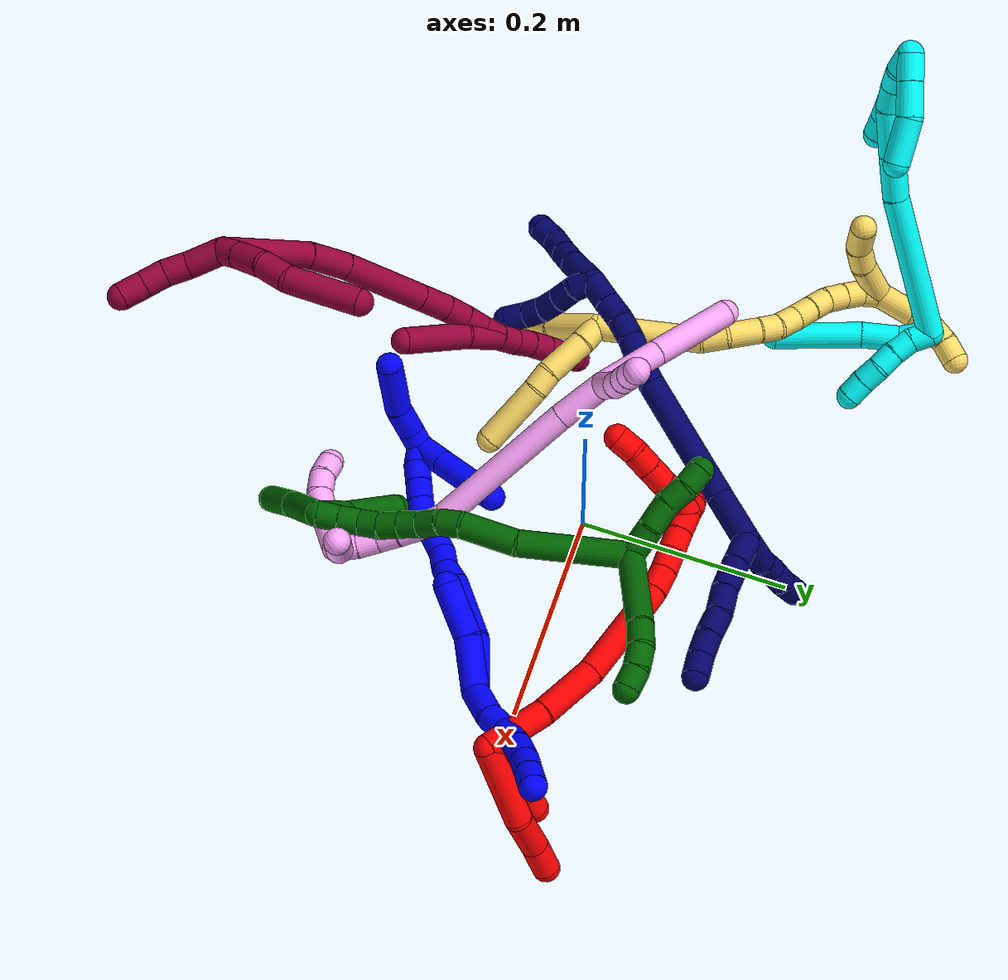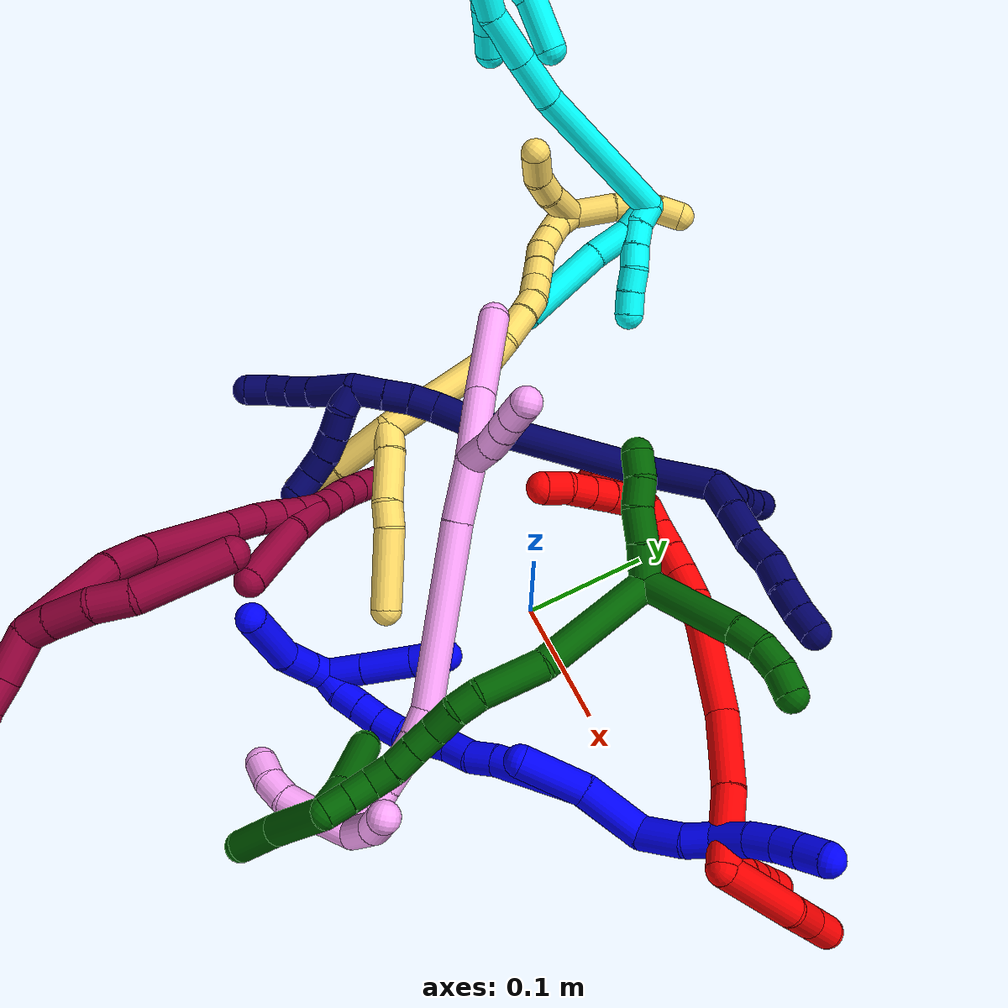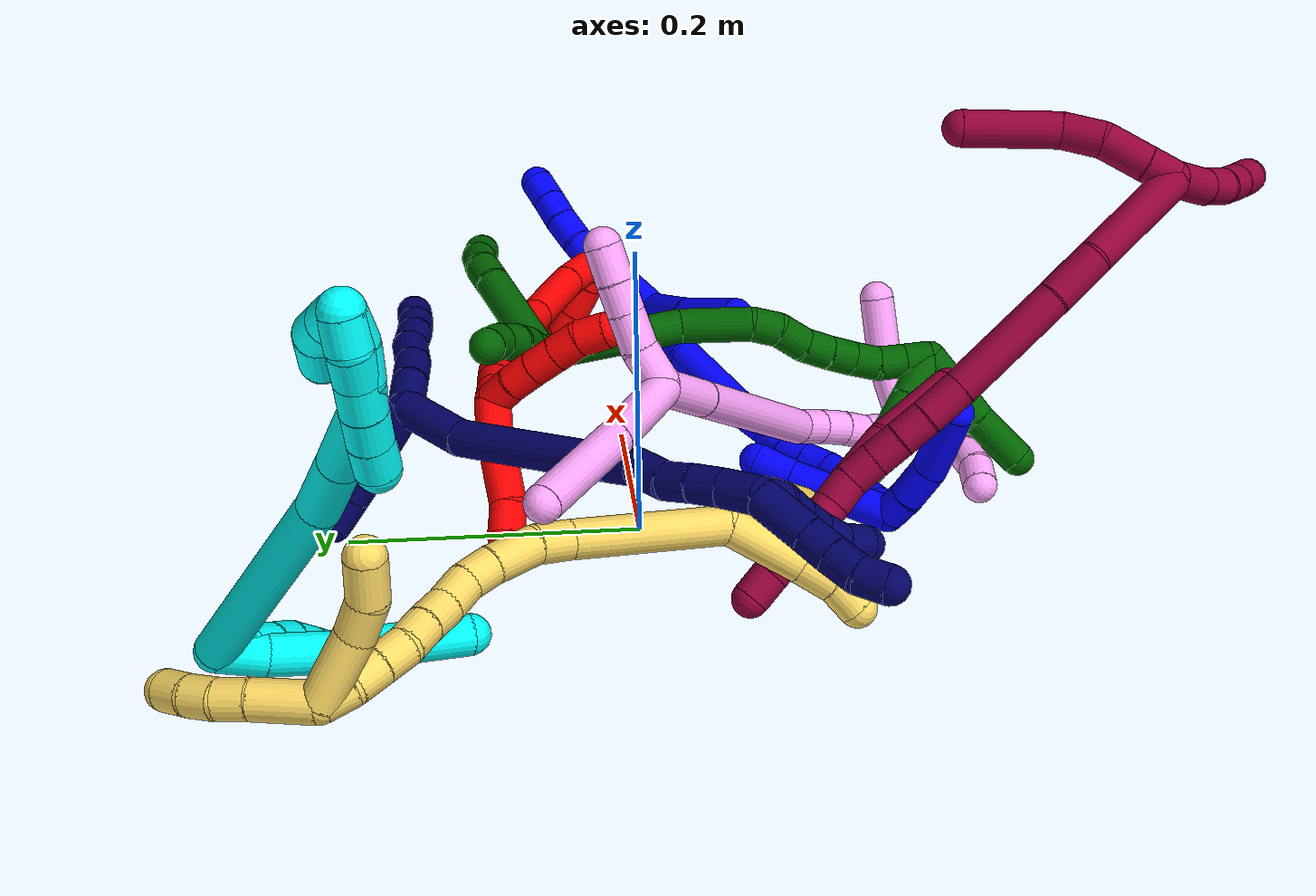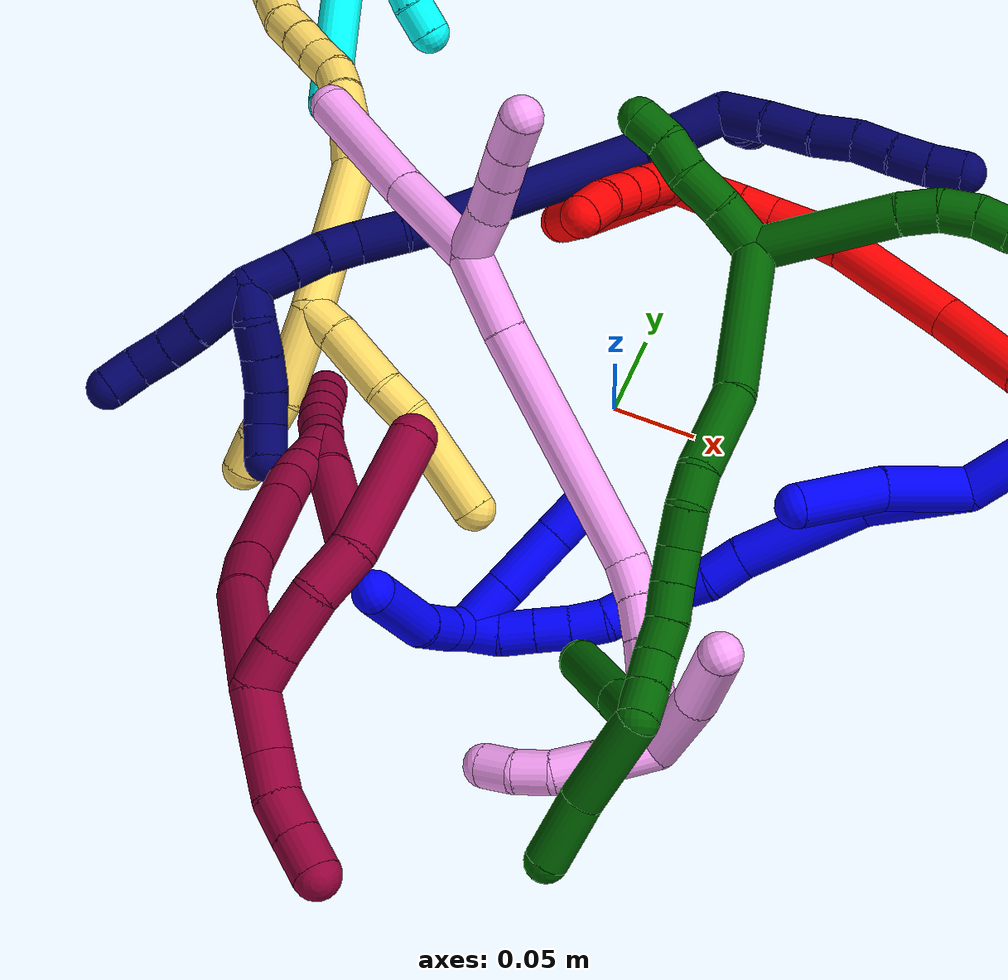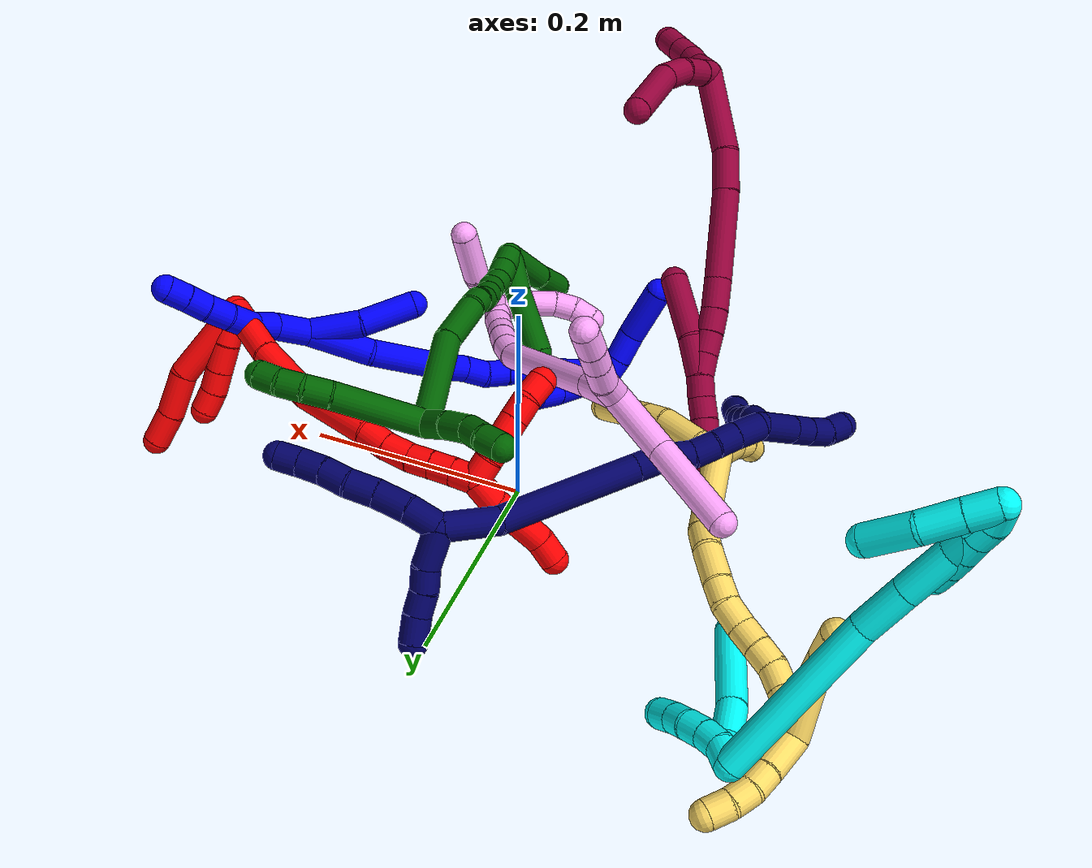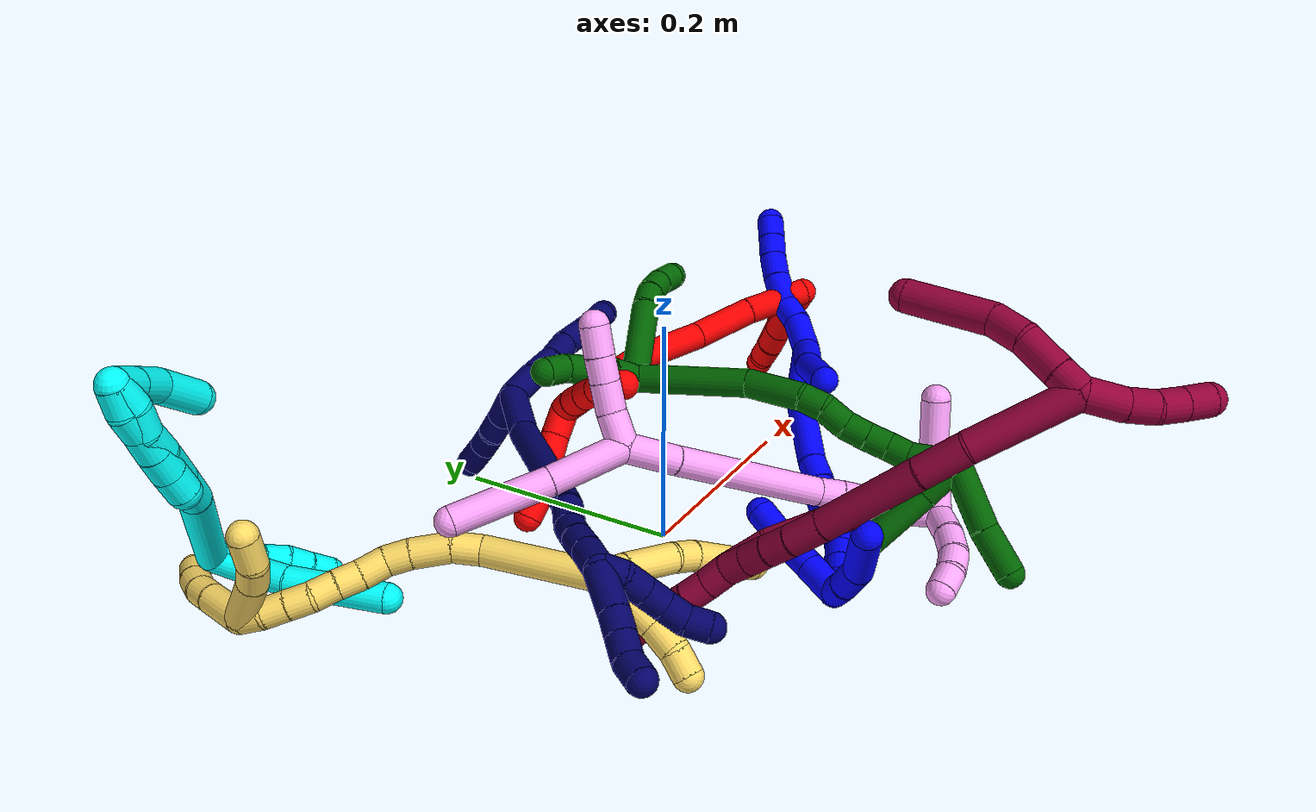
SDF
<sdf version="1.7">
 <world name="default">
  <plugin name="TubeGeneratorPlugin" filename="libtube_generator_plugin.so"/>
  <model name="photoneo_s_sensor">
   <static>1</static>
   <pose>0 0 2 1.57079 1.57079 3.14159</pose>
   <link name="link">
    <inertial><mass>0.1</mass></inertial>
    <sensor name="sensor" type="depth">
     <update_rate>30</update_rate>
     <camera>
      <horizontal_fov>1.22</horizontal_fov>
      <image><width>1920</width><height>1200</height><format>B8G8R8</format></image>
      <clip><near>0.1</near><far>4</far></clip>
      <depth_camera><output>points</output></depth_camera>
     </camera>
     <plugin name="camera_plugin" filename="libgazebo_ros_depth_camera.so">
      <baseline>0.2</baseline>
      <alwaysOn>1</alwaysOn>
      <updateRate>0.0</updateRate>
      <cameraName>camera_ir</cameraName>
      <imageTopicName>/camera/color/image_raw</imageTopicName>
      <cameraInfoTopicName>/camera/color/camera_info</cameraInfoTopicName>
      <depthImageTopicName>/camera/depth/image_raw</depthImageTopicName>
      <depthImageCameraInfoTopicName>/camera/depth/camera_info</depthImageCameraInfoTopicName>
      <pointCloudTopicName>/camera/depth/points</pointCloudTopicName>
      <frameName>fr_optical</frameName>
      <pointCloudCutoff>0.1</pointCloudCutoff>
      <pointCloudCutoffMax>2.0</pointCloudCutoffMax>
      <distortionK1>0</distortionK1>
      <distortionK2>0</distortionK2>
      <distortionK3>0</distortionK3>
      <distortionT1>0</distortionT1>
      <distortionT2>0</distortionT2>
      <CxPrime>0</CxPrime>
      <Cx>0</Cx>
      <Cy>0</Cy>
      <focalLength>0</focalLength>
      <hackBaseline>0</hackBaseline>
     </plugin>
    </sensor>
   </link>
  </model>
  <gravity>0 0 -9.8</gravity>
  <magnetic_field>6e-06 2.3e-05 -4.2e-05</magnetic_field>
  <atmosphere type="adiabatic"/>
  <physics name="default_physics" default="0" type="ode">
   <max_step_size>0.003</max_step_size>
   <real_time_factor>1</real_time_factor>
   <real_time_update_rate>1000</real_time_update_rate>
   <max_contacts>10000</max_contacts>
   <ode>
    <solver>
     <type>quick</type>
     <iters>100</iters>
     <sor>1.3</sor>
     <use_dynamic_moi_rescaling>0</use_dynamic_moi_rescaling>
    </solver>
    <constraints>
     <contact_max_correcting_vel>0</contact_max_correcting_vel>
     <contact_surface_layer>0.001</contact_surface_layer>
     <cfm>0</cfm>
     <erp>0.2</erp>
    </constraints>
   </ode>
  </physics>
  <scene><ambient>0.4 0.4 0.4 1</ambient><background>0.7 0.7 0.7 1</background><shadows>0</shadows></scene>
  <audio><device>default</device></audio>
  <spherical_coordinates>
   <surface_model>EARTH_WGS84</surface_model>
   <latitude_deg>0</latitude_deg>
   <longitude_deg>0</longitude_deg>
   <elevation>0</elevation>
   <heading_deg>0</heading_deg>
  </spherical_coordinates>
  <model name="bin">
   <static>1</static>
   <link name="bottom">
    <collision name="collision-bottom">
     <pose>0 0 -0.01 0 -0 0</pose>
     <geometry><box><size>0.8 0.6 0.02</size></box></geometry>
     <surface>
      <friction><ode><mu>100</mu><mu2>100</mu2></ode></friction>
      <contact><collide_bitmask>65535</collide_bitmask></contact>
     </surface>
    </collision>
   </link>
   <link name="west_wall">
    <collision name="collision-west_wall">
     <pose>-0.41 0 0.1 0 -0 0</pose>
     <geometry><box><size>0.02 0.6 0.2</size></box></geometry>
     <surface>
      <friction><ode><mu>100</mu><mu2>100</mu2></ode></friction>
      <contact><collide_bitmask>65535</collide_bitmask></contact>
     </surface>
    </collision>
   </link>
   <link name="east_wall">
    <collision name="collision-east_wall">
     <pose>0.41 0 0.1 0 -0 0</pose>
     <geometry><box><size>0.02 0.6 0.2</size></box></geometry>
     <surface>
      <friction><ode><mu>100</mu><mu2>100</mu2></ode></friction>
      <contact><collide_bitmask>65535</collide_bitmask></contact>
     </surface>
    </collision>
   </link>
   <link name="south_wall">
    <collision name="collision-south_wall">
     <pose>0 -0.31 0.1 0 -0 0</pose>
     <geometry><box><size>0.8 0.02 0.2</size></box></geometry>
     <surface>
      <friction><ode><mu>100</mu><mu2>100</mu2></ode></friction>
      <contact><collide_bitmask>65535</collide_bitmask></contact>
     </surface>
    </collision>
   </link>
   <link name="north_wall">
    <collision name="collision-north_wall">
     <pose>0 0.31 0.1 0 -0 0</pose>
     <geometry><box><size>0.8 0.02 0.2</size></box></geometry>
     <surface>
      <friction><ode><mu>100</mu><mu2>100</mu2></ode></friction>
      <contact><collide_bitmask>65535</collide_bitmask></contact>
     </surface>
    </collision>
   </link>
  </model>
  <model name="1">
   <static>0</static>
   <link name="1">
    <collision name="collision-cylinder-e_1_2_8">
     <pose>-0.001711 0.001912 0.017318 -0.109934 -0.097911 0.005392</pose>
     <geometry><cylinder><radius>0.0125</radius><length>0.035014</length></cylinder></geometry>
     <surface>
      <friction><ode><mu>1.16</mu><mu2>1.16</mu2><slip1>0</slip1><slip2>0</slip2></ode></friction>
      <contact><ode><kp>1e+06</kp><kd>1</kd><max_vel>0</max_vel><min_depth>0.001</min_depth></ode></contact>
     </surface>
    </collision>
    <visual name="visual-cylinder-e_1_2_8">
     <pose>-0.001711 0.001912 0.017318 -0.109934 -0.097911 0.005392</pose>
     <geometry><cylinder><radius>0.0125</radius><length>0.035014</length></cylinder></geometry>
     <material><ambient>0 0 1 1</ambient></material>
    </visual>
    <collision name="collision-cylinder-e_2_8_9">
     <pose>-0.004555 0.007637 0.04513 -0.348588 -0.101036 0.017805</pose>
     <geometry><cylinder><radius>0.0125</radius><length>0.022445</length></cylinder></geometry>
     <surface>
      <friction><ode><mu>1.16</mu><mu2>1.16</mu2><slip1>0</slip1><slip2>0</slip2></ode></friction>
      <contact><ode><kp>1e+06</kp><kd>1</kd><max_vel>0</max_vel><min_depth>0.001</min_depth></ode></contact>
     </surface>
    </collision>
    <visual name="visual-cylinder-e_2_8_9">
     <pose>-0.004555 0.007637 0.04513 -0.348588 -0.101036 0.017805</pose>
     <geometry><cylinder><radius>0.0125</radius><length>0.022445</length></cylinder></geometry>
     <material><ambient>0 0 1 1</ambient></material>
    </visual>
    <collision name="collision-cylinder-e_3_9_10">
     <pose>-0.010469 0.013508 0.069224 -0.150147 -0.334568 0.0254</pose>
     <geometry><cylinder><radius>0.0125</radius><length>0.029125</length></cylinder></geometry>
     <surface>
      <friction><ode><mu>1.16</mu><mu2>1.16</mu2><slip1>0</slip1><slip2>0</slip2></ode></friction>
      <contact><ode><kp>1e+06</kp><kd>1</kd><max_vel>0</max_vel><min_depth>0.001</min_depth></ode></contact>
     </surface>
    </collision>
    <visual name="visual-cylinder-e_3_9_10">
     <pose>-0.010469 0.013508 0.069224 -0.150147 -0.334568 0.0254</pose>
     <geometry><cylinder><radius>0.0125</radius><length>0.029125</length></cylinder></geometry>
     <material><ambient>0 0 1 1</ambient></material>
    </visual>
    <collision name="collision-cylinder-e_4_10_11">
     <pose>-0.018198 0.015718 0.093903 -0.013741 -0.260056 0.001797</pose>
     <geometry><cylinder><radius>0.0125</radius><length>0.022929</length></cylinder></geometry>
     <surface>
      <friction><ode><mu>1.16</mu><mu2>1.16</mu2><slip1>0</slip1><slip2>0</slip2></ode></friction>
      <contact><ode><kp>1e+06</kp><kd>1</kd><max_vel>0</max_vel><min_depth>0.001</min_depth></ode></contact>
     </surface>
    </collision>
    <visual name="visual-cylinder-e_4_10_11">
     <pose>-0.018198 0.015718 0.093903 -0.013741 -0.260056 0.001797</pose>
     <geometry><cylinder><radius>0.0125</radius><length>0.022929</length></cylinder></geometry>
     <material><ambient>0 0 1 1</ambient></material>
    </visual>
    <collision name="collision-cylinder-e_5_11_12">
     <pose>-0.02385 0.014982 0.114691 0.091251 -0.27054 -0.012428</pose>
     <geometry><cylinder><radius>0.0125</radius><length>0.020237</length></cylinder></geometry>
     <surface>
      <friction><ode><mu>1.16</mu><mu2>1.16</mu2><slip1>0</slip1><slip2>0</slip2></ode></friction>
      <contact><ode><kp>1e+06</kp><kd>1</kd><max_vel>0</max_vel><min_depth>0.001</min_depth></ode></contact>
     </surface>
    </collision>
    <visual name="visual-cylinder-e_5_11_12">
     <pose>-0.02385 0.014982 0.114691 0.091251 -0.27054 -0.012428</pose>
     <geometry><cylinder><radius>0.0125</radius><length>0.020237</length></cylinder></geometry>
     <material><ambient>0 0 1 1</ambient></material>
    </visual>
    <collision name="collision-cylinder-e_6_12_6">
     <pose>-0.028847 0.013249 0.134226 0.08568 -0.228362 -0.009832</pose>
     <geometry><cylinder><radius>0.0125</radius><length>0.020249</length></cylinder></geometry>
     <surface>
      <friction><ode><mu>1.16</mu><mu2>1.16</mu2><slip1>0</slip1><slip2>0</slip2></ode></friction>
      <contact><ode><kp>1e+06</kp><kd>1</kd><max_vel>0</max_vel><min_depth>0.001</min_depth></ode></contact>
     </surface>
    </collision>
    <visual name="visual-cylinder-e_6_12_6">
     <pose>-0.028847 0.013249 0.134226 0.08568 -0.228362 -0.009832</pose>
     <geometry><cylinder><radius>0.0125</radius><length>0.020249</length></cylinder></geometry>
     <material><ambient>0 0 1 1</ambient></material>
    </visual>
    <collision name="collision-cylinder-e_1_2_13">
     <pose>-0.013301 0.002261 -0.020741 -3.03303 -0.567535 2.77319</pose>
     <geometry><cylinder><radius>0.0125</radius><length>0.049486</length></cylinder></geometry>
     <surface>
      <friction><ode><mu>1.16</mu><mu2>1.16</mu2><slip1>0</slip1><slip2>0</slip2></ode></friction>
      <contact><ode><kp>1e+06</kp><kd>1</kd><max_vel>0</max_vel><min_depth>0.001</min_depth></ode></contact>
     </surface>
    </collision>
    <visual name="visual-cylinder-e_1_2_13">
     <pose>-0.013301 0.002261 -0.020741 -3.03303 -0.567535 2.77319</pose>
     <geometry><cylinder><radius>0.0125</radius><length>0.049486</length></cylinder></geometry>
     <material><ambient>0 0 1 1</ambient></material>
    </visual>
    <collision name="collision-cylinder-e_2_13_5">
     <pose>-0.040124 0.000651 -0.062461 2.95913 -0.564968 -2.53092</pose>
     <geometry><cylinder><radius>0.0125</radius><length>0.050514</length></cylinder></geometry>
     <surface>
      <friction><ode><mu>1.16</mu><mu2>1.16</mu2><slip1>0</slip1><slip2>0</slip2></ode></friction>
      <contact><ode><kp>1e+06</kp><kd>1</kd><max_vel>0</max_vel><min_depth>0.001</min_depth></ode></contact>
     </surface>
    </collision>
    <visual name="visual-cylinder-e_2_13_5">
     <pose>-0.040124 0.000651 -0.062461 2.95913 -0.564968 -2.53092</pose>
     <geometry><cylinder><radius>0.0125</radius><length>0.050514</length></cylinder></geometry>
     <material><ambient>0 0 1 1</ambient></material>
    </visual>
    <collision name="collision-cylinder-e_1_2_14">
     <pose>-0.001653 0.007883 -0.028838 -2.87475 -0.055248 0.406069</pose>
     <geometry><cylinder><radius>0.0125</radius><length>0.059884</length></cylinder></geometry>
     <surface>
      <friction><ode><mu>1.16</mu><mu2>1.16</mu2><slip1>0</slip1><slip2>0</slip2></ode></friction>
      <contact><ode><kp>1e+06</kp><kd>1</kd><max_vel>0</max_vel><min_depth>0.001</min_depth></ode></contact>
     </surface>
    </collision>
    <visual name="visual-cylinder-e_1_2_14">
     <pose>-0.001653 0.007883 -0.028838 -2.87475 -0.055248 0.406069</pose>
     <geometry><cylinder><radius>0.0125</radius><length>0.059884</length></cylinder></geometry>
     <material><ambient>0 0 1 1</ambient></material>
    </visual>
    <collision name="collision-cylinder-e_2_14_15">
     <pose>-0.00256 0.015799 -0.09507 -3.14071 0.01998 -3.05334</pose>
     <geometry><cylinder><radius>0.0125</radius><length>0.074803</length></cylinder></geometry>
     <surface>
      <friction><ode><mu>1.16</mu><mu2>1.16</mu2><slip1>0</slip1><slip2>0</slip2></ode></friction>
      <contact><ode><kp>1e+06</kp><kd>1</kd><max_vel>0</max_vel><min_depth>0.001</min_depth></ode></contact>
     </surface>
    </collision>
    <visual name="visual-cylinder-e_2_14_15">
     <pose>-0.00256 0.015799 -0.09507 -3.14071 0.01998 -3.05334</pose>
     <geometry><cylinder><radius>0.0125</radius><length>0.074803</length></cylinder></geometry>
     <material><ambient>0 0 1 1</ambient></material>
    </visual>
    <collision name="collision-cylinder-e_3_15_16">
     <pose>-0.001225 0.013929 -0.143432 2.9698 0.052718 0.594229</pose>
     <geometry><cylinder><radius>0.0125</radius><length>0.022294</length></cylinder></geometry>
     <surface>
      <friction><ode><mu>1.16</mu><mu2>1.16</mu2><slip1>0</slip1><slip2>0</slip2></ode></friction>
      <contact><ode><kp>1e+06</kp><kd>1</kd><max_vel>0</max_vel><min_depth>0.001</min_depth></ode></contact>
     </surface>
    </collision>
    <visual name="visual-cylinder-e_3_15_16">
     <pose>-0.001225 0.013929 -0.143432 2.9698 0.052718 0.594229</pose>
     <geometry><cylinder><radius>0.0125</radius><length>0.022294</length></cylinder></geometry>
     <material><ambient>0 0 1 1</ambient></material>
    </visual>
    <collision name="collision-cylinder-e_4_16_17">
     <pose>-0.00066 0.013392 -0.165379 -3.01784 -0.002 0.032271</pose>
     <geometry><cylinder><radius>0.0125</radius><length>0.022128</length></cylinder></geometry>
     <surface>
      <friction><ode><mu>1.16</mu><mu2>1.16</mu2><slip1>0</slip1><slip2>0</slip2></ode></friction>
      <contact><ode><kp>1e+06</kp><kd>1</kd><max_vel>0</max_vel><min_depth>0.001</min_depth></ode></contact>
     </surface>
    </collision>
    <visual name="visual-cylinder-e_4_16_17">
     <pose>-0.00066 0.013392 -0.165379 -3.01784 -0.002 0.032271</pose>
     <geometry><cylinder><radius>0.0125</radius><length>0.022128</length></cylinder></geometry>
     <material><ambient>0 0 1 1</ambient></material>
    </visual>
    <collision name="collision-cylinder-e_5_17_18">
     <pose>-0.002678 0.013317 -0.186276 2.99733 -0.196585 -1.87685</pose>
     <geometry><cylinder><radius>0.0125</radius><length>0.020437</length></cylinder></geometry>
     <surface>
      <friction><ode><mu>1.16</mu><mu2>1.16</mu2><slip1>0</slip1><slip2>0</slip2></ode></friction>
      <contact><ode><kp>1e+06</kp><kd>1</kd><max_vel>0</max_vel><min_depth>0.001</min_depth></ode></contact>
     </surface>
    </collision>
    <visual name="visual-cylinder-e_5_17_18">
     <pose>-0.002678 0.013317 -0.186276 2.99733 -0.196585 -1.87685</pose>
     <geometry><cylinder><radius>0.0125</radius><length>0.020437</length></cylinder></geometry>
     <material><ambient>0 0 1 1</ambient></material>
    </visual>
    <collision name="collision-cylinder-e_6_18_19">
     <pose>-0.006876 0.009641 -0.205835 2.91381 -0.218973 -1.53102</pose>
     <geometry><cylinder><radius>0.0125</radius><length>0.02028</length></cylinder></geometry>
     <surface>
      <friction><ode><mu>1.16</mu><mu2>1.16</mu2><slip1>0</slip1><slip2>0</slip2></ode></friction>
      <contact><ode><kp>1e+06</kp><kd>1</kd><max_vel>0</max_vel><min_depth>0.001</min_depth></ode></contact>
     </surface>
    </collision>
    <visual name="visual-cylinder-e_6_18_19">
     <pose>-0.006876 0.009641 -0.205835 2.91381 -0.218973 -1.53102</pose>
     <geometry><cylinder><radius>0.0125</radius><length>0.02028</length></cylinder></geometry>
     <material><ambient>0 0 1 1</ambient></material>
    </visual>
    <collision name="collision-cylinder-e_7_19_20">
     <pose>-0.011476 0.008148 -0.225205 -3.06548 -0.240951 2.53215</pose>
     <geometry><cylinder><radius>0.0125</radius><length>0.020091</length></cylinder></geometry>
     <surface>
      <friction><ode><mu>1.16</mu><mu2>1.16</mu2><slip1>0</slip1><slip2>0</slip2></ode></friction>
      <contact><ode><kp>1e+06</kp><kd>1</kd><max_vel>0</max_vel><min_depth>0.001</min_depth></ode></contact>
     </surface>
    </collision>
    <visual name="visual-cylinder-e_7_19_20">
     <pose>-0.011476 0.008148 -0.225205 -3.06548 -0.240951 2.53215</pose>
     <geometry><cylinder><radius>0.0125</radius><length>0.020091</length></cylinder></geometry>
     <material><ambient>0 0 1 1</ambient></material>
    </visual>
    <collision name="collision-cylinder-e_8_20_21">
     <pose>-0.016919 0.01051 -0.244347 -2.97113 -0.308571 2.13689</pose>
     <geometry><cylinder><radius>0.0125</radius><length>0.020055</length></cylinder></geometry>
     <surface>
      <friction><ode><mu>1.16</mu><mu2>1.16</mu2><slip1>0</slip1><slip2>0</slip2></ode></friction>
      <contact><ode><kp>1e+06</kp><kd>1</kd><max_vel>0</max_vel><min_depth>0.001</min_depth></ode></contact>
     </surface>
    </collision>
    <visual name="visual-cylinder-e_8_20_21">
     <pose>-0.016919 0.01051 -0.244347 -2.97113 -0.308571 2.13689</pose>
     <geometry><cylinder><radius>0.0125</radius><length>0.020055</length></cylinder></geometry>
     <material><ambient>0 0 1 1</ambient></material>
    </visual>
    <collision name="collision-cylinder-e_9_21_22">
     <pose>-0.022878 0.013675 -0.263213 -2.97964 -0.295385 2.14288</pose>
     <geometry><cylinder><radius>0.0125</radius><length>0.020018</length></cylinder></geometry>
     <surface>
      <friction><ode><mu>1.16</mu><mu2>1.16</mu2><slip1>0</slip1><slip2>0</slip2></ode></friction>
      <contact><ode><kp>1e+06</kp><kd>1</kd><max_vel>0</max_vel><min_depth>0.001</min_depth></ode></contact>
     </surface>
    </collision>
    <visual name="visual-cylinder-e_9_21_22">
     <pose>-0.022878 0.013675 -0.263213 -2.97964 -0.295385 2.14288</pose>
     <geometry><cylinder><radius>0.0125</radius><length>0.020018</length></cylinder></geometry>
     <material><ambient>0 0 1 1</ambient></material>
    </visual>
    <collision name="collision-cylinder-e_10_22_1">
     <pose>-0.029646 0.018929 -0.281118 -2.72804 -0.395459 1.52485</pose>
     <geometry><cylinder><radius>0.0125</radius><length>0.02001</length></cylinder></geometry>
     <surface>
      <friction><ode><mu>1.16</mu><mu2>1.16</mu2><slip1>0</slip1><slip2>0</slip2></ode></friction>
      <contact><ode><kp>1e+06</kp><kd>1</kd><max_vel>0</max_vel><min_depth>0.001</min_depth></ode></contact>
     </surface>
    </collision>
    <visual name="visual-cylinder-e_10_22_1">
     <pose>-0.029646 0.018929 -0.281118 -2.72804 -0.395459 1.52485</pose>
     <geometry><cylinder><radius>0.0125</radius><length>0.02001</length></cylinder></geometry>
     <material><ambient>0 0 1 1</ambient></material>
    </visual>
    <collision name="collision-cylinder-e_1_1_23">
     <pose>-0.042448 0.019061 -0.292461 2.24982 -1.09606 -1.81292</pose>
     <geometry><cylinder><radius>0.0125</radius><length>0.020122</length></cylinder></geometry>
     <surface>
      <friction><ode><mu>1.16</mu><mu2>1.16</mu2><slip1>0</slip1><slip2>0</slip2></ode></friction>
      <contact><ode><kp>1e+06</kp><kd>1</kd><max_vel>0</max_vel><min_depth>0.001</min_depth></ode></contact>
     </surface>
    </collision>
    <visual name="visual-cylinder-e_1_1_23">
     <pose>-0.042448 0.019061 -0.292461 2.24982 -1.09606 -1.81292</pose>
     <geometry><cylinder><radius>0.0125</radius><length>0.020122</length></cylinder></geometry>
     <material><ambient>0 0 1 1</ambient></material>
    </visual>
    <collision name="collision-cylinder-e_2_23_24">
     <pose>-0.0642 0.010493 -0.297685 2.00867 -1.16445 -1.60535</pose>
     <geometry><cylinder><radius>0.0125</radius><length>0.027877</length></cylinder></geometry>
     <surface>
      <friction><ode><mu>1.16</mu><mu2>1.16</mu2><slip1>0</slip1><slip2>0</slip2></ode></friction>
      <contact><ode><kp>1e+06</kp><kd>1</kd><max_vel>0</max_vel><min_depth>0.001</min_depth></ode></contact>
     </surface>
    </collision>
    <visual name="visual-cylinder-e_2_23_24">
     <pose>-0.0642 0.010493 -0.297685 2.00867 -1.16445 -1.60535</pose>
     <geometry><cylinder><radius>0.0125</radius><length>0.027877</length></cylinder></geometry>
     <material><ambient>0 0 1 1</ambient></material>
    </visual>
    <collision name="collision-cylinder-e_3_24_4">
     <pose>-0.102795 0.002811 -0.301908 2.18226 -1.44402 -2.07448</pose>
     <geometry><cylinder><radius>0.0125</radius><length>0.052001</length></cylinder></geometry>
     <surface>
      <friction><ode><mu>1.16</mu><mu2>1.16</mu2><slip1>0</slip1><slip2>0</slip2></ode></friction>
      <contact><ode><kp>1e+06</kp><kd>1</kd><max_vel>0</max_vel><min_depth>0.001</min_depth></ode></contact>
     </surface>
    </collision>
    <visual name="visual-cylinder-e_3_24_4">
     <pose>-0.102795 0.002811 -0.301908 2.18226 -1.44402 -2.07448</pose>
     <geometry><cylinder><radius>0.0125</radius><length>0.052001</length></cylinder></geometry>
     <material><ambient>0 0 1 1</ambient></material>
    </visual>
    <collision name="collision-cylinder-e_1_1_25">
     <pose>-0.033328 0.030374 -0.275566 -0.504559 0.010727 -0.002765</pose>
     <geometry><cylinder><radius>0.0125</radius><length>0.032002</length></cylinder></geometry>
     <surface>
      <friction><ode><mu>1.16</mu><mu2>1.16</mu2><slip1>0</slip1><slip2>0</slip2></ode></friction>
      <contact><ode><kp>1e+06</kp><kd>1</kd><max_vel>0</max_vel><min_depth>0.001</min_depth></ode></contact>
     </surface>
    </collision>
    <visual name="visual-cylinder-e_1_1_25">
     <pose>-0.033328 0.030374 -0.275566 -0.504559 0.010727 -0.002765</pose>
     <geometry><cylinder><radius>0.0125</radius><length>0.032002</length></cylinder></geometry>
     <material><ambient>0 0 1 1</ambient></material>
    </visual>
    <collision name="collision-cylinder-e_2_25_26">
     <pose>-0.032971 0.048189 -0.243782 -0.515764 0.009088 -0.002397</pose>
     <geometry><cylinder><radius>0.0125</radius><length>0.040875</length></cylinder></geometry>
     <surface>
      <friction><ode><mu>1.16</mu><mu2>1.16</mu2><slip1>0</slip1><slip2>0</slip2></ode></friction>
      <contact><ode><kp>1e+06</kp><kd>1</kd><max_vel>0</max_vel><min_depth>0.001</min_depth></ode></contact>
     </surface>
    </collision>
    <visual name="visual-cylinder-e_2_25_26">
     <pose>-0.032971 0.048189 -0.243782 -0.515764 0.009088 -0.002397</pose>
     <geometry><cylinder><radius>0.0125</radius><length>0.040875</length></cylinder></geometry>
     <material><ambient>0 0 1 1</ambient></material>
    </visual>
    <collision name="collision-cylinder-e_3_26_3">
     <pose>-0.033591 0.064257 -0.213863 -0.458253 -0.059478 0.013875</pose>
     <geometry><cylinder><radius>0.0125</radius><length>0.027123</length></cylinder></geometry>
     <surface>
      <friction><ode><mu>1.16</mu><mu2>1.16</mu2><slip1>0</slip1><slip2>0</slip2></ode></friction>
      <contact><ode><kp>1e+06</kp><kd>1</kd><max_vel>0</max_vel><min_depth>0.001</min_depth></ode></contact>
     </surface>
    </collision>
    <visual name="visual-cylinder-e_3_26_3">
     <pose>-0.033591 0.064257 -0.213863 -0.458253 -0.059478 0.013875</pose>
     <geometry><cylinder><radius>0.0125</radius><length>0.027123</length></cylinder></geometry>
     <material><ambient>0 0 1 1</ambient></material>
    </visual>
    <collision name="collision-sphere-3">
     <pose>-0.034397 0.070246 -0.201722 0 -0 0</pose>
     <geometry><sphere><radius>0.0125</radius></sphere></geometry>
     <surface>
      <friction><ode><mu>1.16</mu><mu2>1.16</mu2><slip1>0</slip1><slip2>0</slip2></ode></friction>
      <contact><ode><kp>1e+06</kp><kd>1</kd><max_vel>0</max_vel><min_depth>0.001</min_depth></ode></contact>
     </surface>
    </collision>
    <visual name="visual-sphere-3">
     <pose>-0.034397 0.070246 -0.201722 0 -0 0</pose>
     <geometry><sphere><radius>0.0125</radius></sphere></geometry>
     <material><ambient>0 0 1 1</ambient></material>
    </visual>
    <collision name="collision-sphere-26">
     <pose>-0.032785 0.058268 -0.226003 0 -0 0</pose>
     <geometry><sphere><radius>0.0125</radius></sphere></geometry>
     <surface>
      <friction><ode><mu>1.16</mu><mu2>1.16</mu2><slip1>0</slip1><slip2>0</slip2></ode></friction>
      <contact><ode><kp>1e+06</kp><kd>1</kd><max_vel>0</max_vel><min_depth>0.001</min_depth></ode></contact>
     </surface>
    </collision>
    <visual name="visual-sphere-26">
     <pose>-0.032785 0.058268 -0.226003 0 -0 0</pose>
     <geometry><sphere><radius>0.0125</radius></sphere></geometry>
     <material><ambient>0 0 1 1</ambient></material>
    </visual>
    <collision name="collision-sphere-25">
     <pose>-0.033157 0.038109 -0.26156 0 -0 0</pose>
     <geometry><sphere><radius>0.0125</radius></sphere></geometry>
     <surface>
      <friction><ode><mu>1.16</mu><mu2>1.16</mu2><slip1>0</slip1><slip2>0</slip2></ode></friction>
      <contact><ode><kp>1e+06</kp><kd>1</kd><max_vel>0</max_vel><min_depth>0.001</min_depth></ode></contact>
     </surface>
    </collision>
    <visual name="visual-sphere-25">
     <pose>-0.033157 0.038109 -0.26156 0 -0 0</pose>
     <geometry><sphere><radius>0.0125</radius></sphere></geometry>
     <material><ambient>0 0 1 1</ambient></material>
    </visual>
    <collision name="collision-sphere-4">
     <pose>-0.128587 0.00012 -0.303795 0 -0 0</pose>
     <geometry><sphere><radius>0.0125</radius></sphere></geometry>
     <surface>
      <friction><ode><mu>1.16</mu><mu2>1.16</mu2><slip1>0</slip1><slip2>0</slip2></ode></friction>
      <contact><ode><kp>1e+06</kp><kd>1</kd><max_vel>0</max_vel><min_depth>0.001</min_depth></ode></contact>
     </surface>
    </collision>
    <visual name="visual-sphere-4">
     <pose>-0.128587 0.00012 -0.303795 0 -0 0</pose>
     <geometry><sphere><radius>0.0125</radius></sphere></geometry>
     <material><ambient>0 0 1 1</ambient></material>
    </visual>
    <collision name="collision-sphere-24">
     <pose>-0.077003 0.005503 -0.300021 0 -0 0</pose>
     <geometry><sphere><radius>0.0125</radius></sphere></geometry>
     <surface>
      <friction><ode><mu>1.16</mu><mu2>1.16</mu2><slip1>0</slip1><slip2>0</slip2></ode></friction>
      <contact><ode><kp>1e+06</kp><kd>1</kd><max_vel>0</max_vel><min_depth>0.001</min_depth></ode></contact>
     </surface>
    </collision>
    <visual name="visual-sphere-24">
     <pose>-0.077003 0.005503 -0.300021 0 -0 0</pose>
     <geometry><sphere><radius>0.0125</radius></sphere></geometry>
     <material><ambient>0 0 1 1</ambient></material>
    </visual>
    <collision name="collision-sphere-23">
     <pose>-0.051397 0.015482 -0.295349 0 -0 0</pose>
     <geometry><sphere><radius>0.0125</radius></sphere></geometry>
     <surface>
      <friction><ode><mu>1.16</mu><mu2>1.16</mu2><slip1>0</slip1><slip2>0</slip2></ode></friction>
      <contact><ode><kp>1e+06</kp><kd>1</kd><max_vel>0</max_vel><min_depth>0.001</min_depth></ode></contact>
     </surface>
    </collision>
    <visual name="visual-sphere-23">
     <pose>-0.051397 0.015482 -0.295349 0 -0 0</pose>
     <geometry><sphere><radius>0.0125</radius></sphere></geometry>
     <material><ambient>0 0 1 1</ambient></material>
    </visual>
    <collision name="collision-sphere-1">
     <pose>-0.0335 0.02264 -0.289573 0 -0 0</pose>
     <geometry><sphere><radius>0.0125</radius></sphere></geometry>
     <surface>
      <friction><ode><mu>1.16</mu><mu2>1.16</mu2><slip1>0</slip1><slip2>0</slip2></ode></friction>
      <contact><ode><kp>1e+06</kp><kd>1</kd><max_vel>0</max_vel><min_depth>0.001</min_depth></ode></contact>
     </surface>
    </collision>
    <visual name="visual-sphere-1">
     <pose>-0.0335 0.02264 -0.289573 0 -0 0</pose>
     <geometry><sphere><radius>0.0125</radius></sphere></geometry>
     <material><ambient>0 0 1 1</ambient></material>
    </visual>
    <collision name="collision-sphere-22">
     <pose>-0.025791 0.015219 -0.272663 0 -0 0</pose>
     <geometry><sphere><radius>0.0125</radius></sphere></geometry>
     <surface>
      <friction><ode><mu>1.16</mu><mu2>1.16</mu2><slip1>0</slip1><slip2>0</slip2></ode></friction>
      <contact><ode><kp>1e+06</kp><kd>1</kd><max_vel>0</max_vel><min_depth>0.001</min_depth></ode></contact>
     </surface>
    </collision>
    <visual name="visual-sphere-22">
     <pose>-0.025791 0.015219 -0.272663 0 -0 0</pose>
     <geometry><sphere><radius>0.0125</radius></sphere></geometry>
     <material><ambient>0 0 1 1</ambient></material>
    </visual>
    <collision name="collision-sphere-21">
     <pose>-0.019964 0.012131 -0.253763 0 -0 0</pose>
     <geometry><sphere><radius>0.0125</radius></sphere></geometry>
     <surface>
      <friction><ode><mu>1.16</mu><mu2>1.16</mu2><slip1>0</slip1><slip2>0</slip2></ode></friction>
      <contact><ode><kp>1e+06</kp><kd>1</kd><max_vel>0</max_vel><min_depth>0.001</min_depth></ode></contact>
     </surface>
    </collision>
    <visual name="visual-sphere-21">
     <pose>-0.019964 0.012131 -0.253763 0 -0 0</pose>
     <geometry><sphere><radius>0.0125</radius></sphere></geometry>
     <material><ambient>0 0 1 1</ambient></material>
    </visual>
    <collision name="collision-sphere-12">
     <pose>-0.026555 0.014093 0.1244 0 -0 0</pose>
     <geometry><sphere><radius>0.0125</radius></sphere></geometry>
     <surface>
      <friction><ode><mu>1.16</mu><mu2>1.16</mu2><slip1>0</slip1><slip2>0</slip2></ode></friction>
      <contact><ode><kp>1e+06</kp><kd>1</kd><max_vel>0</max_vel><min_depth>0.001</min_depth></ode></contact>
     </surface>
    </collision>
    <visual name="visual-sphere-12">
     <pose>-0.026555 0.014093 0.1244 0 -0 0</pose>
     <geometry><sphere><radius>0.0125</radius></sphere></geometry>
     <material><ambient>0 0 1 1</ambient></material>
    </visual>
    <collision name="collision-sphere-11">
     <pose>-0.021146 0.01587 0.104981 0 -0 0</pose>
     <geometry><sphere><radius>0.0125</radius></sphere></geometry>
     <surface>
      <friction><ode><mu>1.16</mu><mu2>1.16</mu2><slip1>0</slip1><slip2>0</slip2></ode></friction>
      <contact><ode><kp>1e+06</kp><kd>1</kd><max_vel>0</max_vel><min_depth>0.001</min_depth></ode></contact>
     </surface>
    </collision>
    <visual name="visual-sphere-11">
     <pose>-0.021146 0.01587 0.104981 0 -0 0</pose>
     <geometry><sphere><radius>0.0125</radius></sphere></geometry>
     <material><ambient>0 0 1 1</ambient></material>
    </visual>
    <collision name="collision-sphere-10">
     <pose>-0.01525 0.015566 0.082825 0 -0 0</pose>
     <geometry><sphere><radius>0.0125</radius></sphere></geometry>
     <surface>
      <friction><ode><mu>1.16</mu><mu2>1.16</mu2><slip1>0</slip1><slip2>0</slip2></ode></friction>
      <contact><ode><kp>1e+06</kp><kd>1</kd><max_vel>0</max_vel><min_depth>0.001</min_depth></ode></contact>
     </surface>
    </collision>
    <visual name="visual-sphere-10">
     <pose>-0.01525 0.015566 0.082825 0 -0 0</pose>
     <geometry><sphere><radius>0.0125</radius></sphere></geometry>
     <material><ambient>0 0 1 1</ambient></material>
    </visual>
    <collision name="collision-sphere-9">
     <pose>-0.005687 0.011451 0.055624 0 -0 0</pose>
     <geometry><sphere><radius>0.0125</radius></sphere></geometry>
     <surface>
      <friction><ode><mu>1.16</mu><mu2>1.16</mu2><slip1>0</slip1><slip2>0</slip2></ode></friction>
      <contact><ode><kp>1e+06</kp><kd>1</kd><max_vel>0</max_vel><min_depth>0.001</min_depth></ode></contact>
     </surface>
    </collision>
    <visual name="visual-sphere-9">
     <pose>-0.005687 0.011451 0.055624 0 -0 0</pose>
     <geometry><sphere><radius>0.0125</radius></sphere></geometry>
     <material><ambient>0 0 1 1</ambient></material>
    </visual>
    <collision name="collision-sphere-2">
     <geometry><sphere><radius>0.0125</radius></sphere></geometry>
     <surface>
      <friction><ode><mu>1.16</mu><mu2>1.16</mu2><slip1>0</slip1><slip2>0</slip2></ode></friction>
      <contact><ode><kp>1e+06</kp><kd>1</kd><max_vel>0</max_vel><min_depth>0.001</min_depth></ode></contact>
     </surface>
    </collision>
    <visual name="visual-sphere-2">
     <geometry><sphere><radius>0.0125</radius></sphere></geometry>
     <material><ambient>0 0 1 1</ambient></material>
    </visual>
    <collision name="collision-sphere-19">
     <pose>-0.009079 0.007406 -0.215477 0 -0 0</pose>
     <geometry><sphere><radius>0.0125</radius></sphere></geometry>
     <surface>
      <friction><ode><mu>1.16</mu><mu2>1.16</mu2><slip1>0</slip1><slip2>0</slip2></ode></friction>
      <contact><ode><kp>1e+06</kp><kd>1</kd><max_vel>0</max_vel><min_depth>0.001</min_depth></ode></contact>
     </surface>
    </collision>
    <visual name="visual-sphere-19">
     <pose>-0.009079 0.007406 -0.215477 0 -0 0</pose>
     <geometry><sphere><radius>0.0125</radius></sphere></geometry>
     <material><ambient>0 0 1 1</ambient></material>
    </visual>
    <collision name="collision-sphere-8">
     <pose>-0.003423 0.003823 0.034636 0 -0 0</pose>
     <geometry><sphere><radius>0.0125</radius></sphere></geometry>
     <surface>
      <friction><ode><mu>1.16</mu><mu2>1.16</mu2><slip1>0</slip1><slip2>0</slip2></ode></friction>
      <contact><ode><kp>1e+06</kp><kd>1</kd><max_vel>0</max_vel><min_depth>0.001</min_depth></ode></contact>
     </surface>
    </collision>
    <visual name="visual-sphere-8">
     <pose>-0.003423 0.003823 0.034636 0 -0 0</pose>
     <geometry><sphere><radius>0.0125</radius></sphere></geometry>
     <material><ambient>0 0 1 1</ambient></material>
    </visual>
    <collision name="collision-sphere-6">
     <pose>-0.031139 0.012405 0.144052 0 -0 0</pose>
     <geometry><sphere><radius>0.0125</radius></sphere></geometry>
     <surface>
      <friction><ode><mu>1.16</mu><mu2>1.16</mu2><slip1>0</slip1><slip2>0</slip2></ode></friction>
      <contact><ode><kp>1e+06</kp><kd>1</kd><max_vel>0</max_vel><min_depth>0.001</min_depth></ode></contact>
     </surface>
    </collision>
    <visual name="visual-sphere-6">
     <pose>-0.031139 0.012405 0.144052 0 -0 0</pose>
     <geometry><sphere><radius>0.0125</radius></sphere></geometry>
     <material><ambient>0 0 1 1</ambient></material>
    </visual>
    <collision name="collision-sphere-13">
     <pose>-0.026602 0.004521 -0.041483 0 -0 0</pose>
     <geometry><sphere><radius>0.0125</radius></sphere></geometry>
     <surface>
      <friction><ode><mu>1.16</mu><mu2>1.16</mu2><slip1>0</slip1><slip2>0</slip2></ode></friction>
      <contact><ode><kp>1e+06</kp><kd>1</kd><max_vel>0</max_vel><min_depth>0.001</min_depth></ode></contact>
     </surface>
    </collision>
    <visual name="visual-sphere-13">
     <pose>-0.026602 0.004521 -0.041483 0 -0 0</pose>
     <geometry><sphere><radius>0.0125</radius></sphere></geometry>
     <material><ambient>0 0 1 1</ambient></material>
    </visual>
    <collision name="collision-sphere-5">
     <pose>-0.053646 -0.00322 -0.083439 0 -0 0</pose>
     <geometry><sphere><radius>0.0125</radius></sphere></geometry>
     <surface>
      <friction><ode><mu>1.16</mu><mu2>1.16</mu2><slip1>0</slip1><slip2>0</slip2></ode></friction>
      <contact><ode><kp>1e+06</kp><kd>1</kd><max_vel>0</max_vel><min_depth>0.001</min_depth></ode></contact>
     </surface>
    </collision>
    <visual name="visual-sphere-5">
     <pose>-0.053646 -0.00322 -0.083439 0 -0 0</pose>
     <geometry><sphere><radius>0.0125</radius></sphere></geometry>
     <material><ambient>0 0 1 1</ambient></material>
    </visual>
    <collision name="collision-sphere-14">
     <pose>-0.003307 0.015766 -0.057676 0 -0 0</pose>
     <geometry><sphere><radius>0.0125</radius></sphere></geometry>
     <surface>
      <friction><ode><mu>1.16</mu><mu2>1.16</mu2><slip1>0</slip1><slip2>0</slip2></ode></friction>
      <contact><ode><kp>1e+06</kp><kd>1</kd><max_vel>0</max_vel><min_depth>0.001</min_depth></ode></contact>
     </surface>
    </collision>
    <visual name="visual-sphere-14">
     <pose>-0.003307 0.015766 -0.057676 0 -0 0</pose>
     <geometry><sphere><radius>0.0125</radius></sphere></geometry>
     <material><ambient>0 0 1 1</ambient></material>
    </visual>
    <collision name="collision-sphere-15">
     <pose>-0.001812 0.015832 -0.132464 0 -0 0</pose>
     <geometry><sphere><radius>0.0125</radius></sphere></geometry>
     <surface>
      <friction><ode><mu>1.16</mu><mu2>1.16</mu2><slip1>0</slip1><slip2>0</slip2></ode></friction>
      <contact><ode><kp>1e+06</kp><kd>1</kd><max_vel>0</max_vel><min_depth>0.001</min_depth></ode></contact>
     </surface>
    </collision>
    <visual name="visual-sphere-15">
     <pose>-0.001812 0.015832 -0.132464 0 -0 0</pose>
     <geometry><sphere><radius>0.0125</radius></sphere></geometry>
     <material><ambient>0 0 1 1</ambient></material>
    </visual>
    <collision name="collision-sphere-16">
     <pose>-0.000638 0.012026 -0.154399 0 -0 0</pose>
     <geometry><sphere><radius>0.0125</radius></sphere></geometry>
     <surface>
      <friction><ode><mu>1.16</mu><mu2>1.16</mu2><slip1>0</slip1><slip2>0</slip2></ode></friction>
      <contact><ode><kp>1e+06</kp><kd>1</kd><max_vel>0</max_vel><min_depth>0.001</min_depth></ode></contact>
     </surface>
    </collision>
    <visual name="visual-sphere-16">
     <pose>-0.000638 0.012026 -0.154399 0 -0 0</pose>
     <geometry><sphere><radius>0.0125</radius></sphere></geometry>
     <material><ambient>0 0 1 1</ambient></material>
    </visual>
    <collision name="collision-sphere-17">
     <pose>-0.000682 0.014758 -0.176358 0 -0 0</pose>
     <geometry><sphere><radius>0.0125</radius></sphere></geometry>
     <surface>
      <friction><ode><mu>1.16</mu><mu2>1.16</mu2><slip1>0</slip1><slip2>0</slip2></ode></friction>
      <contact><ode><kp>1e+06</kp><kd>1</kd><max_vel>0</max_vel><min_depth>0.001</min_depth></ode></contact>
     </surface>
    </collision>
    <visual name="visual-sphere-17">
     <pose>-0.000682 0.014758 -0.176358 0 -0 0</pose>
     <geometry><sphere><radius>0.0125</radius></sphere></geometry>
     <material><ambient>0 0 1 1</ambient></material>
    </visual>
    <collision name="collision-sphere-18">
     <pose>-0.004674 0.011876 -0.196193 0 -0 0</pose>
     <geometry><sphere><radius>0.0125</radius></sphere></geometry>
     <surface>
      <friction><ode><mu>1.16</mu><mu2>1.16</mu2><slip1>0</slip1><slip2>0</slip2></ode></friction>
      <contact><ode><kp>1e+06</kp><kd>1</kd><max_vel>0</max_vel><min_depth>0.001</min_depth></ode></contact>
     </surface>
    </collision>
    <visual name="visual-sphere-18">
     <pose>-0.004674 0.011876 -0.196193 0 -0 0</pose>
     <geometry><sphere><radius>0.0125</radius></sphere></geometry>
     <material><ambient>0 0 1 1</ambient></material>
    </visual>
    <collision name="collision-sphere-20">
     <pose>-0.013873 0.00889 -0.234932 0 -0 0</pose>
     <geometry><sphere><radius>0.0125</radius></sphere></geometry>
     <surface>
      <friction><ode><mu>1.16</mu><mu2>1.16</mu2><slip1>0</slip1><slip2>0</slip2></ode></friction>
      <contact><ode><kp>1e+06</kp><kd>1</kd><max_vel>0</max_vel><min_depth>0.001</min_depth></ode></contact>
     </surface>
    </collision>
    <visual name="visual-sphere-20">
     <pose>-0.013873 0.00889 -0.234932 0 -0 0</pose>
     <geometry><sphere><radius>0.0125</radius></sphere></geometry>
     <material><ambient>0 0 1 1</ambient></material>
    </visual>
    <inertial>
     <pose>-0.024131 0.014628 -0.122423 0 -0 0</pose>
     <mass>0.75</mass>
     <inertia><ixx>-2.5e-05</ixx><ixy>0</ixy><ixz>0</ixz><iyy>9.3e-05</iyy><iyz>0</iyz><izz>1.4e-05</izz></inertia>
    </inertial>
   </link>
   <pose>0.219171 -0.028054 0.096074 -0.288606 1.15317 0.321421</pose>
  </model>
  <model name="2">
   <static>0</static>
   <link name="2">
    <collision name="collision-cylinder-e_1_2_8">
     <pose>0.008075 0.010113 -0.036904 -2.87412 0.207986 -1.31955</pose>
     <geometry><cylinder><radius>0.0125</radius><length>0.078216</length></cylinder></geometry>
     <surface>
      <friction><ode><mu>1.16</mu><mu2>1.16</mu2><slip1>0</slip1><slip2>0</slip2></ode></friction>
      <contact><ode><kp>1e+06</kp><kd>1</kd><max_vel>0</max_vel><min_depth>0.001</min_depth></ode></contact>
     </surface>
    </collision>
    <visual name="visual-cylinder-e_1_2_8">
     <pose>0.008075 0.010113 -0.036904 -2.87412 0.207986 -1.31955</pose>
     <geometry><cylinder><radius>0.0125</radius><length>0.078216</length></cylinder></geometry>
     <material><ambient>1 0 0 1</ambient></material>
    </visual>
    <collision name="collision-cylinder-e_2_8_9">
     <pose>0.018265 0.018906 -0.094269 3.07714 0.102737 2.02148</pose>
     <geometry><cylinder><radius>0.0125</radius><length>0.041222</length></cylinder></geometry>
     <surface>
      <friction><ode><mu>1.16</mu><mu2>1.16</mu2><slip1>0</slip1><slip2>0</slip2></ode></friction>
      <contact><ode><kp>1e+06</kp><kd>1</kd><max_vel>0</max_vel><min_depth>0.001</min_depth></ode></contact>
     </surface>
    </collision>
    <visual name="visual-cylinder-e_2_8_9">
     <pose>0.018265 0.018906 -0.094269 3.07714 0.102737 2.02148</pose>
     <geometry><cylinder><radius>0.0125</radius><length>0.041222</length></cylinder></geometry>
     <material><ambient>1 0 0 1</ambient></material>
    </visual>
    <collision name="collision-cylinder-e_3_9_6">
     <pose>0.02263 0.01883 -0.129791 -3.05914 0.147914 -2.12557</pose>
     <geometry><cylinder><radius>0.0125</radius><length>0.030562</length></cylinder></geometry>
     <surface>
      <friction><ode><mu>1.16</mu><mu2>1.16</mu2><slip1>0</slip1><slip2>0</slip2></ode></friction>
      <contact><ode><kp>1e+06</kp><kd>1</kd><max_vel>0</max_vel><min_depth>0.001</min_depth></ode></contact>
     </surface>
    </collision>
    <visual name="visual-cylinder-e_3_9_6">
     <pose>0.02263 0.01883 -0.129791 -3.05914 0.147914 -2.12557</pose>
     <geometry><cylinder><radius>0.0125</radius><length>0.030562</length></cylinder></geometry>
     <material><ambient>1 0 0 1</ambient></material>
    </visual>
    <collision name="collision-cylinder-e_1_2_10">
     <pose>-0.000705 -0.00081 -0.016174 3.09157 -0.043484 -1.43119</pose>
     <geometry><cylinder><radius>0.0125</radius><length>0.032419</length></cylinder></geometry>
     <surface>
      <friction><ode><mu>1.16</mu><mu2>1.16</mu2><slip1>0</slip1><slip2>0</slip2></ode></friction>
      <contact><ode><kp>1e+06</kp><kd>1</kd><max_vel>0</max_vel><min_depth>0.001</min_depth></ode></contact>
     </surface>
    </collision>
    <visual name="visual-cylinder-e_1_2_10">
     <pose>-0.000705 -0.00081 -0.016174 3.09157 -0.043484 -1.43119</pose>
     <geometry><cylinder><radius>0.0125</radius><length>0.032419</length></cylinder></geometry>
     <material><ambient>1 0 0 1</ambient></material>
    </visual>
    <collision name="collision-cylinder-e_2_10_11">
     <pose>-0.000852 -0.002809 -0.045315 3.0501 0.042779 0.874343</pose>
     <geometry><cylinder><radius>0.0125</radius><length>0.026066</length></cylinder></geometry>
     <surface>
      <friction><ode><mu>1.16</mu><mu2>1.16</mu2><slip1>0</slip1><slip2>0</slip2></ode></friction>
      <contact><ode><kp>1e+06</kp><kd>1</kd><max_vel>0</max_vel><min_depth>0.001</min_depth></ode></contact>
     </surface>
    </collision>
    <visual name="visual-cylinder-e_2_10_11">
     <pose>-0.000852 -0.002809 -0.045315 3.0501 0.042779 0.874343</pose>
     <geometry><cylinder><radius>0.0125</radius><length>0.026066</length></cylinder></geometry>
     <material><ambient>1 0 0 1</ambient></material>
    </visual>
    <collision name="collision-cylinder-e_3_11_12">
     <pose>0.000163 -0.005053 -0.06863 3.04001 0.043973 0.816575</pose>
     <geometry><cylinder><radius>0.0125</radius><length>0.020825</length></cylinder></geometry>
     <surface>
      <friction><ode><mu>1.16</mu><mu2>1.16</mu2><slip1>0</slip1><slip2>0</slip2></ode></friction>
      <contact><ode><kp>1e+06</kp><kd>1</kd><max_vel>0</max_vel><min_depth>0.001</min_depth></ode></contact>
     </surface>
    </collision>
    <visual name="visual-cylinder-e_3_11_12">
     <pose>0.000163 -0.005053 -0.06863 3.04001 0.043973 0.816575</pose>
     <geometry><cylinder><radius>0.0125</radius><length>0.020825</length></cylinder></geometry>
     <material><ambient>1 0 0 1</ambient></material>
    </visual>
    <collision name="collision-cylinder-e_4_12_5">
     <pose>0.001464 -0.005422 -0.089267 -3.075 0.08163 -1.77313</pose>
     <geometry><cylinder><radius>0.0125</radius><length>0.02069</length></cylinder></geometry>
     <surface>
      <friction><ode><mu>1.16</mu><mu2>1.16</mu2><slip1>0</slip1><slip2>0</slip2></ode></friction>
      <contact><ode><kp>1e+06</kp><kd>1</kd><max_vel>0</max_vel><min_depth>0.001</min_depth></ode></contact>
     </surface>
    </collision>
    <visual name="visual-cylinder-e_4_12_5">
     <pose>0.001464 -0.005422 -0.089267 -3.075 0.08163 -1.77313</pose>
     <geometry><cylinder><radius>0.0125</radius><length>0.02069</length></cylinder></geometry>
     <material><ambient>1 0 0 1</ambient></material>
    </visual>
    <collision name="collision-cylinder-e_1_2_13">
     <pose>-0.027632 -0.007959 -0.008873 2.41046 -1.16353 -2.08745</pose>
     <geometry><cylinder><radius>0.0125</radius><length>0.060187</length></cylinder></geometry>
     <surface>
      <friction><ode><mu>1.16</mu><mu2>1.16</mu2><slip1>0</slip1><slip2>0</slip2></ode></friction>
      <contact><ode><kp>1e+06</kp><kd>1</kd><max_vel>0</max_vel><min_depth>0.001</min_depth></ode></contact>
     </surface>
    </collision>
    <visual name="visual-cylinder-e_1_2_13">
     <pose>-0.027632 -0.007959 -0.008873 2.41046 -1.16353 -2.08745</pose>
     <geometry><cylinder><radius>0.0125</radius><length>0.060187</length></cylinder></geometry>
     <material><ambient>1 0 0 1</ambient></material>
    </visual>
    <collision name="collision-cylinder-e_2_13_14">
     <pose>-0.08173 -0.027785 -0.024905 2.1136 -1.08841 -1.64009</pose>
     <geometry><cylinder><radius>0.0125</radius><length>0.05975</length></cylinder></geometry>
     <surface>
      <friction><ode><mu>1.16</mu><mu2>1.16</mu2><slip1>0</slip1><slip2>0</slip2></ode></friction>
      <contact><ode><kp>1e+06</kp><kd>1</kd><max_vel>0</max_vel><min_depth>0.001</min_depth></ode></contact>
     </surface>
    </collision>
    <visual name="visual-cylinder-e_2_13_14">
     <pose>-0.08173 -0.027785 -0.024905 2.1136 -1.08841 -1.64009</pose>
     <geometry><cylinder><radius>0.0125</radius><length>0.05975</length></cylinder></geometry>
     <material><ambient>1 0 0 1</ambient></material>
    </visual>
    <collision name="collision-cylinder-e_3_14_15">
     <pose>-0.140821 -0.055223 -0.03238 1.59106 -1.1254 -1.14376</pose>
     <geometry><cylinder><radius>0.0125</radius><length>0.072303</length></cylinder></geometry>
     <surface>
      <friction><ode><mu>1.16</mu><mu2>1.16</mu2><slip1>0</slip1><slip2>0</slip2></ode></friction>
      <contact><ode><kp>1e+06</kp><kd>1</kd><max_vel>0</max_vel><min_depth>0.001</min_depth></ode></contact>
     </surface>
    </collision>
    <visual name="visual-cylinder-e_3_14_15">
     <pose>-0.140821 -0.055223 -0.03238 1.59106 -1.1254 -1.14376</pose>
     <geometry><cylinder><radius>0.0125</radius><length>0.072303</length></cylinder></geometry>
     <material><ambient>1 0 0 1</ambient></material>
    </visual>
    <collision name="collision-cylinder-e_4_15_16">
     <pose>-0.182998 -0.077254 -0.034239 1.80538 -0.963249 -1.16996</pose>
     <geometry><cylinder><radius>0.0125</radius><length>0.023267</length></cylinder></geometry>
     <surface>
      <friction><ode><mu>1.16</mu><mu2>1.16</mu2><slip1>0</slip1><slip2>0</slip2></ode></friction>
      <contact><ode><kp>1e+06</kp><kd>1</kd><max_vel>0</max_vel><min_depth>0.001</min_depth></ode></contact>
     </surface>
    </collision>
    <visual name="visual-cylinder-e_4_15_16">
     <pose>-0.182998 -0.077254 -0.034239 1.80538 -0.963249 -1.16996</pose>
     <geometry><cylinder><radius>0.0125</radius><length>0.023267</length></cylinder></geometry>
     <material><ambient>1 0 0 1</ambient></material>
    </visual>
    <collision name="collision-cylinder-e_5_16_17">
     <pose>-0.20172 -0.091201 -0.0357 1.55976 -0.886052 -0.877532</pose>
     <geometry><cylinder><radius>0.0125</radius><length>0.02368</length></cylinder></geometry>
     <surface>
      <friction><ode><mu>1.16</mu><mu2>1.16</mu2><slip1>0</slip1><slip2>0</slip2></ode></friction>
      <contact><ode><kp>1e+06</kp><kd>1</kd><max_vel>0</max_vel><min_depth>0.001</min_depth></ode></contact>
     </surface>
    </collision>
    <visual name="visual-cylinder-e_5_16_17">
     <pose>-0.20172 -0.091201 -0.0357 1.55976 -0.886052 -0.877532</pose>
     <geometry><cylinder><radius>0.0125</radius><length>0.02368</length></cylinder></geometry>
     <material><ambient>1 0 0 1</ambient></material>
    </visual>
    <collision name="collision-cylinder-e_6_17_18">
     <pose>-0.218818 -0.104981 -0.034176 1.34561 -0.887371 -0.724065</pose>
     <geometry><cylinder><radius>0.0125</radius><length>0.020445</length></cylinder></geometry>
     <surface>
      <friction><ode><mu>1.16</mu><mu2>1.16</mu2><slip1>0</slip1><slip2>0</slip2></ode></friction>
      <contact><ode><kp>1e+06</kp><kd>1</kd><max_vel>0</max_vel><min_depth>0.001</min_depth></ode></contact>
     </surface>
    </collision>
    <visual name="visual-cylinder-e_6_17_18">
     <pose>-0.218818 -0.104981 -0.034176 1.34561 -0.887371 -0.724065</pose>
     <geometry><cylinder><radius>0.0125</radius><length>0.020445</length></cylinder></geometry>
     <material><ambient>1 0 0 1</ambient></material>
    </visual>
    <collision name="collision-cylinder-e_7_18_19">
     <pose>-0.234408 -0.117719 -0.031422 1.36989 -0.861478 -0.718185</pose>
     <geometry><cylinder><radius>0.0125</radius><length>0.020199</length></cylinder></geometry>
     <surface>
      <friction><ode><mu>1.16</mu><mu2>1.16</mu2><slip1>0</slip1><slip2>0</slip2></ode></friction>
      <contact><ode><kp>1e+06</kp><kd>1</kd><max_vel>0</max_vel><min_depth>0.001</min_depth></ode></contact>
     </surface>
    </collision>
    <visual name="visual-cylinder-e_7_18_19">
     <pose>-0.234408 -0.117719 -0.031422 1.36989 -0.861478 -0.718185</pose>
     <geometry><cylinder><radius>0.0125</radius><length>0.020199</length></cylinder></geometry>
     <material><ambient>1 0 0 1</ambient></material>
    </visual>
    <collision name="collision-cylinder-e_8_19_1">
     <pose>-0.249983 -0.130338 -0.029111 1.41053 -0.901941 -0.782058</pose>
     <geometry><cylinder><radius>0.0125</radius><length>0.020169</length></cylinder></geometry>
     <surface>
      <friction><ode><mu>1.16</mu><mu2>1.16</mu2><slip1>0</slip1><slip2>0</slip2></ode></friction>
      <contact><ode><kp>1e+06</kp><kd>1</kd><max_vel>0</max_vel><min_depth>0.001</min_depth></ode></contact>
     </surface>
    </collision>
    <visual name="visual-cylinder-e_8_19_1">
     <pose>-0.249983 -0.130338 -0.029111 1.41053 -0.901941 -0.782058</pose>
     <geometry><cylinder><radius>0.0125</radius><length>0.020169</length></cylinder></geometry>
     <material><ambient>1 0 0 1</ambient></material>
    </visual>
    <collision name="collision-cylinder-e_1_1_20">
     <pose>-0.257805 -0.138977 -0.018423 0.249199 0.008994 0.001126</pose>
     <geometry><cylinder><radius>0.0125</radius><length>0.02</length></cylinder></geometry>
     <surface>
      <friction><ode><mu>1.16</mu><mu2>1.16</mu2><slip1>0</slip1><slip2>0</slip2></ode></friction>
      <contact><ode><kp>1e+06</kp><kd>1</kd><max_vel>0</max_vel><min_depth>0.001</min_depth></ode></contact>
     </surface>
    </collision>
    <visual name="visual-cylinder-e_1_1_20">
     <pose>-0.257805 -0.138977 -0.018423 0.249199 0.008994 0.001126</pose>
     <geometry><cylinder><radius>0.0125</radius><length>0.02</length></cylinder></geometry>
     <material><ambient>1 0 0 1</ambient></material>
    </visual>
    <collision name="collision-cylinder-e_2_20_21">
     <pose>-0.256427 -0.144525 0.000694 0.316019 0.129125 0.020602</pose>
     <geometry><cylinder><radius>0.0125</radius><length>0.02</length></cylinder></geometry>
     <surface>
      <friction><ode><mu>1.16</mu><mu2>1.16</mu2><slip1>0</slip1><slip2>0</slip2></ode></friction>
      <contact><ode><kp>1e+06</kp><kd>1</kd><max_vel>0</max_vel><min_depth>0.001</min_depth></ode></contact>
     </surface>
    </collision>
    <visual name="visual-cylinder-e_2_20_21">
     <pose>-0.256427 -0.144525 0.000694 0.316019 0.129125 0.020602</pose>
     <geometry><cylinder><radius>0.0125</radius><length>0.02</length></cylinder></geometry>
     <material><ambient>1 0 0 1</ambient></material>
    </visual>
    <collision name="collision-cylinder-e_3_21_22">
     <pose>-0.253605 -0.150941 0.019422 0.344167 0.154096 0.026834</pose>
     <geometry><cylinder><radius>0.0125</radius><length>0.02</length></cylinder></geometry>
     <surface>
      <friction><ode><mu>1.16</mu><mu2>1.16</mu2><slip1>0</slip1><slip2>0</slip2></ode></friction>
      <contact><ode><kp>1e+06</kp><kd>1</kd><max_vel>0</max_vel><min_depth>0.001</min_depth></ode></contact>
     </surface>
    </collision>
    <visual name="visual-cylinder-e_3_21_22">
     <pose>-0.253605 -0.150941 0.019422 0.344167 0.154096 0.026834</pose>
     <geometry><cylinder><radius>0.0125</radius><length>0.02</length></cylinder></geometry>
     <material><ambient>1 0 0 1</ambient></material>
    </visual>
    <collision name="collision-cylinder-e_4_22_23">
     <pose>-0.250701 -0.157723 0.03801 0.355514 0.137246 0.024694</pose>
     <geometry><cylinder><radius>0.0125</radius><length>0.02</length></cylinder></geometry>
     <surface>
      <friction><ode><mu>1.16</mu><mu2>1.16</mu2><slip1>0</slip1><slip2>0</slip2></ode></friction>
      <contact><ode><kp>1e+06</kp><kd>1</kd><max_vel>0</max_vel><min_depth>0.001</min_depth></ode></contact>
     </surface>
    </collision>
    <visual name="visual-cylinder-e_4_22_23">
     <pose>-0.250701 -0.157723 0.03801 0.355514 0.137246 0.024694</pose>
     <geometry><cylinder><radius>0.0125</radius><length>0.02</length></cylinder></geometry>
     <material><ambient>1 0 0 1</ambient></material>
    </visual>
    <collision name="collision-cylinder-e_5_23_4">
     <pose>-0.246546 -0.166537 0.055262 0.592798 0.282527 0.086806</pose>
     <geometry><cylinder><radius>0.0125</radius><length>0.02</length></cylinder></geometry>
     <surface>
      <friction><ode><mu>1.16</mu><mu2>1.16</mu2><slip1>0</slip1><slip2>0</slip2></ode></friction>
      <contact><ode><kp>1e+06</kp><kd>1</kd><max_vel>0</max_vel><min_depth>0.001</min_depth></ode></contact>
     </surface>
    </collision>
    <visual name="visual-cylinder-e_5_23_4">
     <pose>-0.246546 -0.166537 0.055262 0.592798 0.282527 0.086806</pose>
     <geometry><cylinder><radius>0.0125</radius><length>0.02</length></cylinder></geometry>
     <material><ambient>1 0 0 1</ambient></material>
    </visual>
    <collision name="collision-cylinder-e_1_1_24">
     <pose>-0.261736 -0.146384 -0.034525 2.14676 -0.315432 -0.569883</pose>
     <geometry><cylinder><radius>0.0125</radius><length>0.024768</length></cylinder></geometry>
     <surface>
      <friction><ode><mu>1.16</mu><mu2>1.16</mu2><slip1>0</slip1><slip2>0</slip2></ode></friction>
      <contact><ode><kp>1e+06</kp><kd>1</kd><max_vel>0</max_vel><min_depth>0.001</min_depth></ode></contact>
     </surface>
    </collision>
    <visual name="visual-cylinder-e_1_1_24">
     <pose>-0.261736 -0.146384 -0.034525 2.14676 -0.315432 -0.569883</pose>
     <geometry><cylinder><radius>0.0125</radius><length>0.024768</length></cylinder></geometry>
     <material><ambient>1 0 0 1</ambient></material>
    </visual>
    <collision name="collision-cylinder-e_2_24_25">
     <pose>-0.273265 -0.17995 -0.051047 1.9741 -0.289994 -0.435134</pose>
     <geometry><cylinder><radius>0.0125</radius><length>0.053762</length></cylinder></geometry>
     <surface>
      <friction><ode><mu>1.16</mu><mu2>1.16</mu2><slip1>0</slip1><slip2>0</slip2></ode></friction>
      <contact><ode><kp>1e+06</kp><kd>1</kd><max_vel>0</max_vel><min_depth>0.001</min_depth></ode></contact>
     </surface>
    </collision>
    <visual name="visual-cylinder-e_2_24_25">
     <pose>-0.273265 -0.17995 -0.051047 1.9741 -0.289994 -0.435134</pose>
     <geometry><cylinder><radius>0.0125</radius><length>0.053762</length></cylinder></geometry>
     <material><ambient>1 0 0 1</ambient></material>
    </visual>
    <collision name="collision-cylinder-e_3_25_3">
     <pose>-0.285023 -0.211445 -0.067302 2.23794 -0.389036 -0.77124</pose>
     <geometry><cylinder><radius>0.0125</radius><length>0.02147</length></cylinder></geometry>
     <surface>
      <friction><ode><mu>1.16</mu><mu2>1.16</mu2><slip1>0</slip1><slip2>0</slip2></ode></friction>
      <contact><ode><kp>1e+06</kp><kd>1</kd><max_vel>0</max_vel><min_depth>0.001</min_depth></ode></contact>
     </surface>
    </collision>
    <visual name="visual-cylinder-e_3_25_3">
     <pose>-0.285023 -0.211445 -0.067302 2.23794 -0.389036 -0.77124</pose>
     <geometry><cylinder><radius>0.0125</radius><length>0.02147</length></cylinder></geometry>
     <material><ambient>1 0 0 1</ambient></material>
    </visual>
    <collision name="collision-sphere-3">
     <pose>-0.289095 -0.219248 -0.073448 0 -0 0</pose>
     <geometry><sphere><radius>0.0125</radius></sphere></geometry>
     <surface>
      <friction><ode><mu>1.16</mu><mu2>1.16</mu2><slip1>0</slip1><slip2>0</slip2></ode></friction>
      <contact><ode><kp>1e+06</kp><kd>1</kd><max_vel>0</max_vel><min_depth>0.001</min_depth></ode></contact>
     </surface>
    </collision>
    <visual name="visual-sphere-3">
     <pose>-0.289095 -0.219248 -0.073448 0 -0 0</pose>
     <geometry><sphere><radius>0.0125</radius></sphere></geometry>
     <material><ambient>1 0 0 1</ambient></material>
    </visual>
    <collision name="collision-sphere-25">
     <pose>-0.280951 -0.203642 -0.061156 0 -0 0</pose>
     <geometry><sphere><radius>0.0125</radius></sphere></geometry>
     <surface>
      <friction><ode><mu>1.16</mu><mu2>1.16</mu2><slip1>0</slip1><slip2>0</slip2></ode></friction>
      <contact><ode><kp>1e+06</kp><kd>1</kd><max_vel>0</max_vel><min_depth>0.001</min_depth></ode></contact>
     </surface>
    </collision>
    <visual name="visual-sphere-25">
     <pose>-0.280951 -0.203642 -0.061156 0 -0 0</pose>
     <geometry><sphere><radius>0.0125</radius></sphere></geometry>
     <material><ambient>1 0 0 1</ambient></material>
    </visual>
    <collision name="collision-sphere-24">
     <pose>-0.265578 -0.156258 -0.040938 0 -0 0</pose>
     <geometry><sphere><radius>0.0125</radius></sphere></geometry>
     <surface>
      <friction><ode><mu>1.16</mu><mu2>1.16</mu2><slip1>0</slip1><slip2>0</slip2></ode></friction>
      <contact><ode><kp>1e+06</kp><kd>1</kd><max_vel>0</max_vel><min_depth>0.001</min_depth></ode></contact>
     </surface>
    </collision>
    <visual name="visual-sphere-24">
     <pose>-0.265578 -0.156258 -0.040938 0 -0 0</pose>
     <geometry><sphere><radius>0.0125</radius></sphere></geometry>
     <material><ambient>1 0 0 1</ambient></material>
    </visual>
    <collision name="collision-sphere-4">
     <pose>-0.243758 -0.171902 0.063227 0 -0 0</pose>
     <geometry><sphere><radius>0.0125</radius></sphere></geometry>
     <surface>
      <friction><ode><mu>1.16</mu><mu2>1.16</mu2><slip1>0</slip1><slip2>0</slip2></ode></friction>
      <contact><ode><kp>1e+06</kp><kd>1</kd><max_vel>0</max_vel><min_depth>0.001</min_depth></ode></contact>
     </surface>
    </collision>
    <visual name="visual-sphere-4">
     <pose>-0.243758 -0.171902 0.063227 0 -0 0</pose>
     <geometry><sphere><radius>0.0125</radius></sphere></geometry>
     <material><ambient>1 0 0 1</ambient></material>
    </visual>
    <collision name="collision-sphere-23">
     <pose>-0.249333 -0.161171 0.047297 0 -0 0</pose>
     <geometry><sphere><radius>0.0125</radius></sphere></geometry>
     <surface>
      <friction><ode><mu>1.16</mu><mu2>1.16</mu2><slip1>0</slip1><slip2>0</slip2></ode></friction>
      <contact><ode><kp>1e+06</kp><kd>1</kd><max_vel>0</max_vel><min_depth>0.001</min_depth></ode></contact>
     </surface>
    </collision>
    <visual name="visual-sphere-23">
     <pose>-0.249333 -0.161171 0.047297 0 -0 0</pose>
     <geometry><sphere><radius>0.0125</radius></sphere></geometry>
     <material><ambient>1 0 0 1</ambient></material>
    </visual>
    <collision name="collision-sphere-22">
     <pose>-0.25207 -0.154275 0.028724 0 -0 0</pose>
     <geometry><sphere><radius>0.0125</radius></sphere></geometry>
     <surface>
      <friction><ode><mu>1.16</mu><mu2>1.16</mu2><slip1>0</slip1><slip2>0</slip2></ode></friction>
      <contact><ode><kp>1e+06</kp><kd>1</kd><max_vel>0</max_vel><min_depth>0.001</min_depth></ode></contact>
     </surface>
    </collision>
    <visual name="visual-sphere-22">
     <pose>-0.25207 -0.154275 0.028724 0 -0 0</pose>
     <geometry><sphere><radius>0.0125</radius></sphere></geometry>
     <material><ambient>1 0 0 1</ambient></material>
    </visual>
    <collision name="collision-sphere-21">
     <pose>-0.255139 -0.147607 0.01012 0 -0 0</pose>
     <geometry><sphere><radius>0.0125</radius></sphere></geometry>
     <surface>
      <friction><ode><mu>1.16</mu><mu2>1.16</mu2><slip1>0</slip1><slip2>0</slip2></ode></friction>
      <contact><ode><kp>1e+06</kp><kd>1</kd><max_vel>0</max_vel><min_depth>0.001</min_depth></ode></contact>
     </surface>
    </collision>
    <visual name="visual-sphere-21">
     <pose>-0.255139 -0.147607 0.01012 0 -0 0</pose>
     <geometry><sphere><radius>0.0125</radius></sphere></geometry>
     <material><ambient>1 0 0 1</ambient></material>
    </visual>
    <collision name="collision-sphere-20">
     <pose>-0.257715 -0.141443 -0.008732 0 -0 0</pose>
     <geometry><sphere><radius>0.0125</radius></sphere></geometry>
     <surface>
      <friction><ode><mu>1.16</mu><mu2>1.16</mu2><slip1>0</slip1><slip2>0</slip2></ode></friction>
      <contact><ode><kp>1e+06</kp><kd>1</kd><max_vel>0</max_vel><min_depth>0.001</min_depth></ode></contact>
     </surface>
    </collision>
    <visual name="visual-sphere-20">
     <pose>-0.257715 -0.141443 -0.008732 0 -0 0</pose>
     <geometry><sphere><radius>0.0125</radius></sphere></geometry>
     <material><ambient>1 0 0 1</ambient></material>
    </visual>
    <collision name="collision-sphere-11">
     <pose>-0.000295 -0.003999 -0.058282 0 -0 0</pose>
     <geometry><sphere><radius>0.0125</radius></sphere></geometry>
     <surface>
      <friction><ode><mu>1.16</mu><mu2>1.16</mu2><slip1>0</slip1><slip2>0</slip2></ode></friction>
      <contact><ode><kp>1e+06</kp><kd>1</kd><max_vel>0</max_vel><min_depth>0.001</min_depth></ode></contact>
     </surface>
    </collision>
    <visual name="visual-sphere-11">
     <pose>-0.000295 -0.003999 -0.058282 0 -0 0</pose>
     <geometry><sphere><radius>0.0125</radius></sphere></geometry>
     <material><ambient>1 0 0 1</ambient></material>
    </visual>
    <collision name="collision-sphere-10">
     <pose>-0.001409 -0.001619 -0.032348 0 -0 0</pose>
     <geometry><sphere><radius>0.0125</radius></sphere></geometry>
     <surface>
      <friction><ode><mu>1.16</mu><mu2>1.16</mu2><slip1>0</slip1><slip2>0</slip2></ode></friction>
      <contact><ode><kp>1e+06</kp><kd>1</kd><max_vel>0</max_vel><min_depth>0.001</min_depth></ode></contact>
     </surface>
    </collision>
    <visual name="visual-sphere-10">
     <pose>-0.001409 -0.001619 -0.032348 0 -0 0</pose>
     <geometry><sphere><radius>0.0125</radius></sphere></geometry>
     <material><ambient>1 0 0 1</ambient></material>
    </visual>
    <collision name="collision-sphere-6">
     <pose>0.024882 0.020075 -0.144854 0 -0 0</pose>
     <geometry><sphere><radius>0.0125</radius></sphere></geometry>
     <surface>
      <friction><ode><mu>1.16</mu><mu2>1.16</mu2><slip1>0</slip1><slip2>0</slip2></ode></friction>
      <contact><ode><kp>1e+06</kp><kd>1</kd><max_vel>0</max_vel><min_depth>0.001</min_depth></ode></contact>
     </surface>
    </collision>
    <visual name="visual-sphere-6">
     <pose>0.024882 0.020075 -0.144854 0 -0 0</pose>
     <geometry><sphere><radius>0.0125</radius></sphere></geometry>
     <material><ambient>1 0 0 1</ambient></material>
    </visual>
    <collision name="collision-sphere-9">
     <pose>0.020378 0.017586 -0.114729 0 -0 0</pose>
     <geometry><sphere><radius>0.0125</radius></sphere></geometry>
     <surface>
      <friction><ode><mu>1.16</mu><mu2>1.16</mu2><slip1>0</slip1><slip2>0</slip2></ode></friction>
      <contact><ode><kp>1e+06</kp><kd>1</kd><max_vel>0</max_vel><min_depth>0.001</min_depth></ode></contact>
     </surface>
    </collision>
    <visual name="visual-sphere-9">
     <pose>0.020378 0.017586 -0.114729 0 -0 0</pose>
     <geometry><sphere><radius>0.0125</radius></sphere></geometry>
     <material><ambient>1 0 0 1</ambient></material>
    </visual>
    <collision name="collision-sphere-2">
     <geometry><sphere><radius>0.0125</radius></sphere></geometry>
     <surface>
      <friction><ode><mu>1.16</mu><mu2>1.16</mu2><slip1>0</slip1><slip2>0</slip2></ode></friction>
      <contact><ode><kp>1e+06</kp><kd>1</kd><max_vel>0</max_vel><min_depth>0.001</min_depth></ode></contact>
     </surface>
    </collision>
    <visual name="visual-sphere-2">
     <geometry><sphere><radius>0.0125</radius></sphere></geometry>
     <material><ambient>1 0 0 1</ambient></material>
    </visual>
    <collision name="collision-sphere-19">
     <pose>-0.242072 -0.124165 -0.030109 0 -0 0</pose>
     <geometry><sphere><radius>0.0125</radius></sphere></geometry>
     <surface>
      <friction><ode><mu>1.16</mu><mu2>1.16</mu2><slip1>0</slip1><slip2>0</slip2></ode></friction>
      <contact><ode><kp>1e+06</kp><kd>1</kd><max_vel>0</max_vel><min_depth>0.001</min_depth></ode></contact>
     </surface>
    </collision>
    <visual name="visual-sphere-19">
     <pose>-0.242072 -0.124165 -0.030109 0 -0 0</pose>
     <geometry><sphere><radius>0.0125</radius></sphere></geometry>
     <material><ambient>1 0 0 1</ambient></material>
    </visual>
    <collision name="collision-sphere-8">
     <pose>0.016151 0.020227 -0.073809 0 -0 0</pose>
     <geometry><sphere><radius>0.0125</radius></sphere></geometry>
     <surface>
      <friction><ode><mu>1.16</mu><mu2>1.16</mu2><slip1>0</slip1><slip2>0</slip2></ode></friction>
      <contact><ode><kp>1e+06</kp><kd>1</kd><max_vel>0</max_vel><min_depth>0.001</min_depth></ode></contact>
     </surface>
    </collision>
    <visual name="visual-sphere-8">
     <pose>0.016151 0.020227 -0.073809 0 -0 0</pose>
     <geometry><sphere><radius>0.0125</radius></sphere></geometry>
     <material><ambient>1 0 0 1</ambient></material>
    </visual>
    <collision name="collision-sphere-12">
     <pose>0.000621 -0.006108 -0.078979 0 -0 0</pose>
     <geometry><sphere><radius>0.0125</radius></sphere></geometry>
     <surface>
      <friction><ode><mu>1.16</mu><mu2>1.16</mu2><slip1>0</slip1><slip2>0</slip2></ode></friction>
      <contact><ode><kp>1e+06</kp><kd>1</kd><max_vel>0</max_vel><min_depth>0.001</min_depth></ode></contact>
     </surface>
    </collision>
    <visual name="visual-sphere-12">
     <pose>0.000621 -0.006108 -0.078979 0 -0 0</pose>
     <geometry><sphere><radius>0.0125</radius></sphere></geometry>
     <material><ambient>1 0 0 1</ambient></material>
    </visual>
    <collision name="collision-sphere-5">
     <pose>0.002308 -0.004736 -0.099554 0 -0 0</pose>
     <geometry><sphere><radius>0.0125</radius></sphere></geometry>
     <surface>
      <friction><ode><mu>1.16</mu><mu2>1.16</mu2><slip1>0</slip1><slip2>0</slip2></ode></friction>
      <contact><ode><kp>1e+06</kp><kd>1</kd><max_vel>0</max_vel><min_depth>0.001</min_depth></ode></contact>
     </surface>
    </collision>
    <visual name="visual-sphere-5">
     <pose>0.002308 -0.004736 -0.099554 0 -0 0</pose>
     <geometry><sphere><radius>0.0125</radius></sphere></geometry>
     <material><ambient>1 0 0 1</ambient></material>
    </visual>
    <collision name="collision-sphere-13">
     <pose>-0.055264 -0.015918 -0.017747 0 -0 0</pose>
     <geometry><sphere><radius>0.0125</radius></sphere></geometry>
     <surface>
      <friction><ode><mu>1.16</mu><mu2>1.16</mu2><slip1>0</slip1><slip2>0</slip2></ode></friction>
      <contact><ode><kp>1e+06</kp><kd>1</kd><max_vel>0</max_vel><min_depth>0.001</min_depth></ode></contact>
     </surface>
    </collision>
    <visual name="visual-sphere-13">
     <pose>-0.055264 -0.015918 -0.017747 0 -0 0</pose>
     <geometry><sphere><radius>0.0125</radius></sphere></geometry>
     <material><ambient>1 0 0 1</ambient></material>
    </visual>
    <collision name="collision-sphere-14">
     <pose>-0.108196 -0.039652 -0.032064 0 -0 0</pose>
     <geometry><sphere><radius>0.0125</radius></sphere></geometry>
     <surface>
      <friction><ode><mu>1.16</mu><mu2>1.16</mu2><slip1>0</slip1><slip2>0</slip2></ode></friction>
      <contact><ode><kp>1e+06</kp><kd>1</kd><max_vel>0</max_vel><min_depth>0.001</min_depth></ode></contact>
     </surface>
    </collision>
    <visual name="visual-sphere-14">
     <pose>-0.108196 -0.039652 -0.032064 0 -0 0</pose>
     <geometry><sphere><radius>0.0125</radius></sphere></geometry>
     <material><ambient>1 0 0 1</ambient></material>
    </visual>
    <collision name="collision-sphere-15">
     <pose>-0.173446 -0.070795 -0.032695 0 -0 0</pose>
     <geometry><sphere><radius>0.0125</radius></sphere></geometry>
     <surface>
      <friction><ode><mu>1.16</mu><mu2>1.16</mu2><slip1>0</slip1><slip2>0</slip2></ode></friction>
      <contact><ode><kp>1e+06</kp><kd>1</kd><max_vel>0</max_vel><min_depth>0.001</min_depth></ode></contact>
     </surface>
    </collision>
    <visual name="visual-sphere-15">
     <pose>-0.173446 -0.070795 -0.032695 0 -0 0</pose>
     <geometry><sphere><radius>0.0125</radius></sphere></geometry>
     <material><ambient>1 0 0 1</ambient></material>
    </visual>
    <collision name="collision-sphere-16">
     <pose>-0.192549 -0.083713 -0.035782 0 -0 0</pose>
     <geometry><sphere><radius>0.0125</radius></sphere></geometry>
     <surface>
      <friction><ode><mu>1.16</mu><mu2>1.16</mu2><slip1>0</slip1><slip2>0</slip2></ode></friction>
      <contact><ode><kp>1e+06</kp><kd>1</kd><max_vel>0</max_vel><min_depth>0.001</min_depth></ode></contact>
     </surface>
    </collision>
    <visual name="visual-sphere-16">
     <pose>-0.192549 -0.083713 -0.035782 0 -0 0</pose>
     <geometry><sphere><radius>0.0125</radius></sphere></geometry>
     <material><ambient>1 0 0 1</ambient></material>
    </visual>
    <collision name="collision-sphere-17">
     <pose>-0.210891 -0.098689 -0.035617 0 -0 0</pose>
     <geometry><sphere><radius>0.0125</radius></sphere></geometry>
     <surface>
      <friction><ode><mu>1.16</mu><mu2>1.16</mu2><slip1>0</slip1><slip2>0</slip2></ode></friction>
      <contact><ode><kp>1e+06</kp><kd>1</kd><max_vel>0</max_vel><min_depth>0.001</min_depth></ode></contact>
     </surface>
    </collision>
    <visual name="visual-sphere-17">
     <pose>-0.210891 -0.098689 -0.035617 0 -0 0</pose>
     <geometry><sphere><radius>0.0125</radius></sphere></geometry>
     <material><ambient>1 0 0 1</ambient></material>
    </visual>
    <collision name="collision-sphere-18">
     <pose>-0.226745 -0.111273 -0.032734 0 -0 0</pose>
     <geometry><sphere><radius>0.0125</radius></sphere></geometry>
     <surface>
      <friction><ode><mu>1.16</mu><mu2>1.16</mu2><slip1>0</slip1><slip2>0</slip2></ode></friction>
      <contact><ode><kp>1e+06</kp><kd>1</kd><max_vel>0</max_vel><min_depth>0.001</min_depth></ode></contact>
     </surface>
    </collision>
    <visual name="visual-sphere-18">
     <pose>-0.226745 -0.111273 -0.032734 0 -0 0</pose>
     <geometry><sphere><radius>0.0125</radius></sphere></geometry>
     <material><ambient>1 0 0 1</ambient></material>
    </visual>
    <collision name="collision-sphere-1">
     <pose>-0.257895 -0.136511 -0.028113 0 -0 0</pose>
     <geometry><sphere><radius>0.0125</radius></sphere></geometry>
     <surface>
      <friction><ode><mu>1.16</mu><mu2>1.16</mu2><slip1>0</slip1><slip2>0</slip2></ode></friction>
      <contact><ode><kp>1e+06</kp><kd>1</kd><max_vel>0</max_vel><min_depth>0.001</min_depth></ode></contact>
     </surface>
    </collision>
    <visual name="visual-sphere-1">
     <pose>-0.257895 -0.136511 -0.028113 0 -0 0</pose>
     <geometry><sphere><radius>0.0125</radius></sphere></geometry>
     <material><ambient>1 0 0 1</ambient></material>
    </visual>
    <inertial>
     <pose>-0.120725 -0.064569 -0.035722 0 -0 0</pose>
     <mass>0.75</mass>
     <inertia>
      <ixx>-6.5e-05</ixx>
      <ixy>0</ixy>
      <ixz>0</ixz>
      <iyy>-3.6e-05</iyy>
      <iyz>0</iyz>
      <izz>9.3e-05</izz>
     </inertia>
    </inertial>
   </link>
   <pose>0.273545 0.003536 0.128654 0.533912 0.241515 -0.692206</pose>
  </model>
  <model name="3">
   <static>0</static>
   <link name="3">
    <collision name="collision-cylinder-e_1_2_8">
     <pose>-0.011897 -0.007867 0.004262 1.07434 -0.925968 -0.577959</pose>
     <geometry><cylinder><radius>0.0125</radius><length>0.029771</length></cylinder></geometry>
     <surface>
      <friction><ode><mu>1.16</mu><mu2>1.16</mu2><slip1>0</slip1><slip2>0</slip2></ode></friction>
      <contact><ode><kp>1e+06</kp><kd>1</kd><max_vel>0</max_vel><min_depth>0.001</min_depth></ode></contact>
     </surface>
    </collision>
    <visual name="visual-cylinder-e_1_2_8">
     <pose>-0.011897 -0.007867 0.004262 1.07434 -0.925968 -0.577959</pose>
     <geometry><cylinder><radius>0.0125</radius><length>0.029771</length></cylinder></geometry>
     <material><ambient>0.003922 1 0.996078 1</ambient></material>
    </visual>
    <collision name="collision-cylinder-e_2_8_9">
     <pose>-0.037508 -0.028029 0.008988 1.53302 -0.83958 -0.811811</pose>
     <geometry><cylinder><radius>0.0125</radius><length>0.036852</length></cylinder></geometry>
     <surface>
      <friction><ode><mu>1.16</mu><mu2>1.16</mu2><slip1>0</slip1><slip2>0</slip2></ode></friction>
      <contact><ode><kp>1e+06</kp><kd>1</kd><max_vel>0</max_vel><min_depth>0.001</min_depth></ode></contact>
     </surface>
    </collision>
    <visual name="visual-cylinder-e_2_8_9">
     <pose>-0.037508 -0.028029 0.008988 1.53302 -0.83958 -0.811811</pose>
     <geometry><cylinder><radius>0.0125</radius><length>0.036852</length></cylinder></geometry>
     <material><ambient>0.003922 1 0.996078 1</ambient></material>
    </visual>
    <collision name="collision-cylinder-e_3_9_6">
     <pose>-0.085949 -0.063348 0.01087 1.50931 -0.984456 -0.934092</pose>
     <geometry><cylinder><radius>0.0125</radius><length>0.083377</length></cylinder></geometry>
     <surface>
      <friction><ode><mu>1.16</mu><mu2>1.16</mu2><slip1>0</slip1><slip2>0</slip2></ode></friction>
      <contact><ode><kp>1e+06</kp><kd>1</kd><max_vel>0</max_vel><min_depth>0.001</min_depth></ode></contact>
     </surface>
    </collision>
    <visual name="visual-cylinder-e_3_9_6">
     <pose>-0.085949 -0.063348 0.01087 1.50931 -0.984456 -0.934092</pose>
     <geometry><cylinder><radius>0.0125</radius><length>0.083377</length></cylinder></geometry>
     <material><ambient>0.003922 1 0.996078 1</ambient></material>
    </visual>
    <collision name="collision-cylinder-e_1_2_10">
     <pose>-0.00926 -0.003196 0.00201 1.0095 -1.18363 -0.711175</pose>
     <geometry><cylinder><radius>0.0125</radius><length>0.02</length></cylinder></geometry>
     <surface>
      <friction><ode><mu>1.16</mu><mu2>1.16</mu2><slip1>0</slip1><slip2>0</slip2></ode></friction>
      <contact><ode><kp>1e+06</kp><kd>1</kd><max_vel>0</max_vel><min_depth>0.001</min_depth></ode></contact>
     </surface>
    </collision>
    <visual name="visual-cylinder-e_1_2_10">
     <pose>-0.00926 -0.003196 0.00201 1.0095 -1.18363 -0.711175</pose>
     <geometry><cylinder><radius>0.0125</radius><length>0.02</length></cylinder></geometry>
     <material><ambient>0.003922 1 0.996078 1</ambient></material>
    </visual>
    <collision name="collision-cylinder-e_2_10_11">
     <pose>-0.027748 -0.006741 0.007857 0.090599 -1.17527 -0.060374</pose>
     <geometry><cylinder><radius>0.0125</radius><length>0.02</length></cylinder></geometry>
     <surface>
      <friction><ode><mu>1.16</mu><mu2>1.16</mu2><slip1>0</slip1><slip2>0</slip2></ode></friction>
      <contact><ode><kp>1e+06</kp><kd>1</kd><max_vel>0</max_vel><min_depth>0.001</min_depth></ode></contact>
     </surface>
    </collision>
    <visual name="visual-cylinder-e_2_10_11">
     <pose>-0.027748 -0.006741 0.007857 0.090599 -1.17527 -0.060374</pose>
     <geometry><cylinder><radius>0.0125</radius><length>0.02</length></cylinder></geometry>
     <material><ambient>0.003922 1 0.996078 1</ambient></material>
    </visual>
    <collision name="collision-cylinder-e_3_11_12">
     <pose>-0.045869 -0.006212 0.016181 -0.193182 -1.09588 0.118124</pose>
     <geometry><cylinder><radius>0.0125</radius><length>0.02</length></cylinder></geometry>
     <surface>
      <friction><ode><mu>1.16</mu><mu2>1.16</mu2><slip1>0</slip1><slip2>0</slip2></ode></friction>
      <contact><ode><kp>1e+06</kp><kd>1</kd><max_vel>0</max_vel><min_depth>0.001</min_depth></ode></contact>
     </surface>
    </collision>
    <visual name="visual-cylinder-e_3_11_12">
     <pose>-0.045869 -0.006212 0.016181 -0.193182 -1.09588 0.118124</pose>
     <geometry><cylinder><radius>0.0125</radius><length>0.02</length></cylinder></geometry>
     <material><ambient>0.003922 1 0.996078 1</ambient></material>
    </visual>
    <collision name="collision-cylinder-e_4_12_13">
     <pose>-0.06278 -0.006283 0.026569 0.159512 -0.930322 -0.080185</pose>
     <geometry><cylinder><radius>0.0125</radius><length>0.02</length></cylinder></geometry>
     <surface>
      <friction><ode><mu>1.16</mu><mu2>1.16</mu2><slip1>0</slip1><slip2>0</slip2></ode></friction>
      <contact><ode><kp>1e+06</kp><kd>1</kd><max_vel>0</max_vel><min_depth>0.001</min_depth></ode></contact>
     </surface>
    </collision>
    <visual name="visual-cylinder-e_4_12_13">
     <pose>-0.06278 -0.006283 0.026569 0.159512 -0.930322 -0.080185</pose>
     <geometry><cylinder><radius>0.0125</radius><length>0.02</length></cylinder></geometry>
     <material><ambient>0.003922 1 0.996078 1</ambient></material>
    </visual>
    <collision name="collision-cylinder-e_5_13_5">
     <pose>-0.078629 -0.007165 0.038687 -0.01078 -0.899636 0.005205</pose>
     <geometry><cylinder><radius>0.0125</radius><length>0.02</length></cylinder></geometry>
     <surface>
      <friction><ode><mu>1.16</mu><mu2>1.16</mu2><slip1>0</slip1><slip2>0</slip2></ode></friction>
      <contact><ode><kp>1e+06</kp><kd>1</kd><max_vel>0</max_vel><min_depth>0.001</min_depth></ode></contact>
     </surface>
    </collision>
    <visual name="visual-cylinder-e_5_13_5">
     <pose>-0.078629 -0.007165 0.038687 -0.01078 -0.899636 0.005205</pose>
     <geometry><cylinder><radius>0.0125</radius><length>0.02</length></cylinder></geometry>
     <material><ambient>0.003922 1 0.996078 1</ambient></material>
    </visual>
    <collision name="collision-cylinder-e_1_2_14">
     <pose>-0.000292 -0.036433 -0.063473 2.62051 -0.003983 -0.01494</pose>
     <geometry><cylinder><radius>0.0125</radius><length>0.146374</length></cylinder></geometry>
     <surface>
      <friction><ode><mu>1.16</mu><mu2>1.16</mu2><slip1>0</slip1><slip2>0</slip2></ode></friction>
      <contact><ode><kp>1e+06</kp><kd>1</kd><max_vel>0</max_vel><min_depth>0.001</min_depth></ode></contact>
     </surface>
    </collision>
    <visual name="visual-cylinder-e_1_2_14">
     <pose>-0.000292 -0.036433 -0.063473 2.62051 -0.003983 -0.01494</pose>
     <geometry><cylinder><radius>0.0125</radius><length>0.146374</length></cylinder></geometry>
     <material><ambient>0.003922 1 0.996078 1</ambient></material>
    </visual>
    <collision name="collision-cylinder-e_2_14_15">
     <pose>0.00214 -0.082091 -0.145881 2.68828 0.128561 0.544379</pose>
     <geometry><cylinder><radius>0.0125</radius><length>0.042474</length></cylinder></geometry>
     <surface>
      <friction><ode><mu>1.16</mu><mu2>1.16</mu2><slip1>0</slip1><slip2>0</slip2></ode></friction>
      <contact><ode><kp>1e+06</kp><kd>1</kd><max_vel>0</max_vel><min_depth>0.001</min_depth></ode></contact>
     </surface>
    </collision>
    <visual name="visual-cylinder-e_2_14_15">
     <pose>0.00214 -0.082091 -0.145881 2.68828 0.128561 0.544379</pose>
     <geometry><cylinder><radius>0.0125</radius><length>0.042474</length></cylinder></geometry>
     <material><ambient>0.003922 1 0.996078 1</ambient></material>
    </visual>
    <collision name="collision-cylinder-e_3_15_16">
     <pose>0.008109 -0.101092 -0.185123 2.69287 0.143068 0.608507</pose>
     <geometry><cylinder><radius>0.0125</radius><length>0.045543</length></cylinder></geometry>
     <surface>
      <friction><ode><mu>1.16</mu><mu2>1.16</mu2><slip1>0</slip1><slip2>0</slip2></ode></friction>
      <contact><ode><kp>1e+06</kp><kd>1</kd><max_vel>0</max_vel><min_depth>0.001</min_depth></ode></contact>
     </surface>
    </collision>
    <visual name="visual-cylinder-e_3_15_16">
     <pose>0.008109 -0.101092 -0.185123 2.69287 0.143068 0.608507</pose>
     <geometry><cylinder><radius>0.0125</radius><length>0.045543</length></cylinder></geometry>
     <material><ambient>0.003922 1 0.996078 1</ambient></material>
    </visual>
    <collision name="collision-cylinder-e_4_16_17">
     <pose>0.01472 -0.112793 -0.216598 2.97104 0.288593 2.07802</pose>
     <geometry><cylinder><radius>0.0125</radius><length>0.023642</length></cylinder></geometry>
     <surface>
      <friction><ode><mu>1.16</mu><mu2>1.16</mu2><slip1>0</slip1><slip2>0</slip2></ode></friction>
      <contact><ode><kp>1e+06</kp><kd>1</kd><max_vel>0</max_vel><min_depth>0.001</min_depth></ode></contact>
     </surface>
    </collision>
    <visual name="visual-cylinder-e_4_16_17">
     <pose>0.01472 -0.112793 -0.216598 2.97104 0.288593 2.07802</pose>
     <geometry><cylinder><radius>0.0125</radius><length>0.023642</length></cylinder></geometry>
     <material><ambient>0.003922 1 0.996078 1</ambient></material>
    </visual>
    <collision name="collision-cylinder-e_5_17_18">
     <pose>0.019087 -0.113641 -0.23784 -3.03521 0.098586 -1.49466</pose>
     <geometry><cylinder><radius>0.0125</radius><length>0.020363</length></cylinder></geometry>
     <surface>
      <friction><ode><mu>1.16</mu><mu2>1.16</mu2><slip1>0</slip1><slip2>0</slip2></ode></friction>
      <contact><ode><kp>1e+06</kp><kd>1</kd><max_vel>0</max_vel><min_depth>0.001</min_depth></ode></contact>
     </surface>
    </collision>
    <visual name="visual-cylinder-e_5_17_18">
     <pose>0.019087 -0.113641 -0.23784 -3.03521 0.098586 -1.49466</pose>
     <geometry><cylinder><radius>0.0125</radius><length>0.020363</length></cylinder></geometry>
     <material><ambient>0.003922 1 0.996078 1</ambient></material>
    </visual>
    <collision name="collision-cylinder-e_6_18_1">
     <pose>0.024099 -0.111194 -0.257852 -3.00448 0.380302 -2.45628</pose>
     <geometry><cylinder><radius>0.0125</radius><length>0.021605</length></cylinder></geometry>
     <surface>
      <friction><ode><mu>1.16</mu><mu2>1.16</mu2><slip1>0</slip1><slip2>0</slip2></ode></friction>
      <contact><ode><kp>1e+06</kp><kd>1</kd><max_vel>0</max_vel><min_depth>0.001</min_depth></ode></contact>
     </surface>
    </collision>
    <visual name="visual-cylinder-e_6_18_1">
     <pose>0.024099 -0.111194 -0.257852 -3.00448 0.380302 -2.45628</pose>
     <geometry><cylinder><radius>0.0125</radius><length>0.021605</length></cylinder></geometry>
     <material><ambient>0.003922 1 0.996078 1</ambient></material>
    </visual>
    <collision name="collision-cylinder-e_1_1_19">
     <pose>0.022665 -0.10156 -0.26013 -0.823407 -0.450114 0.199271</pose>
     <geometry><cylinder><radius>0.0125</radius><length>0.025024</length></cylinder></geometry>
     <surface>
      <friction><ode><mu>1.16</mu><mu2>1.16</mu2><slip1>0</slip1><slip2>0</slip2></ode></friction>
      <contact><ode><kp>1e+06</kp><kd>1</kd><max_vel>0</max_vel><min_depth>0.001</min_depth></ode></contact>
     </surface>
    </collision>
    <visual name="visual-cylinder-e_1_1_19">
     <pose>0.022665 -0.10156 -0.26013 -0.823407 -0.450114 0.199271</pose>
     <geometry><cylinder><radius>0.0125</radius><length>0.025024</length></cylinder></geometry>
     <material><ambient>0.003922 1 0.996078 1</ambient></material>
    </visual>
    <collision name="collision-cylinder-e_2_19_20">
     <pose>0.010327 -0.082926 -0.242262 -0.793189 -0.442372 0.187786</pose>
     <geometry><cylinder><radius>0.0125</radius><length>0.032207</length></cylinder></geometry>
     <surface>
      <friction><ode><mu>1.16</mu><mu2>1.16</mu2><slip1>0</slip1><slip2>0</slip2></ode></friction>
      <contact><ode><kp>1e+06</kp><kd>1</kd><max_vel>0</max_vel><min_depth>0.001</min_depth></ode></contact>
     </surface>
    </collision>
    <visual name="visual-cylinder-e_2_19_20">
     <pose>0.010327 -0.082926 -0.242262 -0.793189 -0.442372 0.187786</pose>
     <geometry><cylinder><radius>0.0125</radius><length>0.032207</length></cylinder></geometry>
     <material><ambient>0.003922 1 0.996078 1</ambient></material>
    </visual>
    <collision name="collision-cylinder-e_3_20_4">
     <pose>-0.008531 -0.064064 -0.216495 -0.499626 -0.593795 0.155801</pose>
     <geometry><cylinder><radius>0.0125</radius><length>0.042768</length></cylinder></geometry>
     <surface>
      <friction><ode><mu>1.16</mu><mu2>1.16</mu2><slip1>0</slip1><slip2>0</slip2></ode></friction>
      <contact><ode><kp>1e+06</kp><kd>1</kd><max_vel>0</max_vel><min_depth>0.001</min_depth></ode></contact>
     </surface>
    </collision>
    <visual name="visual-cylinder-e_3_20_4">
     <pose>-0.008531 -0.064064 -0.216495 -0.499626 -0.593795 0.155801</pose>
     <geometry><cylinder><radius>0.0125</radius><length>0.042768</length></cylinder></geometry>
     <material><ambient>0.003922 1 0.996078 1</ambient></material>
    </visual>
    <collision name="collision-cylinder-e_1_1_21">
     <pose>0.027207 -0.11198 -0.258065 0.218291 -0.090288 -0.009901</pose>
     <geometry><cylinder><radius>0.0125</radius><length>0.02</length></cylinder></geometry>
     <surface>
      <friction><ode><mu>1.16</mu><mu2>1.16</mu2><slip1>0</slip1><slip2>0</slip2></ode></friction>
      <contact><ode><kp>1e+06</kp><kd>1</kd><max_vel>0</max_vel><min_depth>0.001</min_depth></ode></contact>
     </surface>
    </collision>
    <visual name="visual-cylinder-e_1_1_21">
     <pose>0.027207 -0.11198 -0.258065 0.218291 -0.090288 -0.009901</pose>
     <geometry><cylinder><radius>0.0125</radius><length>0.02</length></cylinder></geometry>
     <material><ambient>0.003922 1 0.996078 1</ambient></material>
    </visual>
    <collision name="collision-cylinder-e_2_21_22">
     <pose>0.02335 -0.114262 -0.23879 0.013135 -0.29995 -0.001985</pose>
     <geometry><cylinder><radius>0.0125</radius><length>0.02</length></cylinder></geometry>
     <surface>
      <friction><ode><mu>1.16</mu><mu2>1.16</mu2><slip1>0</slip1><slip2>0</slip2></ode></friction>
      <contact><ode><kp>1e+06</kp><kd>1</kd><max_vel>0</max_vel><min_depth>0.001</min_depth></ode></contact>
     </surface>
    </collision>
    <visual name="visual-cylinder-e_2_21_22">
     <pose>0.02335 -0.114262 -0.23879 0.013135 -0.29995 -0.001985</pose>
     <geometry><cylinder><radius>0.0125</radius><length>0.02</length></cylinder></geometry>
     <material><ambient>0.003922 1 0.996078 1</ambient></material>
    </visual>
    <collision name="collision-cylinder-e_3_22_23">
     <pose>0.018031 -0.114778 -0.219528 0.040187 -0.238736 -0.004821</pose>
     <geometry><cylinder><radius>0.0125</radius><length>0.02</length></cylinder></geometry>
     <surface>
      <friction><ode><mu>1.16</mu><mu2>1.16</mu2><slip1>0</slip1><slip2>0</slip2></ode></friction>
      <contact><ode><kp>1e+06</kp><kd>1</kd><max_vel>0</max_vel><min_depth>0.001</min_depth></ode></contact>
     </surface>
    </collision>
    <visual name="visual-cylinder-e_3_22_23">
     <pose>0.018031 -0.114778 -0.219528 0.040187 -0.238736 -0.004821</pose>
     <geometry><cylinder><radius>0.0125</radius><length>0.02</length></cylinder></geometry>
     <material><ambient>0.003922 1 0.996078 1</ambient></material>
    </visual>
    <collision name="collision-cylinder-e_4_23_24">
     <pose>0.012963 -0.1152 -0.200192 0.003323 -0.273728 -0.000458</pose>
     <geometry><cylinder><radius>0.0125</radius><length>0.02</length></cylinder></geometry>
     <surface>
      <friction><ode><mu>1.16</mu><mu2>1.16</mu2><slip1>0</slip1><slip2>0</slip2></ode></friction>
      <contact><ode><kp>1e+06</kp><kd>1</kd><max_vel>0</max_vel><min_depth>0.001</min_depth></ode></contact>
     </surface>
    </collision>
    <visual name="visual-cylinder-e_4_23_24">
     <pose>0.012963 -0.1152 -0.200192 0.003323 -0.273728 -0.000458</pose>
     <geometry><cylinder><radius>0.0125</radius><length>0.02</length></cylinder></geometry>
     <material><ambient>0.003922 1 0.996078 1</ambient></material>
    </visual>
    <collision name="collision-cylinder-e_5_24_3">
     <pose>0.007159 -0.115473 -0.181061 0.025374 -0.315309 -0.004034</pose>
     <geometry><cylinder><radius>0.0125</radius><length>0.02</length></cylinder></geometry>
     <surface>
      <friction><ode><mu>1.16</mu><mu2>1.16</mu2><slip1>0</slip1><slip2>0</slip2></ode></friction>
      <contact><ode><kp>1e+06</kp><kd>1</kd><max_vel>0</max_vel><min_depth>0.001</min_depth></ode></contact>
     </surface>
    </collision>
    <visual name="visual-cylinder-e_5_24_3">
     <pose>0.007159 -0.115473 -0.181061 0.025374 -0.315309 -0.004034</pose>
     <geometry><cylinder><radius>0.0125</radius><length>0.02</length></cylinder></geometry>
     <material><ambient>0.003922 1 0.996078 1</ambient></material>
    </visual>
    <collision name="collision-sphere-3">
     <pose>0.004058 -0.115715 -0.171557 0 -0 0</pose>
     <geometry><sphere><radius>0.0125</radius></sphere></geometry>
     <surface>
      <friction><ode><mu>1.16</mu><mu2>1.16</mu2><slip1>0</slip1><slip2>0</slip2></ode></friction>
      <contact><ode><kp>1e+06</kp><kd>1</kd><max_vel>0</max_vel><min_depth>0.001</min_depth></ode></contact>
     </surface>
    </collision>
    <visual name="visual-sphere-3">
     <pose>0.004058 -0.115715 -0.171557 0 -0 0</pose>
     <geometry><sphere><radius>0.0125</radius></sphere></geometry>
     <material><ambient>0.003922 1 0.996078 1</ambient></material>
    </visual>
    <collision name="collision-sphere-24">
     <pose>0.01026 -0.115232 -0.190564 0 -0 0</pose>
     <geometry><sphere><radius>0.0125</radius></sphere></geometry>
     <surface>
      <friction><ode><mu>1.16</mu><mu2>1.16</mu2><slip1>0</slip1><slip2>0</slip2></ode></friction>
      <contact><ode><kp>1e+06</kp><kd>1</kd><max_vel>0</max_vel><min_depth>0.001</min_depth></ode></contact>
     </surface>
    </collision>
    <visual name="visual-sphere-24">
     <pose>0.01026 -0.115232 -0.190564 0 -0 0</pose>
     <geometry><sphere><radius>0.0125</radius></sphere></geometry>
     <material><ambient>0.003922 1 0.996078 1</ambient></material>
    </visual>
    <collision name="collision-sphere-23">
     <pose>0.015666 -0.115168 -0.20982 0 -0 0</pose>
     <geometry><sphere><radius>0.0125</radius></sphere></geometry>
     <surface>
      <friction><ode><mu>1.16</mu><mu2>1.16</mu2><slip1>0</slip1><slip2>0</slip2></ode></friction>
      <contact><ode><kp>1e+06</kp><kd>1</kd><max_vel>0</max_vel><min_depth>0.001</min_depth></ode></contact>
     </surface>
    </collision>
    <visual name="visual-sphere-23">
     <pose>0.015666 -0.115168 -0.20982 0 -0 0</pose>
     <geometry><sphere><radius>0.0125</radius></sphere></geometry>
     <material><ambient>0.003922 1 0.996078 1</ambient></material>
    </visual>
    <collision name="collision-sphere-22">
     <pose>0.020396 -0.114387 -0.229237 0 -0 0</pose>
     <geometry><sphere><radius>0.0125</radius></sphere></geometry>
     <surface>
      <friction><ode><mu>1.16</mu><mu2>1.16</mu2><slip1>0</slip1><slip2>0</slip2></ode></friction>
      <contact><ode><kp>1e+06</kp><kd>1</kd><max_vel>0</max_vel><min_depth>0.001</min_depth></ode></contact>
     </surface>
    </collision>
    <visual name="visual-sphere-22">
     <pose>0.020396 -0.114387 -0.229237 0 -0 0</pose>
     <geometry><sphere><radius>0.0125</radius></sphere></geometry>
     <material><ambient>0.003922 1 0.996078 1</ambient></material>
    </visual>
    <collision name="collision-sphere-21">
     <pose>0.026305 -0.114136 -0.248342 0 -0 0</pose>
     <geometry><sphere><radius>0.0125</radius></sphere></geometry>
     <surface>
      <friction><ode><mu>1.16</mu><mu2>1.16</mu2><slip1>0</slip1><slip2>0</slip2></ode></friction>
      <contact><ode><kp>1e+06</kp><kd>1</kd><max_vel>0</max_vel><min_depth>0.001</min_depth></ode></contact>
     </surface>
    </collision>
    <visual name="visual-sphere-21">
     <pose>0.026305 -0.114136 -0.248342 0 -0 0</pose>
     <geometry><sphere><radius>0.0125</radius></sphere></geometry>
     <material><ambient>0.003922 1 0.996078 1</ambient></material>
    </visual>
    <collision name="collision-sphere-4">
     <pose>-0.020496 -0.055572 -0.200937 0 -0 0</pose>
     <geometry><sphere><radius>0.0125</radius></sphere></geometry>
     <surface>
      <friction><ode><mu>1.16</mu><mu2>1.16</mu2><slip1>0</slip1><slip2>0</slip2></ode></friction>
      <contact><ode><kp>1e+06</kp><kd>1</kd><max_vel>0</max_vel><min_depth>0.001</min_depth></ode></contact>
     </surface>
    </collision>
    <visual name="visual-sphere-4">
     <pose>-0.020496 -0.055572 -0.200937 0 -0 0</pose>
     <geometry><sphere><radius>0.0125</radius></sphere></geometry>
     <material><ambient>0.003922 1 0.996078 1</ambient></material>
    </visual>
    <collision name="collision-sphere-20">
     <pose>0.003434 -0.072555 -0.232052 0 -0 0</pose>
     <geometry><sphere><radius>0.0125</radius></sphere></geometry>
     <surface>
      <friction><ode><mu>1.16</mu><mu2>1.16</mu2><slip1>0</slip1><slip2>0</slip2></ode></friction>
      <contact><ode><kp>1e+06</kp><kd>1</kd><max_vel>0</max_vel><min_depth>0.001</min_depth></ode></contact>
     </surface>
    </collision>
    <visual name="visual-sphere-20">
     <pose>0.003434 -0.072555 -0.232052 0 -0 0</pose>
     <geometry><sphere><radius>0.0125</radius></sphere></geometry>
     <material><ambient>0.003922 1 0.996078 1</ambient></material>
    </visual>
    <collision name="collision-sphere-11">
     <pose>-0.036976 -0.00709 0.011694 0 -0 0</pose>
     <geometry><sphere><radius>0.0125</radius></sphere></geometry>
     <surface>
      <friction><ode><mu>1.16</mu><mu2>1.16</mu2><slip1>0</slip1><slip2>0</slip2></ode></friction>
      <contact><ode><kp>1e+06</kp><kd>1</kd><max_vel>0</max_vel><min_depth>0.001</min_depth></ode></contact>
     </surface>
    </collision>
    <visual name="visual-sphere-11">
     <pose>-0.036976 -0.00709 0.011694 0 -0 0</pose>
     <geometry><sphere><radius>0.0125</radius></sphere></geometry>
     <material><ambient>0.003922 1 0.996078 1</ambient></material>
    </visual>
    <collision name="collision-sphere-10">
     <pose>-0.01852 -0.006393 0.004019 0 -0 0</pose>
     <geometry><sphere><radius>0.0125</radius></sphere></geometry>
     <surface>
      <friction><ode><mu>1.16</mu><mu2>1.16</mu2><slip1>0</slip1><slip2>0</slip2></ode></friction>
      <contact><ode><kp>1e+06</kp><kd>1</kd><max_vel>0</max_vel><min_depth>0.001</min_depth></ode></contact>
     </surface>
    </collision>
    <visual name="visual-sphere-10">
     <pose>-0.01852 -0.006393 0.004019 0 -0 0</pose>
     <geometry><sphere><radius>0.0125</radius></sphere></geometry>
     <material><ambient>0.003922 1 0.996078 1</ambient></material>
    </visual>
    <collision name="collision-sphere-6">
     <pose>-0.120675 -0.086372 0.012287 0 -0 0</pose>
     <geometry><sphere><radius>0.0125</radius></sphere></geometry>
     <surface>
      <friction><ode><mu>1.16</mu><mu2>1.16</mu2><slip1>0</slip1><slip2>0</slip2></ode></friction>
      <contact><ode><kp>1e+06</kp><kd>1</kd><max_vel>0</max_vel><min_depth>0.001</min_depth></ode></contact>
     </surface>
    </collision>
    <visual name="visual-sphere-6">
     <pose>-0.120675 -0.086372 0.012287 0 -0 0</pose>
     <geometry><sphere><radius>0.0125</radius></sphere></geometry>
     <material><ambient>0.003922 1 0.996078 1</ambient></material>
    </visual>
    <collision name="collision-sphere-9">
     <pose>-0.051224 -0.040325 0.009452 0 -0 0</pose>
     <geometry><sphere><radius>0.0125</radius></sphere></geometry>
     <surface>
      <friction><ode><mu>1.16</mu><mu2>1.16</mu2><slip1>0</slip1><slip2>0</slip2></ode></friction>
      <contact><ode><kp>1e+06</kp><kd>1</kd><max_vel>0</max_vel><min_depth>0.001</min_depth></ode></contact>
     </surface>
    </collision>
    <visual name="visual-sphere-9">
     <pose>-0.051224 -0.040325 0.009452 0 -0 0</pose>
     <geometry><sphere><radius>0.0125</radius></sphere></geometry>
     <material><ambient>0.003922 1 0.996078 1</ambient></material>
    </visual>
    <collision name="collision-sphere-2">
     <geometry><sphere><radius>0.0125</radius></sphere></geometry>
     <surface>
      <friction><ode><mu>1.16</mu><mu2>1.16</mu2><slip1>0</slip1><slip2>0</slip2></ode></friction>
      <contact><ode><kp>1e+06</kp><kd>1</kd><max_vel>0</max_vel><min_depth>0.001</min_depth></ode></contact>
     </surface>
    </collision>
    <visual name="visual-sphere-2">
     <geometry><sphere><radius>0.0125</radius></sphere></geometry>
     <material><ambient>0.003922 1 0.996078 1</ambient></material>
    </visual>
    <collision name="collision-sphere-19">
     <pose>0.017221 -0.093296 -0.252473 0 -0 0</pose>
     <geometry><sphere><radius>0.0125</radius></sphere></geometry>
     <surface>
      <friction><ode><mu>1.16</mu><mu2>1.16</mu2><slip1>0</slip1><slip2>0</slip2></ode></friction>
      <contact><ode><kp>1e+06</kp><kd>1</kd><max_vel>0</max_vel><min_depth>0.001</min_depth></ode></contact>
     </surface>
    </collision>
    <visual name="visual-sphere-19">
     <pose>0.017221 -0.093296 -0.252473 0 -0 0</pose>
     <geometry><sphere><radius>0.0125</radius></sphere></geometry>
     <material><ambient>0.003922 1 0.996078 1</ambient></material>
    </visual>
    <collision name="collision-sphere-8">
     <pose>-0.023793 -0.015734 0.008523 0 -0 0</pose>
     <geometry><sphere><radius>0.0125</radius></sphere></geometry>
     <surface>
      <friction><ode><mu>1.16</mu><mu2>1.16</mu2><slip1>0</slip1><slip2>0</slip2></ode></friction>
      <contact><ode><kp>1e+06</kp><kd>1</kd><max_vel>0</max_vel><min_depth>0.001</min_depth></ode></contact>
     </surface>
    </collision>
    <visual name="visual-sphere-8">
     <pose>-0.023793 -0.015734 0.008523 0 -0 0</pose>
     <geometry><sphere><radius>0.0125</radius></sphere></geometry>
     <material><ambient>0.003922 1 0.996078 1</ambient></material>
    </visual>
    <collision name="collision-sphere-12">
     <pose>-0.054762 -0.005334 0.020669 0 -0 0</pose>
     <geometry><sphere><radius>0.0125</radius></sphere></geometry>
     <surface>
      <friction><ode><mu>1.16</mu><mu2>1.16</mu2><slip1>0</slip1><slip2>0</slip2></ode></friction>
      <contact><ode><kp>1e+06</kp><kd>1</kd><max_vel>0</max_vel><min_depth>0.001</min_depth></ode></contact>
     </surface>
    </collision>
    <visual name="visual-sphere-12">
     <pose>-0.054762 -0.005334 0.020669 0 -0 0</pose>
     <geometry><sphere><radius>0.0125</radius></sphere></geometry>
     <material><ambient>0.003922 1 0.996078 1</ambient></material>
    </visual>
    <collision name="collision-sphere-13">
     <pose>-0.070798 -0.007232 0.032469 0 -0 0</pose>
     <geometry><sphere><radius>0.0125</radius></sphere></geometry>
     <surface>
      <friction><ode><mu>1.16</mu><mu2>1.16</mu2><slip1>0</slip1><slip2>0</slip2></ode></friction>
      <contact><ode><kp>1e+06</kp><kd>1</kd><max_vel>0</max_vel><min_depth>0.001</min_depth></ode></contact>
     </surface>
    </collision>
    <visual name="visual-sphere-13">
     <pose>-0.070798 -0.007232 0.032469 0 -0 0</pose>
     <geometry><sphere><radius>0.0125</radius></sphere></geometry>
     <material><ambient>0.003922 1 0.996078 1</ambient></material>
    </visual>
    <collision name="collision-sphere-5">
     <pose>-0.08646 -0.007098 0.044906 0 -0 0</pose>
     <geometry><sphere><radius>0.0125</radius></sphere></geometry>
     <surface>
      <friction><ode><mu>1.16</mu><mu2>1.16</mu2><slip1>0</slip1><slip2>0</slip2></ode></friction>
      <contact><ode><kp>1e+06</kp><kd>1</kd><max_vel>0</max_vel><min_depth>0.001</min_depth></ode></contact>
     </surface>
    </collision>
    <visual name="visual-sphere-5">
     <pose>-0.08646 -0.007098 0.044906 0 -0 0</pose>
     <geometry><sphere><radius>0.0125</radius></sphere></geometry>
     <material><ambient>0.003922 1 0.996078 1</ambient></material>
    </visual>
    <collision name="collision-sphere-14">
     <pose>-0.000583 -0.072867 -0.126946 0 -0 0</pose>
     <geometry><sphere><radius>0.0125</radius></sphere></geometry>
     <surface>
      <friction><ode><mu>1.16</mu><mu2>1.16</mu2><slip1>0</slip1><slip2>0</slip2></ode></friction>
      <contact><ode><kp>1e+06</kp><kd>1</kd><max_vel>0</max_vel><min_depth>0.001</min_depth></ode></contact>
     </surface>
    </collision>
    <visual name="visual-sphere-14">
     <pose>-0.000583 -0.072867 -0.126946 0 -0 0</pose>
     <geometry><sphere><radius>0.0125</radius></sphere></geometry>
     <material><ambient>0.003922 1 0.996078 1</ambient></material>
    </visual>
    <collision name="collision-sphere-15">
     <pose>0.004863 -0.091314 -0.164816 0 -0 0</pose>
     <geometry><sphere><radius>0.0125</radius></sphere></geometry>
     <surface>
      <friction><ode><mu>1.16</mu><mu2>1.16</mu2><slip1>0</slip1><slip2>0</slip2></ode></friction>
      <contact><ode><kp>1e+06</kp><kd>1</kd><max_vel>0</max_vel><min_depth>0.001</min_depth></ode></contact>
     </surface>
    </collision>
    <visual name="visual-sphere-15">
     <pose>0.004863 -0.091314 -0.164816 0 -0 0</pose>
     <geometry><sphere><radius>0.0125</radius></sphere></geometry>
     <material><ambient>0.003922 1 0.996078 1</ambient></material>
    </visual>
    <collision name="collision-sphere-16">
     <pose>0.011356 -0.11087 -0.20543 0 -0 0</pose>
     <geometry><sphere><radius>0.0125</radius></sphere></geometry>
     <surface>
      <friction><ode><mu>1.16</mu><mu2>1.16</mu2><slip1>0</slip1><slip2>0</slip2></ode></friction>
      <contact><ode><kp>1e+06</kp><kd>1</kd><max_vel>0</max_vel><min_depth>0.001</min_depth></ode></contact>
     </surface>
    </collision>
    <visual name="visual-sphere-16">
     <pose>0.011356 -0.11087 -0.20543 0 -0 0</pose>
     <geometry><sphere><radius>0.0125</radius></sphere></geometry>
     <material><ambient>0.003922 1 0.996078 1</ambient></material>
    </visual>
    <collision name="collision-sphere-17">
     <pose>0.018085 -0.114716 -0.227766 0 -0 0</pose>
     <geometry><sphere><radius>0.0125</radius></sphere></geometry>
     <surface>
      <friction><ode><mu>1.16</mu><mu2>1.16</mu2><slip1>0</slip1><slip2>0</slip2></ode></friction>
      <contact><ode><kp>1e+06</kp><kd>1</kd><max_vel>0</max_vel><min_depth>0.001</min_depth></ode></contact>
     </surface>
    </collision>
    <visual name="visual-sphere-17">
     <pose>0.018085 -0.114716 -0.227766 0 -0 0</pose>
     <geometry><sphere><radius>0.0125</radius></sphere></geometry>
     <material><ambient>0.003922 1 0.996078 1</ambient></material>
    </visual>
    <collision name="collision-sphere-18">
     <pose>0.020089 -0.112565 -0.247915 0 -0 0</pose>
     <geometry><sphere><radius>0.0125</radius></sphere></geometry>
     <surface>
      <friction><ode><mu>1.16</mu><mu2>1.16</mu2><slip1>0</slip1><slip2>0</slip2></ode></friction>
      <contact><ode><kp>1e+06</kp><kd>1</kd><max_vel>0</max_vel><min_depth>0.001</min_depth></ode></contact>
     </surface>
    </collision>
    <visual name="visual-sphere-18">
     <pose>0.020089 -0.112565 -0.247915 0 -0 0</pose>
     <geometry><sphere><radius>0.0125</radius></sphere></geometry>
     <material><ambient>0.003922 1 0.996078 1</ambient></material>
    </visual>
    <collision name="collision-sphere-1">
     <pose>0.028109 -0.109823 -0.267788 0 -0 0</pose>
     <geometry><sphere><radius>0.0125</radius></sphere></geometry>
     <surface>
      <friction><ode><mu>1.16</mu><mu2>1.16</mu2><slip1>0</slip1><slip2>0</slip2></ode></friction>
      <contact><ode><kp>1e+06</kp><kd>1</kd><max_vel>0</max_vel><min_depth>0.001</min_depth></ode></contact>
     </surface>
    </collision>
    <visual name="visual-sphere-1">
     <pose>0.028109 -0.109823 -0.267788 0 -0 0</pose>
     <geometry><sphere><radius>0.0125</radius></sphere></geometry>
     <material><ambient>0.003922 1 0.996078 1</ambient></material>
    </visual>
    <inertial>
     <pose>-0.012539 -0.063111 -0.109048 0 -0 0</pose>
     <mass>0.75</mass>
     <inertia>
      <ixx>0.000284</ixx>
      <ixy>0</ixy>
      <ixz>0</ixz>
      <iyy>-0.000206</iyy>
      <iyz>0</iyz>
      <izz>0.000227</izz>
     </inertia>
    </inertial>
   </link>
   <pose>-0.275555 0.258056 0.048033 2.94231 0.100197 2.45125</pose>
  </model>
  <model name="4">
   <static>0</static>
   <link name="4">
    <collision name="collision-cylinder-e_1_2_8">
     <pose>-0.019571 0.007576 0.025425 -0.289599 -0.635602 0.095862</pose>
     <geometry><cylinder><radius>0.0125</radius><length>0.065935</length></cylinder></geometry>
     <surface>
      <friction><ode><mu>1.16</mu><mu2>1.16</mu2><slip1>0</slip1><slip2>0</slip2></ode></friction>
      <contact><ode><kp>1e+06</kp><kd>1</kd><max_vel>0</max_vel><min_depth>0.001</min_depth></ode></contact>
     </surface>
    </collision>
    <visual name="visual-cylinder-e_1_2_8">
     <pose>-0.019571 0.007576 0.025425 -0.289599 -0.635602 0.095862</pose>
     <geometry><cylinder><radius>0.0125</radius><length>0.065935</length></cylinder></geometry>
     <material><ambient>1 0.65098 0.996078 1</ambient></material>
    </visual>
    <collision name="collision-cylinder-e_2_8_6">
     <pose>-0.06235 0.025081 0.084459 -0.28726 -0.584903 0.087034</pose>
     <geometry><cylinder><radius>0.0125</radius><length>0.084065</length></cylinder></geometry>
     <surface>
      <friction><ode><mu>1.16</mu><mu2>1.16</mu2><slip1>0</slip1><slip2>0</slip2></ode></friction>
      <contact><ode><kp>1e+06</kp><kd>1</kd><max_vel>0</max_vel><min_depth>0.001</min_depth></ode></contact>
     </surface>
    </collision>
    <visual name="visual-cylinder-e_2_8_6">
     <pose>-0.06235 0.025081 0.084459 -0.28726 -0.584903 0.087034</pose>
     <geometry><cylinder><radius>0.0125</radius><length>0.084065</length></cylinder></geometry>
     <material><ambient>1 0.65098 0.996078 1</ambient></material>
    </visual>
    <collision name="collision-cylinder-e_1_2_9">
     <pose>0.012501 0.00064 0.007726 -0.082665 1.01572 -0.046025</pose>
     <geometry><cylinder><radius>0.0125</radius><length>0.02942</length></cylinder></geometry>
     <surface>
      <friction><ode><mu>1.16</mu><mu2>1.16</mu2><slip1>0</slip1><slip2>0</slip2></ode></friction>
      <contact><ode><kp>1e+06</kp><kd>1</kd><max_vel>0</max_vel><min_depth>0.001</min_depth></ode></contact>
     </surface>
    </collision>
    <visual name="visual-cylinder-e_1_2_9">
     <pose>0.012501 0.00064 0.007726 -0.082665 1.01572 -0.046025</pose>
     <geometry><cylinder><radius>0.0125</radius><length>0.02942</length></cylinder></geometry>
     <material><ambient>1 0.65098 0.996078 1</ambient></material>
    </visual>
    <collision name="collision-cylinder-e_2_9_10">
     <pose>0.035694 -0.000972 0.021773 0.342224 1.01029 0.190541</pose>
     <geometry><cylinder><radius>0.0125</radius><length>0.025245</length></cylinder></geometry>
     <surface>
      <friction><ode><mu>1.16</mu><mu2>1.16</mu2><slip1>0</slip1><slip2>0</slip2></ode></friction>
      <contact><ode><kp>1e+06</kp><kd>1</kd><max_vel>0</max_vel><min_depth>0.001</min_depth></ode></contact>
     </surface>
    </collision>
    <visual name="visual-cylinder-e_2_9_10">
     <pose>0.035694 -0.000972 0.021773 0.342224 1.01029 0.190541</pose>
     <geometry><cylinder><radius>0.0125</radius><length>0.025245</length></cylinder></geometry>
     <material><ambient>1 0.65098 0.996078 1</ambient></material>
    </visual>
    <collision name="collision-cylinder-e_3_10_11">
     <pose>0.055092 -0.005138 0.03332 0.351227 1.00209 0.193747</pose>
     <geometry><cylinder><radius>0.0125</radius><length>0.020669</length></cylinder></geometry>
     <surface>
      <friction><ode><mu>1.16</mu><mu2>1.16</mu2><slip1>0</slip1><slip2>0</slip2></ode></friction>
      <contact><ode><kp>1e+06</kp><kd>1</kd><max_vel>0</max_vel><min_depth>0.001</min_depth></ode></contact>
     </surface>
    </collision>
    <visual name="visual-cylinder-e_3_10_11">
     <pose>0.055092 -0.005138 0.03332 0.351227 1.00209 0.193747</pose>
     <geometry><cylinder><radius>0.0125</radius><length>0.020669</length></cylinder></geometry>
     <material><ambient>1 0.65098 0.996078 1</ambient></material>
    </visual>
    <collision name="collision-cylinder-e_4_11_5">
     <pose>0.074495 -0.009333 0.044248 0.380257 1.04952 0.221907</pose>
     <geometry><cylinder><radius>0.0125</radius><length>0.024667</length></cylinder></geometry>
     <surface>
      <friction><ode><mu>1.16</mu><mu2>1.16</mu2><slip1>0</slip1><slip2>0</slip2></ode></friction>
      <contact><ode><kp>1e+06</kp><kd>1</kd><max_vel>0</max_vel><min_depth>0.001</min_depth></ode></contact>
     </surface>
    </collision>
    <visual name="visual-cylinder-e_4_11_5">
     <pose>0.074495 -0.009333 0.044248 0.380257 1.04952 0.221907</pose>
     <geometry><cylinder><radius>0.0125</radius><length>0.024667</length></cylinder></geometry>
     <material><ambient>1 0.65098 0.996078 1</ambient></material>
    </visual>
    <collision name="collision-cylinder-e_1_2_12">
     <pose>0.000751 -2.6e-05 -0.023859 3.1405 0.031458 3.07182</pose>
     <geometry><cylinder><radius>0.0125</radius><length>0.047741</length></cylinder></geometry>
     <surface>
      <friction><ode><mu>1.16</mu><mu2>1.16</mu2><slip1>0</slip1><slip2>0</slip2></ode></friction>
      <contact><ode><kp>1e+06</kp><kd>1</kd><max_vel>0</max_vel><min_depth>0.001</min_depth></ode></contact>
     </surface>
    </collision>
    <visual name="visual-cylinder-e_1_2_12">
     <pose>0.000751 -2.6e-05 -0.023859 3.1405 0.031458 3.07182</pose>
     <geometry><cylinder><radius>0.0125</radius><length>0.047741</length></cylinder></geometry>
     <material><ambient>1 0.65098 0.996078 1</ambient></material>
    </visual>
    <collision name="collision-cylinder-e_2_12_13">
     <pose>0.006203 0.003274 -0.119749 -3.09544 0.065103 -1.90849</pose>
     <geometry><cylinder><radius>0.0125</radius><length>0.144522</length></cylinder></geometry>
     <surface>
      <friction><ode><mu>1.16</mu><mu2>1.16</mu2><slip1>0</slip1><slip2>0</slip2></ode></friction>
      <contact><ode><kp>1e+06</kp><kd>1</kd><max_vel>0</max_vel><min_depth>0.001</min_depth></ode></contact>
     </surface>
    </collision>
    <visual name="visual-cylinder-e_2_12_13">
     <pose>0.006203 0.003274 -0.119749 -3.09544 0.065103 -1.90849</pose>
     <geometry><cylinder><radius>0.0125</radius><length>0.144522</length></cylinder></geometry>
     <material><ambient>1 0.65098 0.996078 1</ambient></material>
    </visual>
    <collision name="collision-cylinder-e_3_13_14">
     <pose>0.011948 0.003997 -0.202709 2.90776 0.092683 0.752101</pose>
     <geometry><cylinder><radius>0.0125</radius><length>0.022566</length></cylinder></geometry>
     <surface>
      <friction><ode><mu>1.16</mu><mu2>1.16</mu2><slip1>0</slip1><slip2>0</slip2></ode></friction>
      <contact><ode><kp>1e+06</kp><kd>1</kd><max_vel>0</max_vel><min_depth>0.001</min_depth></ode></contact>
     </surface>
    </collision>
    <visual name="visual-cylinder-e_3_13_14">
     <pose>0.011948 0.003997 -0.202709 2.90776 0.092683 0.752101</pose>
     <geometry><cylinder><radius>0.0125</radius><length>0.022566</length></cylinder></geometry>
     <material><ambient>1 0.65098 0.996078 1</ambient></material>
    </visual>
    <collision name="collision-cylinder-e_4_14_15">
     <pose>0.012783 -0.002513 -0.224812 2.80522 -0.01766 -0.103921</pose>
     <geometry><cylinder><radius>0.0125</radius><length>0.023679</length></cylinder></geometry>
     <surface>
      <friction><ode><mu>1.16</mu><mu2>1.16</mu2><slip1>0</slip1><slip2>0</slip2></ode></friction>
      <contact><ode><kp>1e+06</kp><kd>1</kd><max_vel>0</max_vel><min_depth>0.001</min_depth></ode></contact>
     </surface>
    </collision>
    <visual name="visual-cylinder-e_4_14_15">
     <pose>0.012783 -0.002513 -0.224812 2.80522 -0.01766 -0.103921</pose>
     <geometry><cylinder><radius>0.0125</radius><length>0.023679</length></cylinder></geometry>
     <material><ambient>1 0.65098 0.996078 1</ambient></material>
    </visual>
    <collision name="collision-cylinder-e_5_15_16">
     <pose>0.011419 -0.009662 -0.24542 2.81059 -0.115258 -0.665147</pose>
     <geometry><cylinder><radius>0.0125</radius><length>0.020085</length></cylinder></geometry>
     <surface>
      <friction><ode><mu>1.16</mu><mu2>1.16</mu2><slip1>0</slip1><slip2>0</slip2></ode></friction>
      <contact><ode><kp>1e+06</kp><kd>1</kd><max_vel>0</max_vel><min_depth>0.001</min_depth></ode></contact>
     </surface>
    </collision>
    <visual name="visual-cylinder-e_5_15_16">
     <pose>0.011419 -0.009662 -0.24542 2.81059 -0.115258 -0.665147</pose>
     <geometry><cylinder><radius>0.0125</radius><length>0.020085</length></cylinder></geometry>
     <material><ambient>1 0.65098 0.996078 1</ambient></material>
    </visual>
    <collision name="collision-cylinder-e_6_16_17">
     <pose>0.010691 -0.016811 -0.264465 2.75547 0.041102 0.209505</pose>
     <geometry><cylinder><radius>0.0125</radius><length>0.020765</length></cylinder></geometry>
     <surface>
      <friction><ode><mu>1.16</mu><mu2>1.16</mu2><slip1>0</slip1><slip2>0</slip2></ode></friction>
      <contact><ode><kp>1e+06</kp><kd>1</kd><max_vel>0</max_vel><min_depth>0.001</min_depth></ode></contact>
     </surface>
    </collision>
    <visual name="visual-cylinder-e_6_16_17">
     <pose>0.010691 -0.016811 -0.264465 2.75547 0.041102 0.209505</pose>
     <geometry><cylinder><radius>0.0125</radius><length>0.020765</length></cylinder></geometry>
     <material><ambient>1 0.65098 0.996078 1</ambient></material>
    </visual>
    <collision name="collision-cylinder-e_7_17_1">
     <pose>0.011783 -0.026184 -0.282804 2.58211 0.06449 0.22363</pose>
     <geometry><cylinder><radius>0.0125</radius><length>0.020642</length></cylinder></geometry>
     <surface>
      <friction><ode><mu>1.16</mu><mu2>1.16</mu2><slip1>0</slip1><slip2>0</slip2></ode></friction>
      <contact><ode><kp>1e+06</kp><kd>1</kd><max_vel>0</max_vel><min_depth>0.001</min_depth></ode></contact>
     </surface>
    </collision>
    <visual name="visual-cylinder-e_7_17_1">
     <pose>0.011783 -0.026184 -0.282804 2.58211 0.06449 0.22363</pose>
     <geometry><cylinder><radius>0.0125</radius><length>0.020642</length></cylinder></geometry>
     <material><ambient>1 0.65098 0.996078 1</ambient></material>
    </visual>
    <collision name="collision-cylinder-e_1_1_18">
     <pose>0.00176 -0.044708 -0.288741 1.36015 -0.674994 -0.553098</pose>
     <geometry><cylinder><radius>0.0125</radius><length>0.034205</length></cylinder></geometry>
     <surface>
      <friction><ode><mu>1.16</mu><mu2>1.16</mu2><slip1>0</slip1><slip2>0</slip2></ode></friction>
      <contact><ode><kp>1e+06</kp><kd>1</kd><max_vel>0</max_vel><min_depth>0.001</min_depth></ode></contact>
     </surface>
    </collision>
    <visual name="visual-cylinder-e_1_1_18">
     <pose>0.00176 -0.044708 -0.288741 1.36015 -0.674994 -0.553098</pose>
     <geometry><cylinder><radius>0.0125</radius><length>0.034205</length></cylinder></geometry>
     <material><ambient>1 0.65098 0.996078 1</ambient></material>
    </visual>
    <collision name="collision-cylinder-e_2_18_19">
     <pose>-0.018192 -0.065747 -0.283668 1.29247 -0.840213 -0.649981</pose>
     <geometry><cylinder><radius>0.0125</radius><length>0.024881</length></cylinder></geometry>
     <surface>
      <friction><ode><mu>1.16</mu><mu2>1.16</mu2><slip1>0</slip1><slip2>0</slip2></ode></friction>
      <contact><ode><kp>1e+06</kp><kd>1</kd><max_vel>0</max_vel><min_depth>0.001</min_depth></ode></contact>
     </surface>
    </collision>
    <visual name="visual-cylinder-e_2_18_19">
     <pose>-0.018192 -0.065747 -0.283668 1.29247 -0.840213 -0.649981</pose>
     <geometry><cylinder><radius>0.0125</radius><length>0.024881</length></cylinder></geometry>
     <material><ambient>1 0.65098 0.996078 1</ambient></material>
    </visual>
    <collision name="collision-cylinder-e_3_19_20">
     <pose>-0.035944 -0.078044 -0.277351 0.818675 -0.962577 -0.445626</pose>
     <geometry><cylinder><radius>0.0125</radius><length>0.020682</length></cylinder></geometry>
     <surface>
      <friction><ode><mu>1.16</mu><mu2>1.16</mu2><slip1>0</slip1><slip2>0</slip2></ode></friction>
      <contact><ode><kp>1e+06</kp><kd>1</kd><max_vel>0</max_vel><min_depth>0.001</min_depth></ode></contact>
     </surface>
    </collision>
    <visual name="visual-cylinder-e_3_19_20">
     <pose>-0.035944 -0.078044 -0.277351 0.818675 -0.962577 -0.445626</pose>
     <geometry><cylinder><radius>0.0125</radius><length>0.020682</length></cylinder></geometry>
     <material><ambient>1 0.65098 0.996078 1</ambient></material>
    </visual>
    <collision name="collision-cylinder-e_4_20_4">
     <pose>-0.053309 -0.083533 -0.26861 0.244694 -1.07096 -0.145648</pose>
     <geometry><cylinder><radius>0.0125</radius><length>0.020232</length></cylinder></geometry>
     <surface>
      <friction><ode><mu>1.16</mu><mu2>1.16</mu2><slip1>0</slip1><slip2>0</slip2></ode></friction>
      <contact><ode><kp>1e+06</kp><kd>1</kd><max_vel>0</max_vel><min_depth>0.001</min_depth></ode></contact>
     </surface>
    </collision>
    <visual name="visual-cylinder-e_4_20_4">
     <pose>-0.053309 -0.083533 -0.26861 0.244694 -1.07096 -0.145648</pose>
     <geometry><cylinder><radius>0.0125</radius><length>0.020232</length></cylinder></geometry>
     <material><ambient>1 0.65098 0.996078 1</ambient></material>
    </visual>
    <collision name="collision-cylinder-e_1_1_21">
     <pose>0.035351 -0.034801 -0.283158 0.359817 1.19834 0.247147</pose>
     <geometry><cylinder><radius>0.0125</radius><length>0.049178</length></cylinder></geometry>
     <surface>
      <friction><ode><mu>1.16</mu><mu2>1.16</mu2><slip1>0</slip1><slip2>0</slip2></ode></friction>
      <contact><ode><kp>1e+06</kp><kd>1</kd><max_vel>0</max_vel><min_depth>0.001</min_depth></ode></contact>
     </surface>
    </collision>
    <visual name="visual-cylinder-e_1_1_21">
     <pose>0.035351 -0.034801 -0.283158 0.359817 1.19834 0.247147</pose>
     <geometry><cylinder><radius>0.0125</radius><length>0.049178</length></cylinder></geometry>
     <material><ambient>1 0.65098 0.996078 1</ambient></material>
    </visual>
    <collision name="collision-cylinder-e_2_21_3">
     <pose>0.080243 -0.04671 -0.265537 0.758285 1.04584 0.451505</pose>
     <geometry><cylinder><radius>0.0125</radius><length>0.050822</length></cylinder></geometry>
     <surface>
      <friction><ode><mu>1.16</mu><mu2>1.16</mu2><slip1>0</slip1><slip2>0</slip2></ode></friction>
      <contact><ode><kp>1e+06</kp><kd>1</kd><max_vel>0</max_vel><min_depth>0.001</min_depth></ode></contact>
     </surface>
    </collision>
    <visual name="visual-cylinder-e_2_21_3">
     <pose>0.080243 -0.04671 -0.265537 0.758285 1.04584 0.451505</pose>
     <geometry><cylinder><radius>0.0125</radius><length>0.050822</length></cylinder></geometry>
     <material><ambient>1 0.65098 0.996078 1</ambient></material>
    </visual>
    <collision name="collision-sphere-3">
     <pose>0.102233 -0.055467 -0.256291 0 -0 0</pose>
     <geometry><sphere><radius>0.0125</radius></sphere></geometry>
     <surface>
      <friction><ode><mu>1.16</mu><mu2>1.16</mu2><slip1>0</slip1><slip2>0</slip2></ode></friction>
      <contact><ode><kp>1e+06</kp><kd>1</kd><max_vel>0</max_vel><min_depth>0.001</min_depth></ode></contact>
     </surface>
    </collision>
    <visual name="visual-sphere-3">
     <pose>0.102233 -0.055467 -0.256291 0 -0 0</pose>
     <geometry><sphere><radius>0.0125</radius></sphere></geometry>
     <material><ambient>1 0.65098 0.996078 1</ambient></material>
    </visual>
    <collision name="collision-sphere-21">
     <pose>0.058254 -0.037952 -0.274783 0 -0 0</pose>
     <geometry><sphere><radius>0.0125</radius></sphere></geometry>
     <surface>
      <friction><ode><mu>1.16</mu><mu2>1.16</mu2><slip1>0</slip1><slip2>0</slip2></ode></friction>
      <contact><ode><kp>1e+06</kp><kd>1</kd><max_vel>0</max_vel><min_depth>0.001</min_depth></ode></contact>
     </surface>
    </collision>
    <visual name="visual-sphere-21">
     <pose>0.058254 -0.037952 -0.274783 0 -0 0</pose>
     <geometry><sphere><radius>0.0125</radius></sphere></geometry>
     <material><ambient>1 0.65098 0.996078 1</ambient></material>
    </visual>
    <collision name="collision-sphere-4">
     <pose>-0.062188 -0.084708 -0.263906 0 -0 0</pose>
     <geometry><sphere><radius>0.0125</radius></sphere></geometry>
     <surface>
      <friction><ode><mu>1.16</mu><mu2>1.16</mu2><slip1>0</slip1><slip2>0</slip2></ode></friction>
      <contact><ode><kp>1e+06</kp><kd>1</kd><max_vel>0</max_vel><min_depth>0.001</min_depth></ode></contact>
     </surface>
    </collision>
    <visual name="visual-sphere-4">
     <pose>-0.062188 -0.084708 -0.263906 0 -0 0</pose>
     <geometry><sphere><radius>0.0125</radius></sphere></geometry>
     <material><ambient>1 0.65098 0.996078 1</ambient></material>
    </visual>
    <collision name="collision-sphere-20">
     <pose>-0.044431 -0.082359 -0.273314 0 -0 0</pose>
     <geometry><sphere><radius>0.0125</radius></sphere></geometry>
     <surface>
      <friction><ode><mu>1.16</mu><mu2>1.16</mu2><slip1>0</slip1><slip2>0</slip2></ode></friction>
      <contact><ode><kp>1e+06</kp><kd>1</kd><max_vel>0</max_vel><min_depth>0.001</min_depth></ode></contact>
     </surface>
    </collision>
    <visual name="visual-sphere-20">
     <pose>-0.044431 -0.082359 -0.273314 0 -0 0</pose>
     <geometry><sphere><radius>0.0125</radius></sphere></geometry>
     <material><ambient>1 0.65098 0.996078 1</ambient></material>
    </visual>
    <collision name="collision-sphere-11">
     <pose>0.0638 -0.007053 0.038545 0 -0 0</pose>
     <geometry><sphere><radius>0.0125</radius></sphere></geometry>
     <surface>
      <friction><ode><mu>1.16</mu><mu2>1.16</mu2><slip1>0</slip1><slip2>0</slip2></ode></friction>
      <contact><ode><kp>1e+06</kp><kd>1</kd><max_vel>0</max_vel><min_depth>0.001</min_depth></ode></contact>
     </surface>
    </collision>
    <visual name="visual-sphere-11">
     <pose>0.0638 -0.007053 0.038545 0 -0 0</pose>
     <geometry><sphere><radius>0.0125</radius></sphere></geometry>
     <material><ambient>1 0.65098 0.996078 1</ambient></material>
    </visual>
    <collision name="collision-sphere-10">
     <pose>0.046385 -0.003223 0.028094 0 -0 0</pose>
     <geometry><sphere><radius>0.0125</radius></sphere></geometry>
     <surface>
      <friction><ode><mu>1.16</mu><mu2>1.16</mu2><slip1>0</slip1><slip2>0</slip2></ode></friction>
      <contact><ode><kp>1e+06</kp><kd>1</kd><max_vel>0</max_vel><min_depth>0.001</min_depth></ode></contact>
     </surface>
    </collision>
    <visual name="visual-sphere-10">
     <pose>0.046385 -0.003223 0.028094 0 -0 0</pose>
     <geometry><sphere><radius>0.0125</radius></sphere></geometry>
     <material><ambient>1 0.65098 0.996078 1</ambient></material>
    </visual>
    <collision name="collision-sphere-6">
     <pose>-0.085557 0.03501 0.118068 0 -0 0</pose>
     <geometry><sphere><radius>0.0125</radius></sphere></geometry>
     <surface>
      <friction><ode><mu>1.16</mu><mu2>1.16</mu2><slip1>0</slip1><slip2>0</slip2></ode></friction>
      <contact><ode><kp>1e+06</kp><kd>1</kd><max_vel>0</max_vel><min_depth>0.001</min_depth></ode></contact>
     </surface>
    </collision>
    <visual name="visual-sphere-6">
     <pose>-0.085557 0.03501 0.118068 0 -0 0</pose>
     <geometry><sphere><radius>0.0125</radius></sphere></geometry>
     <material><ambient>1 0.65098 0.996078 1</ambient></material>
    </visual>
    <collision name="collision-sphere-9">
     <pose>0.025003 0.00128 0.015452 0 -0 0</pose>
     <geometry><sphere><radius>0.0125</radius></sphere></geometry>
     <surface>
      <friction><ode><mu>1.16</mu><mu2>1.16</mu2><slip1>0</slip1><slip2>0</slip2></ode></friction>
      <contact><ode><kp>1e+06</kp><kd>1</kd><max_vel>0</max_vel><min_depth>0.001</min_depth></ode></contact>
     </surface>
    </collision>
    <visual name="visual-sphere-9">
     <pose>0.025003 0.00128 0.015452 0 -0 0</pose>
     <geometry><sphere><radius>0.0125</radius></sphere></geometry>
     <material><ambient>1 0.65098 0.996078 1</ambient></material>
    </visual>
    <collision name="collision-sphere-2">
     <geometry><sphere><radius>0.0125</radius></sphere></geometry>
     <surface>
      <friction><ode><mu>1.16</mu><mu2>1.16</mu2><slip1>0</slip1><slip2>0</slip2></ode></friction>
      <contact><ode><kp>1e+06</kp><kd>1</kd><max_vel>0</max_vel><min_depth>0.001</min_depth></ode></contact>
     </surface>
    </collision>
    <visual name="visual-sphere-2">
     <geometry><sphere><radius>0.0125</radius></sphere></geometry>
     <material><ambient>1 0.65098 0.996078 1</ambient></material>
    </visual>
    <collision name="collision-sphere-19">
     <pose>-0.027458 -0.073729 -0.281388 0 -0 0</pose>
     <geometry><sphere><radius>0.0125</radius></sphere></geometry>
     <surface>
      <friction><ode><mu>1.16</mu><mu2>1.16</mu2><slip1>0</slip1><slip2>0</slip2></ode></friction>
      <contact><ode><kp>1e+06</kp><kd>1</kd><max_vel>0</max_vel><min_depth>0.001</min_depth></ode></contact>
     </surface>
    </collision>
    <visual name="visual-sphere-19">
     <pose>-0.027458 -0.073729 -0.281388 0 -0 0</pose>
     <geometry><sphere><radius>0.0125</radius></sphere></geometry>
     <material><ambient>1 0.65098 0.996078 1</ambient></material>
    </visual>
    <collision name="collision-sphere-8">
     <pose>-0.039143 0.015152 0.050849 0 -0 0</pose>
     <geometry><sphere><radius>0.0125</radius></sphere></geometry>
     <surface>
      <friction><ode><mu>1.16</mu><mu2>1.16</mu2><slip1>0</slip1><slip2>0</slip2></ode></friction>
      <contact><ode><kp>1e+06</kp><kd>1</kd><max_vel>0</max_vel><min_depth>0.001</min_depth></ode></contact>
     </surface>
    </collision>
    <visual name="visual-sphere-8">
     <pose>-0.039143 0.015152 0.050849 0 -0 0</pose>
     <geometry><sphere><radius>0.0125</radius></sphere></geometry>
     <material><ambient>1 0.65098 0.996078 1</ambient></material>
    </visual>
    <collision name="collision-sphere-5">
     <pose>0.085191 -0.011612 0.049952 0 -0 0</pose>
     <geometry><sphere><radius>0.0125</radius></sphere></geometry>
     <surface>
      <friction><ode><mu>1.16</mu><mu2>1.16</mu2><slip1>0</slip1><slip2>0</slip2></ode></friction>
      <contact><ode><kp>1e+06</kp><kd>1</kd><max_vel>0</max_vel><min_depth>0.001</min_depth></ode></contact>
     </surface>
    </collision>
    <visual name="visual-sphere-5">
     <pose>0.085191 -0.011612 0.049952 0 -0 0</pose>
     <geometry><sphere><radius>0.0125</radius></sphere></geometry>
     <material><ambient>1 0.65098 0.996078 1</ambient></material>
    </visual>
    <collision name="collision-sphere-12">
     <pose>0.001502 -5.2e-05 -0.047718 0 -0 0</pose>
     <geometry><sphere><radius>0.0125</radius></sphere></geometry>
     <surface>
      <friction><ode><mu>1.16</mu><mu2>1.16</mu2><slip1>0</slip1><slip2>0</slip2></ode></friction>
      <contact><ode><kp>1e+06</kp><kd>1</kd><max_vel>0</max_vel><min_depth>0.001</min_depth></ode></contact>
     </surface>
    </collision>
    <visual name="visual-sphere-12">
     <pose>0.001502 -5.2e-05 -0.047718 0 -0 0</pose>
     <geometry><sphere><radius>0.0125</radius></sphere></geometry>
     <material><ambient>1 0.65098 0.996078 1</ambient></material>
    </visual>
    <collision name="collision-sphere-13">
     <pose>0.010904 0.0066 -0.19178 0 -0 0</pose>
     <geometry><sphere><radius>0.0125</radius></sphere></geometry>
     <surface>
      <friction><ode><mu>1.16</mu><mu2>1.16</mu2><slip1>0</slip1><slip2>0</slip2></ode></friction>
      <contact><ode><kp>1e+06</kp><kd>1</kd><max_vel>0</max_vel><min_depth>0.001</min_depth></ode></contact>
     </surface>
    </collision>
    <visual name="visual-sphere-13">
     <pose>0.010904 0.0066 -0.19178 0 -0 0</pose>
     <geometry><sphere><radius>0.0125</radius></sphere></geometry>
     <material><ambient>1 0.65098 0.996078 1</ambient></material>
    </visual>
    <collision name="collision-sphere-14">
     <pose>0.012992 0.001394 -0.213638 0 -0 0</pose>
     <geometry><sphere><radius>0.0125</radius></sphere></geometry>
     <surface>
      <friction><ode><mu>1.16</mu><mu2>1.16</mu2><slip1>0</slip1><slip2>0</slip2></ode></friction>
      <contact><ode><kp>1e+06</kp><kd>1</kd><max_vel>0</max_vel><min_depth>0.001</min_depth></ode></contact>
     </surface>
    </collision>
    <visual name="visual-sphere-14">
     <pose>0.012992 0.001394 -0.213638 0 -0 0</pose>
     <geometry><sphere><radius>0.0125</radius></sphere></geometry>
     <material><ambient>1 0.65098 0.996078 1</ambient></material>
    </visual>
    <collision name="collision-sphere-15">
     <pose>0.012574 -0.00642 -0.235986 0 -0 0</pose>
     <geometry><sphere><radius>0.0125</radius></sphere></geometry>
     <surface>
      <friction><ode><mu>1.16</mu><mu2>1.16</mu2><slip1>0</slip1><slip2>0</slip2></ode></friction>
      <contact><ode><kp>1e+06</kp><kd>1</kd><max_vel>0</max_vel><min_depth>0.001</min_depth></ode></contact>
     </surface>
    </collision>
    <visual name="visual-sphere-15">
     <pose>0.012574 -0.00642 -0.235986 0 -0 0</pose>
     <geometry><sphere><radius>0.0125</radius></sphere></geometry>
     <material><ambient>1 0.65098 0.996078 1</ambient></material>
    </visual>
    <collision name="collision-sphere-16">
     <pose>0.010264 -0.012904 -0.254855 0 -0 0</pose>
     <geometry><sphere><radius>0.0125</radius></sphere></geometry>
     <surface>
      <friction><ode><mu>1.16</mu><mu2>1.16</mu2><slip1>0</slip1><slip2>0</slip2></ode></friction>
      <contact><ode><kp>1e+06</kp><kd>1</kd><max_vel>0</max_vel><min_depth>0.001</min_depth></ode></contact>
     </surface>
    </collision>
    <visual name="visual-sphere-16">
     <pose>0.010264 -0.012904 -0.254855 0 -0 0</pose>
     <geometry><sphere><radius>0.0125</radius></sphere></geometry>
     <material><ambient>1 0.65098 0.996078 1</ambient></material>
    </visual>
    <collision name="collision-sphere-17">
     <pose>0.011117 -0.020718 -0.274075 0 -0 0</pose>
     <geometry><sphere><radius>0.0125</radius></sphere></geometry>
     <surface>
      <friction><ode><mu>1.16</mu><mu2>1.16</mu2><slip1>0</slip1><slip2>0</slip2></ode></friction>
      <contact><ode><kp>1e+06</kp><kd>1</kd><max_vel>0</max_vel><min_depth>0.001</min_depth></ode></contact>
     </surface>
    </collision>
    <visual name="visual-sphere-17">
     <pose>0.011117 -0.020718 -0.274075 0 -0 0</pose>
     <geometry><sphere><radius>0.0125</radius></sphere></geometry>
     <material><ambient>1 0.65098 0.996078 1</ambient></material>
    </visual>
    <collision name="collision-sphere-1">
     <pose>0.012448 -0.031651 -0.291533 0 -0 0</pose>
     <geometry><sphere><radius>0.0125</radius></sphere></geometry>
     <surface>
      <friction><ode><mu>1.16</mu><mu2>1.16</mu2><slip1>0</slip1><slip2>0</slip2></ode></friction>
      <contact><ode><kp>1e+06</kp><kd>1</kd><max_vel>0</max_vel><min_depth>0.001</min_depth></ode></contact>
     </surface>
    </collision>
    <visual name="visual-sphere-1">
     <pose>0.012448 -0.031651 -0.291533 0 -0 0</pose>
     <geometry><sphere><radius>0.0125</radius></sphere></geometry>
     <material><ambient>1 0.65098 0.996078 1</ambient></material>
    </visual>
    <collision name="collision-sphere-18">
     <pose>-0.008927 -0.057765 -0.285949 0 -0 0</pose>
     <geometry><sphere><radius>0.0125</radius></sphere></geometry>
     <surface>
      <friction><ode><mu>1.16</mu><mu2>1.16</mu2><slip1>0</slip1><slip2>0</slip2></ode></friction>
      <contact><ode><kp>1e+06</kp><kd>1</kd><max_vel>0</max_vel><min_depth>0.001</min_depth></ode></contact>
     </surface>
    </collision>
    <visual name="visual-sphere-18">
     <pose>-0.008927 -0.057765 -0.285949 0 -0 0</pose>
     <geometry><sphere><radius>0.0125</radius></sphere></geometry>
     <material><ambient>1 0.65098 0.996078 1</ambient></material>
    </visual>
    <inertial>
     <pose>0.004686 -0.011826 -0.118391 0 -0 0</pose>
     <mass>0.75</mass>
     <inertia>
      <ixx>-0.000234</ixx>
      <ixy>0</ixy>
      <ixz>0</ixz>
      <iyy>-3.4e-05</iyy>
      <iyz>0</iyz>
      <izz>-1.5e-05</izz>
     </inertia>
    </inertial>
   </link>
   <pose>-0.08429 -0.011685 0.131408 -0.860809 -0.836293 0.279246</pose>
  </model>
  <model name="5">
   <static>0</static>
   <link name="5">
    <collision name="collision-cylinder-e_1_2_8">
     <pose>0.005857 -0.006306 -0.006116 2.34083 0.588038 1.242</pose>
     <geometry><cylinder><radius>0.0125</radius><length>0.021116</length></cylinder></geometry>
     <surface>
      <friction><ode><mu>1.16</mu><mu2>1.16</mu2><slip1>0</slip1><slip2>0</slip2></ode></friction>
      <contact><ode><kp>1e+06</kp><kd>1</kd><max_vel>0</max_vel><min_depth>0.001</min_depth></ode></contact>
     </surface>
    </collision>
    <visual name="visual-cylinder-e_1_2_8">
     <pose>0.005857 -0.006306 -0.006116 2.34083 0.588038 1.242</pose>
     <geometry><cylinder><radius>0.0125</radius><length>0.021116</length></cylinder></geometry>
     <material><ambient>1 0.858824 0.4 1</ambient></material>
    </visual>
    <collision name="collision-cylinder-e_2_8_9">
     <pose>0.022539 -0.027926 -0.023327 2.19784 0.519894 0.960871</pose>
     <geometry><cylinder><radius>0.0125</radius><length>0.04358</length></cylinder></geometry>
     <surface>
      <friction><ode><mu>1.16</mu><mu2>1.16</mu2><slip1>0</slip1><slip2>0</slip2></ode></friction>
      <contact><ode><kp>1e+06</kp><kd>1</kd><max_vel>0</max_vel><min_depth>0.001</min_depth></ode></contact>
     </surface>
    </collision>
    <visual name="visual-cylinder-e_2_8_9">
     <pose>0.022539 -0.027926 -0.023327 2.19784 0.519894 0.960871</pose>
     <geometry><cylinder><radius>0.0125</radius><length>0.04358</length></cylinder></geometry>
     <material><ambient>1 0.858824 0.4 1</ambient></material>
    </visual>
    <collision name="collision-cylinder-e_3_9_10">
     <pose>0.036707 -0.050067 -0.041215 2.3536 0.334195 0.770853</pose>
     <geometry><cylinder><radius>0.0125</radius><length>0.020389</length></cylinder></geometry>
     <surface>
      <friction><ode><mu>1.16</mu><mu2>1.16</mu2><slip1>0</slip1><slip2>0</slip2></ode></friction>
      <contact><ode><kp>1e+06</kp><kd>1</kd><max_vel>0</max_vel><min_depth>0.001</min_depth></ode></contact>
     </surface>
    </collision>
    <visual name="visual-cylinder-e_3_9_10">
     <pose>0.036707 -0.050067 -0.041215 2.3536 0.334195 0.770853</pose>
     <geometry><cylinder><radius>0.0125</radius><length>0.020389</length></cylinder></geometry>
     <material><ambient>1 0.858824 0.4 1</ambient></material>
    </visual>
    <collision name="collision-cylinder-e_4_10_6">
     <pose>0.045919 -0.082245 -0.067408 2.22403 0.181794 0.364968</pose>
     <geometry><cylinder><radius>0.0125</radius><length>0.064915</length></cylinder></geometry>
     <surface>
      <friction><ode><mu>1.16</mu><mu2>1.16</mu2><slip1>0</slip1><slip2>0</slip2></ode></friction>
      <contact><ode><kp>1e+06</kp><kd>1</kd><max_vel>0</max_vel><min_depth>0.001</min_depth></ode></contact>
     </surface>
    </collision>
    <visual name="visual-cylinder-e_4_10_6">
     <pose>0.045919 -0.082245 -0.067408 2.22403 0.181794 0.364968</pose>
     <geometry><cylinder><radius>0.0125</radius><length>0.064915</length></cylinder></geometry>
     <material><ambient>1 0.858824 0.4 1</ambient></material>
    </visual>
    <collision name="collision-cylinder-e_1_2_11">
     <pose>-0.006992 -0.02552 0.004819 1.38416 -0.262977 -0.218357</pose>
     <geometry><cylinder><radius>0.0125</radius><length>0.053791</length></cylinder></geometry>
     <surface>
      <friction><ode><mu>1.16</mu><mu2>1.16</mu2><slip1>0</slip1><slip2>0</slip2></ode></friction>
      <contact><ode><kp>1e+06</kp><kd>1</kd><max_vel>0</max_vel><min_depth>0.001</min_depth></ode></contact>
     </surface>
    </collision>
    <visual name="visual-cylinder-e_1_2_11">
     <pose>-0.006992 -0.02552 0.004819 1.38416 -0.262977 -0.218357</pose>
     <geometry><cylinder><radius>0.0125</radius><length>0.053791</length></cylinder></geometry>
     <material><ambient>1 0.858824 0.4 1</ambient></material>
    </visual>
    <collision name="collision-cylinder-e_2_11_12">
     <pose>-0.018257 -0.061856 0.013957 1.19091 -0.351695 -0.239602</pose>
     <geometry><cylinder><radius>0.0125</radius><length>0.024813</length></cylinder></geometry>
     <surface>
      <friction><ode><mu>1.16</mu><mu2>1.16</mu2><slip1>0</slip1><slip2>0</slip2></ode></friction>
      <contact><ode><kp>1e+06</kp><kd>1</kd><max_vel>0</max_vel><min_depth>0.001</min_depth></ode></contact>
     </surface>
    </collision>
    <visual name="visual-cylinder-e_2_11_12">
     <pose>-0.018257 -0.061856 0.013957 1.19091 -0.351695 -0.239602</pose>
     <geometry><cylinder><radius>0.0125</radius><length>0.024813</length></cylinder></geometry>
     <material><ambient>1 0.858824 0.4 1</ambient></material>
    </visual>
    <collision name="collision-cylinder-e_3_12_5">
     <pose>-0.028542 -0.081418 0.019631 1.41703 -0.596675 -0.515336</pose>
     <geometry><cylinder><radius>0.0125</radius><length>0.021397</length></cylinder></geometry>
     <surface>
      <friction><ode><mu>1.16</mu><mu2>1.16</mu2><slip1>0</slip1><slip2>0</slip2></ode></friction>
      <contact><ode><kp>1e+06</kp><kd>1</kd><max_vel>0</max_vel><min_depth>0.001</min_depth></ode></contact>
     </surface>
    </collision>
    <visual name="visual-cylinder-e_3_12_5">
     <pose>-0.028542 -0.081418 0.019631 1.41703 -0.596675 -0.515336</pose>
     <geometry><cylinder><radius>0.0125</radius><length>0.021397</length></cylinder></geometry>
     <material><ambient>1 0.858824 0.4 1</ambient></material>
    </visual>
    <collision name="collision-cylinder-e_1_2_13">
     <pose>-0.014158 0.045611 -0.014997 -1.88845 -0.28675 0.393704</pose>
     <geometry><cylinder><radius>0.0125</radius><length>0.100115</length></cylinder></geometry>
     <surface>
      <friction><ode><mu>1.16</mu><mu2>1.16</mu2><slip1>0</slip1><slip2>0</slip2></ode></friction>
      <contact><ode><kp>1e+06</kp><kd>1</kd><max_vel>0</max_vel><min_depth>0.001</min_depth></ode></contact>
     </surface>
    </collision>
    <visual name="visual-cylinder-e_1_2_13">
     <pose>-0.014158 0.045611 -0.014997 -1.88845 -0.28675 0.393704</pose>
     <geometry><cylinder><radius>0.0125</radius><length>0.100115</length></cylinder></geometry>
     <material><ambient>1 0.858824 0.4 1</ambient></material>
    </visual>
    <collision name="collision-cylinder-e_2_13_14">
     <pose>-0.032646 0.102587 -0.030181 -1.5873 -0.363986 0.369908</pose>
     <geometry><cylinder><radius>0.0125</radius><length>0.024325</length></cylinder></geometry>
     <surface>
      <friction><ode><mu>1.16</mu><mu2>1.16</mu2><slip1>0</slip1><slip2>0</slip2></ode></friction>
      <contact><ode><kp>1e+06</kp><kd>1</kd><max_vel>0</max_vel><min_depth>0.001</min_depth></ode></contact>
     </surface>
    </collision>
    <visual name="visual-cylinder-e_2_13_14">
     <pose>-0.032646 0.102587 -0.030181 -1.5873 -0.363986 0.369908</pose>
     <geometry><cylinder><radius>0.0125</radius><length>0.024325</length></cylinder></geometry>
     <material><ambient>1 0.858824 0.4 1</ambient></material>
    </visual>
    <collision name="collision-cylinder-e_3_14_15">
     <pose>-0.046539 0.126922 -0.030629 -1.59091 -0.635228 0.647258</pose>
     <geometry><cylinder><radius>0.0125</radius><length>0.032235</length></cylinder></geometry>
     <surface>
      <friction><ode><mu>1.16</mu><mu2>1.16</mu2><slip1>0</slip1><slip2>0</slip2></ode></friction>
      <contact><ode><kp>1e+06</kp><kd>1</kd><max_vel>0</max_vel><min_depth>0.001</min_depth></ode></contact>
     </surface>
    </collision>
    <visual name="visual-cylinder-e_3_14_15">
     <pose>-0.046539 0.126922 -0.030629 -1.59091 -0.635228 0.647258</pose>
     <geometry><cylinder><radius>0.0125</radius><length>0.032235</length></cylinder></geometry>
     <material><ambient>1 0.858824 0.4 1</ambient></material>
    </visual>
    <collision name="collision-cylinder-e_4_15_16">
     <pose>-0.063095 0.147244 -0.030825 -1.56193 -0.760346 0.754257</pose>
     <geometry><cylinder><radius>0.0125</radius><length>0.020292</length></cylinder></geometry>
     <surface>
      <friction><ode><mu>1.16</mu><mu2>1.16</mu2><slip1>0</slip1><slip2>0</slip2></ode></friction>
      <contact><ode><kp>1e+06</kp><kd>1</kd><max_vel>0</max_vel><min_depth>0.001</min_depth></ode></contact>
     </surface>
    </collision>
    <visual name="visual-cylinder-e_4_15_16">
     <pose>-0.063095 0.147244 -0.030825 -1.56193 -0.760346 0.754257</pose>
     <geometry><cylinder><radius>0.0125</radius><length>0.020292</length></cylinder></geometry>
     <material><ambient>1 0.858824 0.4 1</ambient></material>
    </visual>
    <collision name="collision-cylinder-e_5_16_17">
     <pose>-0.079018 0.160856 -0.028117 -1.17141 -0.92034 0.635325</pose>
     <geometry><cylinder><radius>0.0125</radius><length>0.022443</length></cylinder></geometry>
     <surface>
      <friction><ode><mu>1.16</mu><mu2>1.16</mu2><slip1>0</slip1><slip2>0</slip2></ode></friction>
      <contact><ode><kp>1e+06</kp><kd>1</kd><max_vel>0</max_vel><min_depth>0.001</min_depth></ode></contact>
     </surface>
    </collision>
    <visual name="visual-cylinder-e_5_16_17">
     <pose>-0.079018 0.160856 -0.028117 -1.17141 -0.92034 0.635325</pose>
     <geometry><cylinder><radius>0.0125</radius><length>0.022443</length></cylinder></geometry>
     <material><ambient>1 0.858824 0.4 1</ambient></material>
    </visual>
    <collision name="collision-cylinder-e_6_17_18">
     <pose>-0.095212 0.173663 -0.022385 -1.12979 -0.787094 0.514642</pose>
     <geometry><cylinder><radius>0.0125</radius><length>0.020511</length></cylinder></geometry>
     <surface>
      <friction><ode><mu>1.16</mu><mu2>1.16</mu2><slip1>0</slip1><slip2>0</slip2></ode></friction>
      <contact><ode><kp>1e+06</kp><kd>1</kd><max_vel>0</max_vel><min_depth>0.001</min_depth></ode></contact>
     </surface>
    </collision>
    <visual name="visual-cylinder-e_6_17_18">
     <pose>-0.095212 0.173663 -0.022385 -1.12979 -0.787094 0.514642</pose>
     <geometry><cylinder><radius>0.0125</radius><length>0.020511</length></cylinder></geometry>
     <material><ambient>1 0.858824 0.4 1</ambient></material>
    </visual>
    <collision name="collision-cylinder-e_7_18_19">
     <pose>-0.110089 0.186051 -0.01641 -1.11213 -0.863018 0.557425</pose>
     <geometry><cylinder><radius>0.0125</radius><length>0.020041</length></cylinder></geometry>
     <surface>
      <friction><ode><mu>1.16</mu><mu2>1.16</mu2><slip1>0</slip1><slip2>0</slip2></ode></friction>
      <contact><ode><kp>1e+06</kp><kd>1</kd><max_vel>0</max_vel><min_depth>0.001</min_depth></ode></contact>
     </surface>
    </collision>
    <visual name="visual-cylinder-e_7_18_19">
     <pose>-0.110089 0.186051 -0.01641 -1.11213 -0.863018 0.557425</pose>
     <geometry><cylinder><radius>0.0125</radius><length>0.020041</length></cylinder></geometry>
     <material><ambient>1 0.858824 0.4 1</ambient></material>
    </visual>
    <collision name="collision-cylinder-e_8_19_20">
     <pose>-0.124861 0.198869 -0.013074 -1.50612 -0.797228 0.75197</pose>
     <geometry><cylinder><radius>0.0125</radius><length>0.020011</length></cylinder></geometry>
     <surface>
      <friction><ode><mu>1.16</mu><mu2>1.16</mu2><slip1>0</slip1><slip2>0</slip2></ode></friction>
      <contact><ode><kp>1e+06</kp><kd>1</kd><max_vel>0</max_vel><min_depth>0.001</min_depth></ode></contact>
     </surface>
    </collision>
    <visual name="visual-cylinder-e_8_19_20">
     <pose>-0.124861 0.198869 -0.013074 -1.50612 -0.797228 0.75197</pose>
     <geometry><cylinder><radius>0.0125</radius><length>0.020011</length></cylinder></geometry>
     <material><ambient>1 0.858824 0.4 1</ambient></material>
    </visual>
    <collision name="collision-cylinder-e_9_20_21">
     <pose>-0.139253 0.212752 -0.012618 -1.57022 -0.808521 0.808106</pose>
     <geometry><cylinder><radius>0.0125</radius><length>0.020002</length></cylinder></geometry>
     <surface>
      <friction><ode><mu>1.16</mu><mu2>1.16</mu2><slip1>0</slip1><slip2>0</slip2></ode></friction>
      <contact><ode><kp>1e+06</kp><kd>1</kd><max_vel>0</max_vel><min_depth>0.001</min_depth></ode></contact>
     </surface>
    </collision>
    <visual name="visual-cylinder-e_9_20_21">
     <pose>-0.139253 0.212752 -0.012618 -1.57022 -0.808521 0.808106</pose>
     <geometry><cylinder><radius>0.0125</radius><length>0.020002</length></cylinder></geometry>
     <material><ambient>1 0.858824 0.4 1</ambient></material>
    </visual>
    <collision name="collision-cylinder-e_10_21_1">
     <pose>-0.152741 0.227112 -0.014975 -1.87751 -0.674661 0.893389</pose>
     <geometry><cylinder><radius>0.0125</radius><length>0.020025</length></cylinder></geometry>
     <surface>
      <friction><ode><mu>1.16</mu><mu2>1.16</mu2><slip1>0</slip1><slip2>0</slip2></ode></friction>
      <contact><ode><kp>1e+06</kp><kd>1</kd><max_vel>0</max_vel><min_depth>0.001</min_depth></ode></contact>
     </surface>
    </collision>
    <visual name="visual-cylinder-e_10_21_1">
     <pose>-0.152741 0.227112 -0.014975 -1.87751 -0.674661 0.893389</pose>
     <geometry><cylinder><radius>0.0125</radius><length>0.020025</length></cylinder></geometry>
     <material><ambient>1 0.858824 0.4 1</ambient></material>
    </visual>
    <collision name="collision-cylinder-e_1_1_22">
     <pose>-0.160335 0.249624 -0.030089 -2.27352 -0.06781 0.146092</pose>
     <geometry><cylinder><radius>0.0125</radius><length>0.039558</length></cylinder></geometry>
     <surface>
      <friction><ode><mu>1.16</mu><mu2>1.16</mu2><slip1>0</slip1><slip2>0</slip2></ode></friction>
      <contact><ode><kp>1e+06</kp><kd>1</kd><max_vel>0</max_vel><min_depth>0.001</min_depth></ode></contact>
     </surface>
    </collision>
    <visual name="visual-cylinder-e_1_1_22">
     <pose>-0.160335 0.249624 -0.030089 -2.27352 -0.06781 0.146092</pose>
     <geometry><cylinder><radius>0.0125</radius><length>0.039558</length></cylinder></geometry>
     <material><ambient>1 0.858824 0.4 1</ambient></material>
    </visual>
    <collision name="collision-cylinder-e_2_22_23">
     <pose>-0.162728 0.271536 -0.050067 -2.38252 -0.105329 0.262786</pose>
     <geometry><cylinder><radius>0.0125</radius><length>0.020027</length></cylinder></geometry>
     <surface>
      <friction><ode><mu>1.16</mu><mu2>1.16</mu2><slip1>0</slip1><slip2>0</slip2></ode></friction>
      <contact><ode><kp>1e+06</kp><kd>1</kd><max_vel>0</max_vel><min_depth>0.001</min_depth></ode></contact>
     </surface>
    </collision>
    <visual name="visual-cylinder-e_2_22_23">
     <pose>-0.162728 0.271536 -0.050067 -2.38252 -0.105329 0.262786</pose>
     <geometry><cylinder><radius>0.0125</radius><length>0.020027</length></cylinder></geometry>
     <material><ambient>1 0.858824 0.4 1</ambient></material>
    </visual>
    <collision name="collision-cylinder-e_3_23_24">
     <pose>-0.16331 0.283732 -0.065772 -2.57946 0.046879 -0.162049</pose>
     <geometry><cylinder><radius>0.0125</radius><length>0.020067</length></cylinder></geometry>
     <surface>
      <friction><ode><mu>1.16</mu><mu2>1.16</mu2><slip1>0</slip1><slip2>0</slip2></ode></friction>
      <contact><ode><kp>1e+06</kp><kd>1</kd><max_vel>0</max_vel><min_depth>0.001</min_depth></ode></contact>
     </surface>
    </collision>
    <visual name="visual-cylinder-e_3_23_24">
     <pose>-0.16331 0.283732 -0.065772 -2.57946 0.046879 -0.162049</pose>
     <geometry><cylinder><radius>0.0125</radius><length>0.020067</length></cylinder></geometry>
     <material><ambient>1 0.858824 0.4 1</ambient></material>
    </visual>
    <collision name="collision-cylinder-e_4_24_4">
     <pose>-0.161518 0.292843 -0.083609 -2.7586 0.130288 -0.649182</pose>
     <geometry><cylinder><radius>0.0125</radius><length>0.020348</length></cylinder></geometry>
     <surface>
      <friction><ode><mu>1.16</mu><mu2>1.16</mu2><slip1>0</slip1><slip2>0</slip2></ode></friction>
      <contact><ode><kp>1e+06</kp><kd>1</kd><max_vel>0</max_vel><min_depth>0.001</min_depth></ode></contact>
     </surface>
    </collision>
    <visual name="visual-cylinder-e_4_24_4">
     <pose>-0.161518 0.292843 -0.083609 -2.7586 0.130288 -0.649182</pose>
     <geometry><cylinder><radius>0.0125</radius><length>0.020348</length></cylinder></geometry>
     <material><ambient>1 0.858824 0.4 1</ambient></material>
    </visual>
    <collision name="collision-cylinder-e_1_1_25">
     <pose>-0.140695 0.234027 -0.002367 0.036031 0.884893 0.017072</pose>
     <geometry><cylinder><radius>0.0125</radius><length>0.047297</length></cylinder></geometry>
     <surface>
      <friction><ode><mu>1.16</mu><mu2>1.16</mu2><slip1>0</slip1><slip2>0</slip2></ode></friction>
      <contact><ode><kp>1e+06</kp><kd>1</kd><max_vel>0</max_vel><min_depth>0.001</min_depth></ode></contact>
     </surface>
    </collision>
    <visual name="visual-cylinder-e_1_1_25">
     <pose>-0.140695 0.234027 -0.002367 0.036031 0.884893 0.017072</pose>
     <geometry><cylinder><radius>0.0125</radius><length>0.047297</length></cylinder></geometry>
     <material><ambient>1 0.858824 0.4 1</ambient></material>
    </visual>
    <collision name="collision-cylinder-e_2_25_26">
     <pose>-0.113991 0.235282 0.021328 -0.202844 0.756165 -0.080801</pose>
     <geometry><cylinder><radius>0.0125</radius><length>0.024495</length></cylinder></geometry>
     <surface>
      <friction><ode><mu>1.16</mu><mu2>1.16</mu2><slip1>0</slip1><slip2>0</slip2></ode></friction>
      <contact><ode><kp>1e+06</kp><kd>1</kd><max_vel>0</max_vel><min_depth>0.001</min_depth></ode></contact>
     </surface>
    </collision>
    <visual name="visual-cylinder-e_2_25_26">
     <pose>-0.113991 0.235282 0.021328 -0.202844 0.756165 -0.080801</pose>
     <geometry><cylinder><radius>0.0125</radius><length>0.024495</length></cylinder></geometry>
     <material><ambient>1 0.858824 0.4 1</ambient></material>
    </visual>
    <collision name="collision-cylinder-e_3_26_3">
     <pose>-0.096017 0.243581 0.03812 -0.678719 0.74577 -0.274454</pose>
     <geometry><cylinder><radius>0.0125</radius><length>0.028208</length></cylinder></geometry>
     <surface>
      <friction><ode><mu>1.16</mu><mu2>1.16</mu2><slip1>0</slip1><slip2>0</slip2></ode></friction>
      <contact><ode><kp>1e+06</kp><kd>1</kd><max_vel>0</max_vel><min_depth>0.001</min_depth></ode></contact>
     </surface>
    </collision>
    <visual name="visual-cylinder-e_3_26_3">
     <pose>-0.096017 0.243581 0.03812 -0.678719 0.74577 -0.274454</pose>
     <geometry><cylinder><radius>0.0125</radius><length>0.028208</length></cylinder></geometry>
     <material><ambient>1 0.858824 0.4 1</ambient></material>
    </visual>
    <collision name="collision-sphere-3">
     <pose>-0.086447 0.250086 0.046184 0 -0 0</pose>
     <geometry><sphere><radius>0.0125</radius></sphere></geometry>
     <surface>
      <friction><ode><mu>1.16</mu><mu2>1.16</mu2><slip1>0</slip1><slip2>0</slip2></ode></friction>
      <contact><ode><kp>1e+06</kp><kd>1</kd><max_vel>0</max_vel><min_depth>0.001</min_depth></ode></contact>
     </surface>
    </collision>
    <visual name="visual-sphere-3">
     <pose>-0.086447 0.250086 0.046184 0 -0 0</pose>
     <geometry><sphere><radius>0.0125</radius></sphere></geometry>
     <material><ambient>1 0.858824 0.4 1</ambient></material>
    </visual>
    <collision name="collision-sphere-26">
     <pose>-0.105587 0.237077 0.030055 0 -0 0</pose>
     <geometry><sphere><radius>0.0125</radius></sphere></geometry>
     <surface>
      <friction><ode><mu>1.16</mu><mu2>1.16</mu2><slip1>0</slip1><slip2>0</slip2></ode></friction>
      <contact><ode><kp>1e+06</kp><kd>1</kd><max_vel>0</max_vel><min_depth>0.001</min_depth></ode></contact>
     </surface>
    </collision>
    <visual name="visual-sphere-26">
     <pose>-0.105587 0.237077 0.030055 0 -0 0</pose>
     <geometry><sphere><radius>0.0125</radius></sphere></geometry>
     <material><ambient>1 0.858824 0.4 1</ambient></material>
    </visual>
    <collision name="collision-sphere-25">
     <pose>-0.122394 0.233487 0.012601 0 -0 0</pose>
     <geometry><sphere><radius>0.0125</radius></sphere></geometry>
     <surface>
      <friction><ode><mu>1.16</mu><mu2>1.16</mu2><slip1>0</slip1><slip2>0</slip2></ode></friction>
      <contact><ode><kp>1e+06</kp><kd>1</kd><max_vel>0</max_vel><min_depth>0.001</min_depth></ode></contact>
     </surface>
    </collision>
    <visual name="visual-sphere-25">
     <pose>-0.122394 0.233487 0.012601 0 -0 0</pose>
     <geometry><sphere><radius>0.0125</radius></sphere></geometry>
     <material><ambient>1 0.858824 0.4 1</ambient></material>
    </visual>
    <collision name="collision-sphere-4">
     <pose>-0.160197 0.296613 -0.092966 0 -0 0</pose>
     <geometry><sphere><radius>0.0125</radius></sphere></geometry>
     <surface>
      <friction><ode><mu>1.16</mu><mu2>1.16</mu2><slip1>0</slip1><slip2>0</slip2></ode></friction>
      <contact><ode><kp>1e+06</kp><kd>1</kd><max_vel>0</max_vel><min_depth>0.001</min_depth></ode></contact>
     </surface>
    </collision>
    <visual name="visual-sphere-4">
     <pose>-0.160197 0.296613 -0.092966 0 -0 0</pose>
     <geometry><sphere><radius>0.0125</radius></sphere></geometry>
     <material><ambient>1 0.858824 0.4 1</ambient></material>
    </visual>
    <collision name="collision-sphere-24">
     <pose>-0.16284 0.289074 -0.074252 0 -0 0</pose>
     <geometry><sphere><radius>0.0125</radius></sphere></geometry>
     <surface>
      <friction><ode><mu>1.16</mu><mu2>1.16</mu2><slip1>0</slip1><slip2>0</slip2></ode></friction>
      <contact><ode><kp>1e+06</kp><kd>1</kd><max_vel>0</max_vel><min_depth>0.001</min_depth></ode></contact>
     </surface>
    </collision>
    <visual name="visual-sphere-24">
     <pose>-0.16284 0.289074 -0.074252 0 -0 0</pose>
     <geometry><sphere><radius>0.0125</radius></sphere></geometry>
     <material><ambient>1 0.858824 0.4 1</ambient></material>
    </visual>
    <collision name="collision-sphere-23">
     <pose>-0.163781 0.27839 -0.057292 0 -0 0</pose>
     <geometry><sphere><radius>0.0125</radius></sphere></geometry>
     <surface>
      <friction><ode><mu>1.16</mu><mu2>1.16</mu2><slip1>0</slip1><slip2>0</slip2></ode></friction>
      <contact><ode><kp>1e+06</kp><kd>1</kd><max_vel>0</max_vel><min_depth>0.001</min_depth></ode></contact>
     </surface>
    </collision>
    <visual name="visual-sphere-23">
     <pose>-0.163781 0.27839 -0.057292 0 -0 0</pose>
     <geometry><sphere><radius>0.0125</radius></sphere></geometry>
     <material><ambient>1 0.858824 0.4 1</ambient></material>
    </visual>
    <collision name="collision-sphere-22">
     <pose>-0.161675 0.264683 -0.042843 0 -0 0</pose>
     <geometry><sphere><radius>0.0125</radius></sphere></geometry>
     <surface>
      <friction><ode><mu>1.16</mu><mu2>1.16</mu2><slip1>0</slip1><slip2>0</slip2></ode></friction>
      <contact><ode><kp>1e+06</kp><kd>1</kd><max_vel>0</max_vel><min_depth>0.001</min_depth></ode></contact>
     </surface>
    </collision>
    <visual name="visual-sphere-22">
     <pose>-0.161675 0.264683 -0.042843 0 -0 0</pose>
     <geometry><sphere><radius>0.0125</radius></sphere></geometry>
     <material><ambient>1 0.858824 0.4 1</ambient></material>
    </visual>
    <collision name="collision-sphere-1">
     <pose>-0.158995 0.234566 -0.017336 0 -0 0</pose>
     <geometry><sphere><radius>0.0125</radius></sphere></geometry>
     <surface>
      <friction><ode><mu>1.16</mu><mu2>1.16</mu2><slip1>0</slip1><slip2>0</slip2></ode></friction>
      <contact><ode><kp>1e+06</kp><kd>1</kd><max_vel>0</max_vel><min_depth>0.001</min_depth></ode></contact>
     </surface>
    </collision>
    <visual name="visual-sphere-1">
     <pose>-0.158995 0.234566 -0.017336 0 -0 0</pose>
     <geometry><sphere><radius>0.0125</radius></sphere></geometry>
     <material><ambient>1 0.858824 0.4 1</ambient></material>
    </visual>
    <collision name="collision-sphere-21">
     <pose>-0.146487 0.219658 -0.012614 0 -0 0</pose>
     <geometry><sphere><radius>0.0125</radius></sphere></geometry>
     <surface>
      <friction><ode><mu>1.16</mu><mu2>1.16</mu2><slip1>0</slip1><slip2>0</slip2></ode></friction>
      <contact><ode><kp>1e+06</kp><kd>1</kd><max_vel>0</max_vel><min_depth>0.001</min_depth></ode></contact>
     </surface>
    </collision>
    <visual name="visual-sphere-21">
     <pose>-0.146487 0.219658 -0.012614 0 -0 0</pose>
     <geometry><sphere><radius>0.0125</radius></sphere></geometry>
     <material><ambient>1 0.858824 0.4 1</ambient></material>
    </visual>
    <collision name="collision-sphere-11">
     <pose>-0.013983 -0.051039 0.009638 0 -0 0</pose>
     <geometry><sphere><radius>0.0125</radius></sphere></geometry>
     <surface>
      <friction><ode><mu>1.16</mu><mu2>1.16</mu2><slip1>0</slip1><slip2>0</slip2></ode></friction>
      <contact><ode><kp>1e+06</kp><kd>1</kd><max_vel>0</max_vel><min_depth>0.001</min_depth></ode></contact>
     </surface>
    </collision>
    <visual name="visual-sphere-11">
     <pose>-0.013983 -0.051039 0.009638 0 -0 0</pose>
     <geometry><sphere><radius>0.0125</radius></sphere></geometry>
     <material><ambient>1 0.858824 0.4 1</ambient></material>
    </visual>
    <collision name="collision-sphere-6">
     <pose>0.051788 -0.107595 -0.08681 0 -0 0</pose>
     <geometry><sphere><radius>0.0125</radius></sphere></geometry>
     <surface>
      <friction><ode><mu>1.16</mu><mu2>1.16</mu2><slip1>0</slip1><slip2>0</slip2></ode></friction>
      <contact><ode><kp>1e+06</kp><kd>1</kd><max_vel>0</max_vel><min_depth>0.001</min_depth></ode></contact>
     </surface>
    </collision>
    <visual name="visual-sphere-6">
     <pose>0.051788 -0.107595 -0.08681 0 -0 0</pose>
     <geometry><sphere><radius>0.0125</radius></sphere></geometry>
     <material><ambient>1 0.858824 0.4 1</ambient></material>
    </visual>
    <collision name="collision-sphere-10">
     <pose>0.040051 -0.056894 -0.048007 0 -0 0</pose>
     <geometry><sphere><radius>0.0125</radius></sphere></geometry>
     <surface>
      <friction><ode><mu>1.16</mu><mu2>1.16</mu2><slip1>0</slip1><slip2>0</slip2></ode></friction>
      <contact><ode><kp>1e+06</kp><kd>1</kd><max_vel>0</max_vel><min_depth>0.001</min_depth></ode></contact>
     </surface>
    </collision>
    <visual name="visual-sphere-10">
     <pose>0.040051 -0.056894 -0.048007 0 -0 0</pose>
     <geometry><sphere><radius>0.0125</radius></sphere></geometry>
     <material><ambient>1 0.858824 0.4 1</ambient></material>
    </visual>
    <collision name="collision-sphere-9">
     <pose>0.033364 -0.043239 -0.034423 0 -0 0</pose>
     <geometry><sphere><radius>0.0125</radius></sphere></geometry>
     <surface>
      <friction><ode><mu>1.16</mu><mu2>1.16</mu2><slip1>0</slip1><slip2>0</slip2></ode></friction>
      <contact><ode><kp>1e+06</kp><kd>1</kd><max_vel>0</max_vel><min_depth>0.001</min_depth></ode></contact>
     </surface>
    </collision>
    <visual name="visual-sphere-9">
     <pose>0.033364 -0.043239 -0.034423 0 -0 0</pose>
     <geometry><sphere><radius>0.0125</radius></sphere></geometry>
     <material><ambient>1 0.858824 0.4 1</ambient></material>
    </visual>
    <collision name="collision-sphere-2">
     <geometry><sphere><radius>0.0125</radius></sphere></geometry>
     <surface>
      <friction><ode><mu>1.16</mu><mu2>1.16</mu2><slip1>0</slip1><slip2>0</slip2></ode></friction>
      <contact><ode><kp>1e+06</kp><kd>1</kd><max_vel>0</max_vel><min_depth>0.001</min_depth></ode></contact>
     </surface>
    </collision>
    <visual name="visual-sphere-2">
     <geometry><sphere><radius>0.0125</radius></sphere></geometry>
     <material><ambient>1 0.858824 0.4 1</ambient></material>
    </visual>
    <collision name="collision-sphere-19">
     <pose>-0.117703 0.191893 -0.013526 0 -0 0</pose>
     <geometry><sphere><radius>0.0125</radius></sphere></geometry>
     <surface>
      <friction><ode><mu>1.16</mu><mu2>1.16</mu2><slip1>0</slip1><slip2>0</slip2></ode></friction>
      <contact><ode><kp>1e+06</kp><kd>1</kd><max_vel>0</max_vel><min_depth>0.001</min_depth></ode></contact>
     </surface>
    </collision>
    <visual name="visual-sphere-19">
     <pose>-0.117703 0.191893 -0.013526 0 -0 0</pose>
     <geometry><sphere><radius>0.0125</radius></sphere></geometry>
     <material><ambient>1 0.858824 0.4 1</ambient></material>
    </visual>
    <collision name="collision-sphere-8">
     <pose>0.011714 -0.012613 -0.012231 0 -0 0</pose>
     <geometry><sphere><radius>0.0125</radius></sphere></geometry>
     <surface>
      <friction><ode><mu>1.16</mu><mu2>1.16</mu2><slip1>0</slip1><slip2>0</slip2></ode></friction>
      <contact><ode><kp>1e+06</kp><kd>1</kd><max_vel>0</max_vel><min_depth>0.001</min_depth></ode></contact>
     </surface>
    </collision>
    <visual name="visual-sphere-8">
     <pose>0.011714 -0.012613 -0.012231 0 -0 0</pose>
     <geometry><sphere><radius>0.0125</radius></sphere></geometry>
     <material><ambient>1 0.858824 0.4 1</ambient></material>
    </visual>
    <collision name="collision-sphere-12">
     <pose>-0.022531 -0.072672 0.018276 0 -0 0</pose>
     <geometry><sphere><radius>0.0125</radius></sphere></geometry>
     <surface>
      <friction><ode><mu>1.16</mu><mu2>1.16</mu2><slip1>0</slip1><slip2>0</slip2></ode></friction>
      <contact><ode><kp>1e+06</kp><kd>1</kd><max_vel>0</max_vel><min_depth>0.001</min_depth></ode></contact>
     </surface>
    </collision>
    <visual name="visual-sphere-12">
     <pose>-0.022531 -0.072672 0.018276 0 -0 0</pose>
     <geometry><sphere><radius>0.0125</radius></sphere></geometry>
     <material><ambient>1 0.858824 0.4 1</ambient></material>
    </visual>
    <collision name="collision-sphere-5">
     <pose>-0.034554 -0.090163 0.020987 0 -0 0</pose>
     <geometry><sphere><radius>0.0125</radius></sphere></geometry>
     <surface>
      <friction><ode><mu>1.16</mu><mu2>1.16</mu2><slip1>0</slip1><slip2>0</slip2></ode></friction>
      <contact><ode><kp>1e+06</kp><kd>1</kd><max_vel>0</max_vel><min_depth>0.001</min_depth></ode></contact>
     </surface>
    </collision>
    <visual name="visual-sphere-5">
     <pose>-0.034554 -0.090163 0.020987 0 -0 0</pose>
     <geometry><sphere><radius>0.0125</radius></sphere></geometry>
     <material><ambient>1 0.858824 0.4 1</ambient></material>
    </visual>
    <collision name="collision-sphere-13">
     <pose>-0.028316 0.091223 -0.029993 0 -0 0</pose>
     <geometry><sphere><radius>0.0125</radius></sphere></geometry>
     <surface>
      <friction><ode><mu>1.16</mu><mu2>1.16</mu2><slip1>0</slip1><slip2>0</slip2></ode></friction>
      <contact><ode><kp>1e+06</kp><kd>1</kd><max_vel>0</max_vel><min_depth>0.001</min_depth></ode></contact>
     </surface>
    </collision>
    <visual name="visual-sphere-13">
     <pose>-0.028316 0.091223 -0.029993 0 -0 0</pose>
     <geometry><sphere><radius>0.0125</radius></sphere></geometry>
     <material><ambient>1 0.858824 0.4 1</ambient></material>
    </visual>
    <collision name="collision-sphere-14">
     <pose>-0.036976 0.113951 -0.030368 0 -0 0</pose>
     <geometry><sphere><radius>0.0125</radius></sphere></geometry>
     <surface>
      <friction><ode><mu>1.16</mu><mu2>1.16</mu2><slip1>0</slip1><slip2>0</slip2></ode></friction>
      <contact><ode><kp>1e+06</kp><kd>1</kd><max_vel>0</max_vel><min_depth>0.001</min_depth></ode></contact>
     </surface>
    </collision>
    <visual name="visual-sphere-14">
     <pose>-0.036976 0.113951 -0.030368 0 -0 0</pose>
     <geometry><sphere><radius>0.0125</radius></sphere></geometry>
     <material><ambient>1 0.858824 0.4 1</ambient></material>
    </visual>
    <collision name="collision-sphere-15">
     <pose>-0.056103 0.139893 -0.03089 0 -0 0</pose>
     <geometry><sphere><radius>0.0125</radius></sphere></geometry>
     <surface>
      <friction><ode><mu>1.16</mu><mu2>1.16</mu2><slip1>0</slip1><slip2>0</slip2></ode></friction>
      <contact><ode><kp>1e+06</kp><kd>1</kd><max_vel>0</max_vel><min_depth>0.001</min_depth></ode></contact>
     </surface>
    </collision>
    <visual name="visual-sphere-15">
     <pose>-0.056103 0.139893 -0.03089 0 -0 0</pose>
     <geometry><sphere><radius>0.0125</radius></sphere></geometry>
     <material><ambient>1 0.858824 0.4 1</ambient></material>
    </visual>
    <collision name="collision-sphere-16">
     <pose>-0.070087 0.154596 -0.03076 0 -0 0</pose>
     <geometry><sphere><radius>0.0125</radius></sphere></geometry>
     <surface>
      <friction><ode><mu>1.16</mu><mu2>1.16</mu2><slip1>0</slip1><slip2>0</slip2></ode></friction>
      <contact><ode><kp>1e+06</kp><kd>1</kd><max_vel>0</max_vel><min_depth>0.001</min_depth></ode></contact>
     </surface>
    </collision>
    <visual name="visual-sphere-16">
     <pose>-0.070087 0.154596 -0.03076 0 -0 0</pose>
     <geometry><sphere><radius>0.0125</radius></sphere></geometry>
     <material><ambient>1 0.858824 0.4 1</ambient></material>
    </visual>
    <collision name="collision-sphere-17">
     <pose>-0.087948 0.167117 -0.025475 0 -0 0</pose>
     <geometry><sphere><radius>0.0125</radius></sphere></geometry>
     <surface>
      <friction><ode><mu>1.16</mu><mu2>1.16</mu2><slip1>0</slip1><slip2>0</slip2></ode></friction>
      <contact><ode><kp>1e+06</kp><kd>1</kd><max_vel>0</max_vel><min_depth>0.001</min_depth></ode></contact>
     </surface>
    </collision>
    <visual name="visual-sphere-17">
     <pose>-0.087948 0.167117 -0.025475 0 -0 0</pose>
     <geometry><sphere><radius>0.0125</radius></sphere></geometry>
     <material><ambient>1 0.858824 0.4 1</ambient></material>
    </visual>
    <collision name="collision-sphere-18">
     <pose>-0.102476 0.18021 -0.019295 0 -0 0</pose>
     <geometry><sphere><radius>0.0125</radius></sphere></geometry>
     <surface>
      <friction><ode><mu>1.16</mu><mu2>1.16</mu2><slip1>0</slip1><slip2>0</slip2></ode></friction>
      <contact><ode><kp>1e+06</kp><kd>1</kd><max_vel>0</max_vel><min_depth>0.001</min_depth></ode></contact>
     </surface>
    </collision>
    <visual name="visual-sphere-18">
     <pose>-0.102476 0.18021 -0.019295 0 -0 0</pose>
     <geometry><sphere><radius>0.0125</radius></sphere></geometry>
     <material><ambient>1 0.858824 0.4 1</ambient></material>
    </visual>
    <collision name="collision-sphere-20">
     <pose>-0.132019 0.205845 -0.012622 0 -0 0</pose>
     <geometry><sphere><radius>0.0125</radius></sphere></geometry>
     <surface>
      <friction><ode><mu>1.16</mu><mu2>1.16</mu2><slip1>0</slip1><slip2>0</slip2></ode></friction>
      <contact><ode><kp>1e+06</kp><kd>1</kd><max_vel>0</max_vel><min_depth>0.001</min_depth></ode></contact>
     </surface>
    </collision>
    <visual name="visual-sphere-20">
     <pose>-0.132019 0.205845 -0.012622 0 -0 0</pose>
     <geometry><sphere><radius>0.0125</radius></sphere></geometry>
     <material><ambient>1 0.858824 0.4 1</ambient></material>
    </visual>
    <inertial>
     <pose>-0.058923 0.101511 -0.020195 0 -0 0</pose>
     <mass>0.75</mass>
     <inertia>
      <ixx>0.000202</ixx>
      <ixy>0</ixy>
      <ixz>0</ixz>
      <iyy>5.2e-05</iyy>
      <iyz>0</iyz>
      <izz>-4.3e-05</izz>
     </inertia>
    </inertial>
   </link>
   <pose>-0.169498 -0.044102 0.067955 0.780957 -0.944255 -0.359249</pose>
  </model>
  <model name="6">
   <static>0</static>
   <link name="6">
    <collision name="collision-cylinder-e_1_2_8">
     <pose>-0.020938 -0.035732 -0.009565 1.83236 -0.515076 -0.661153</pose>
     <geometry><cylinder><radius>0.0125</radius><length>0.085011</length></cylinder></geometry>
     <surface>
      <friction><ode><mu>1.16</mu><mu2>1.16</mu2><slip1>0</slip1><slip2>0</slip2></ode></friction>
      <contact><ode><kp>1e+06</kp><kd>1</kd><max_vel>0</max_vel><min_depth>0.001</min_depth></ode></contact>
     </surface>
    </collision>
    <visual name="visual-cylinder-e_1_2_8">
     <pose>-0.020938 -0.035732 -0.009565 1.83236 -0.515076 -0.661153</pose>
     <geometry><cylinder><radius>0.0125</radius><length>0.085011</length></cylinder></geometry>
     <material><ambient>0 0.392157 0.003922 1</ambient></material>
    </visual>
    <collision name="collision-cylinder-e_2_8_9">
     <pose>-0.048555 -0.080886 -0.020476 1.71261 -0.611904 -0.698483</pose>
     <geometry><cylinder><radius>0.0125</radius><length>0.023254</length></cylinder></geometry>
     <surface>
      <friction><ode><mu>1.16</mu><mu2>1.16</mu2><slip1>0</slip1><slip2>0</slip2></ode></friction>
      <contact><ode><kp>1e+06</kp><kd>1</kd><max_vel>0</max_vel><min_depth>0.001</min_depth></ode></contact>
     </surface>
    </collision>
    <visual name="visual-cylinder-e_2_8_9">
     <pose>-0.048555 -0.080886 -0.020476 1.71261 -0.611904 -0.698483</pose>
     <geometry><cylinder><radius>0.0125</radius><length>0.023254</length></cylinder></geometry>
     <material><ambient>0 0.392157 0.003922 1</ambient></material>
    </visual>
    <collision name="collision-cylinder-e_3_9_10">
     <pose>-0.062063 -0.098378 -0.020171 1.36914 -0.692267 -0.572589</pose>
     <geometry><cylinder><radius>0.0125</radius><length>0.021399</length></cylinder></geometry>
     <surface>
      <friction><ode><mu>1.16</mu><mu2>1.16</mu2><slip1>0</slip1><slip2>0</slip2></ode></friction>
      <contact><ode><kp>1e+06</kp><kd>1</kd><max_vel>0</max_vel><min_depth>0.001</min_depth></ode></contact>
     </surface>
    </collision>
    <visual name="visual-cylinder-e_3_9_10">
     <pose>-0.062063 -0.098378 -0.020171 1.36914 -0.692267 -0.572589</pose>
     <geometry><cylinder><radius>0.0125</radius><length>0.021399</length></cylinder></geometry>
     <material><ambient>0 0.392157 0.003922 1</ambient></material>
    </visual>
    <collision name="collision-cylinder-e_4_10_6">
     <pose>-0.074849 -0.11366 -0.014535 1.06591 -0.625882 -0.377211</pose>
     <geometry><cylinder><radius>0.0125</radius><length>0.020337</length></cylinder></geometry>
     <surface>
      <friction><ode><mu>1.16</mu><mu2>1.16</mu2><slip1>0</slip1><slip2>0</slip2></ode></friction>
      <contact><ode><kp>1e+06</kp><kd>1</kd><max_vel>0</max_vel><min_depth>0.001</min_depth></ode></contact>
     </surface>
    </collision>
    <visual name="visual-cylinder-e_4_10_6">
     <pose>-0.074849 -0.11366 -0.014535 1.06591 -0.625882 -0.377211</pose>
     <geometry><cylinder><radius>0.0125</radius><length>0.020337</length></cylinder></geometry>
     <material><ambient>0 0.392157 0.003922 1</ambient></material>
    </visual>
    <collision name="collision-cylinder-e_1_2_11">
     <pose>0.01012 0.004139 -0.01095 -2.78018 0.712871 -2.22926</pose>
     <geometry><cylinder><radius>0.0125</radius><length>0.030949</length></cylinder></geometry>
     <surface>
      <friction><ode><mu>1.16</mu><mu2>1.16</mu2><slip1>0</slip1><slip2>0</slip2></ode></friction>
      <contact><ode><kp>1e+06</kp><kd>1</kd><max_vel>0</max_vel><min_depth>0.001</min_depth></ode></contact>
     </surface>
    </collision>
    <visual name="visual-cylinder-e_1_2_11">
     <pose>0.01012 0.004139 -0.01095 -2.78018 0.712871 -2.22926</pose>
     <geometry><cylinder><radius>0.0125</radius><length>0.030949</length></cylinder></geometry>
     <material><ambient>0 0.392157 0.003922 1</ambient></material>
    </visual>
    <collision name="collision-cylinder-e_2_11_12">
     <pose>0.028644 0.013721 -0.030434 -2.57391 0.692854 -1.78226</pose>
     <geometry><cylinder><radius>0.0125</radius><length>0.026311</length></cylinder></geometry>
     <surface>
      <friction><ode><mu>1.16</mu><mu2>1.16</mu2><slip1>0</slip1><slip2>0</slip2></ode></friction>
      <contact><ode><kp>1e+06</kp><kd>1</kd><max_vel>0</max_vel><min_depth>0.001</min_depth></ode></contact>
     </surface>
    </collision>
    <visual name="visual-cylinder-e_2_11_12">
     <pose>0.028644 0.013721 -0.030434 -2.57391 0.692854 -1.78226</pose>
     <geometry><cylinder><radius>0.0125</radius><length>0.026311</length></cylinder></geometry>
     <material><ambient>0 0.392157 0.003922 1</ambient></material>
    </visual>
    <collision name="collision-cylinder-e_3_12_13">
     <pose>0.041562 0.023596 -0.047895 -2.6807 0.425416 -1.4881</pose>
     <geometry><cylinder><radius>0.0125</radius><length>0.021884</length></cylinder></geometry>
     <surface>
      <friction><ode><mu>1.16</mu><mu2>1.16</mu2><slip1>0</slip1><slip2>0</slip2></ode></friction>
      <contact><ode><kp>1e+06</kp><kd>1</kd><max_vel>0</max_vel><min_depth>0.001</min_depth></ode></contact>
     </surface>
    </collision>
    <visual name="visual-cylinder-e_3_12_13">
     <pose>0.041562 0.023596 -0.047895 -2.6807 0.425416 -1.4881</pose>
     <geometry><cylinder><radius>0.0125</radius><length>0.021884</length></cylinder></geometry>
     <material><ambient>0 0.392157 0.003922 1</ambient></material>
    </visual>
    <collision name="collision-cylinder-e_4_13_5">
     <pose>0.051264 0.034265 -0.063378 -2.38118 0.520452 -1.17542</pose>
     <geometry><cylinder><radius>0.0125</radius><length>0.020856</length></cylinder></geometry>
     <surface>
      <friction><ode><mu>1.16</mu><mu2>1.16</mu2><slip1>0</slip1><slip2>0</slip2></ode></friction>
      <contact><ode><kp>1e+06</kp><kd>1</kd><max_vel>0</max_vel><min_depth>0.001</min_depth></ode></contact>
     </surface>
    </collision>
    <visual name="visual-cylinder-e_4_13_5">
     <pose>0.051264 0.034265 -0.063378 -2.38118 0.520452 -1.17542</pose>
     <geometry><cylinder><radius>0.0125</radius><length>0.020856</length></cylinder></geometry>
     <material><ambient>0 0.392157 0.003922 1</ambient></material>
    </visual>
    <collision name="collision-cylinder-e_1_2_14">
     <pose>0.018746 -0.015993 0.045475 0.338182 0.37088 0.064031</pose>
     <geometry><cylinder><radius>0.0125</radius><length>0.103445</length></cylinder></geometry>
     <surface>
      <friction><ode><mu>1.16</mu><mu2>1.16</mu2><slip1>0</slip1><slip2>0</slip2></ode></friction>
      <contact><ode><kp>1e+06</kp><kd>1</kd><max_vel>0</max_vel><min_depth>0.001</min_depth></ode></contact>
     </surface>
    </collision>
    <visual name="visual-cylinder-e_1_2_14">
     <pose>0.018746 -0.015993 0.045475 0.338182 0.37088 0.064031</pose>
     <geometry><cylinder><radius>0.0125</radius><length>0.103445</length></cylinder></geometry>
     <material><ambient>0 0.392157 0.003922 1</ambient></material>
    </visual>
    <collision name="collision-cylinder-e_2_14_15">
     <pose>0.050311 -0.033704 0.113493 0.076023 0.51582 0.020063</pose>
     <geometry><cylinder><radius>0.0125</radius><length>0.051979</length></cylinder></geometry>
     <surface>
      <friction><ode><mu>1.16</mu><mu2>1.16</mu2><slip1>0</slip1><slip2>0</slip2></ode></friction>
      <contact><ode><kp>1e+06</kp><kd>1</kd><max_vel>0</max_vel><min_depth>0.001</min_depth></ode></contact>
     </surface>
    </collision>
    <visual name="visual-cylinder-e_2_14_15">
     <pose>0.050311 -0.033704 0.113493 0.076023 0.51582 0.020063</pose>
     <geometry><cylinder><radius>0.0125</radius><length>0.051979</length></cylinder></geometry>
     <material><ambient>0 0.392157 0.003922 1</ambient></material>
    </visual>
    <collision name="collision-cylinder-e_3_15_16">
     <pose>0.065744 -0.034839 0.146143 -0.057471 0.252584 -0.007299</pose>
     <geometry><cylinder><radius>0.0125</radius><length>0.020911</length></cylinder></geometry>
     <surface>
      <friction><ode><mu>1.16</mu><mu2>1.16</mu2><slip1>0</slip1><slip2>0</slip2></ode></friction>
      <contact><ode><kp>1e+06</kp><kd>1</kd><max_vel>0</max_vel><min_depth>0.001</min_depth></ode></contact>
     </surface>
    </collision>
    <visual name="visual-cylinder-e_3_15_16">
     <pose>0.065744 -0.034839 0.146143 -0.057471 0.252584 -0.007299</pose>
     <geometry><cylinder><radius>0.0125</radius><length>0.020911</length></cylinder></geometry>
     <material><ambient>0 0.392157 0.003922 1</ambient></material>
    </visual>
    <collision name="collision-cylinder-e_4_16_17">
     <pose>0.068108 -0.031458 0.167302 -0.248139 -0.021759 0.002714</pose>
     <geometry><cylinder><radius>0.0125</radius><length>0.022808</length></cylinder></geometry>
     <surface>
      <friction><ode><mu>1.16</mu><mu2>1.16</mu2><slip1>0</slip1><slip2>0</slip2></ode></friction>
      <contact><ode><kp>1e+06</kp><kd>1</kd><max_vel>0</max_vel><min_depth>0.001</min_depth></ode></contact>
     </surface>
    </collision>
    <visual name="visual-cylinder-e_4_16_17">
     <pose>0.068108 -0.031458 0.167302 -0.248139 -0.021759 0.002714</pose>
     <geometry><cylinder><radius>0.0125</radius><length>0.022808</length></cylinder></geometry>
     <material><ambient>0 0.392157 0.003922 1</ambient></material>
    </visual>
    <collision name="collision-cylinder-e_5_17_18">
     <pose>0.06893 -0.028011 0.188533 -0.063455 0.104509 -0.00332</pose>
     <geometry><cylinder><radius>0.0125</radius><length>0.020509</length></cylinder></geometry>
     <surface>
      <friction><ode><mu>1.16</mu><mu2>1.16</mu2><slip1>0</slip1><slip2>0</slip2></ode></friction>
      <contact><ode><kp>1e+06</kp><kd>1</kd><max_vel>0</max_vel><min_depth>0.001</min_depth></ode></contact>
     </surface>
    </collision>
    <visual name="visual-cylinder-e_5_17_18">
     <pose>0.06893 -0.028011 0.188533 -0.063455 0.104509 -0.00332</pose>
     <geometry><cylinder><radius>0.0125</radius><length>0.020509</length></cylinder></geometry>
     <material><ambient>0 0.392157 0.003922 1</ambient></material>
    </visual>
    <collision name="collision-cylinder-e_6_18_19">
     <pose>0.07101 -0.027316 0.208808 -0.004784 0.099742 -0.000239</pose>
     <geometry><cylinder><radius>0.0125</radius><length>0.020296</length></cylinder></geometry>
     <surface>
      <friction><ode><mu>1.16</mu><mu2>1.16</mu2><slip1>0</slip1><slip2>0</slip2></ode></friction>
      <contact><ode><kp>1e+06</kp><kd>1</kd><max_vel>0</max_vel><min_depth>0.001</min_depth></ode></contact>
     </surface>
    </collision>
    <visual name="visual-cylinder-e_6_18_19">
     <pose>0.07101 -0.027316 0.208808 -0.004784 0.099742 -0.000239</pose>
     <geometry><cylinder><radius>0.0125</radius><length>0.020296</length></cylinder></geometry>
     <material><ambient>0 0.392157 0.003922 1</ambient></material>
    </visual>
    <collision name="collision-cylinder-e_7_19_20">
     <pose>0.074874 -0.026588 0.228471 -0.070894 0.289221 -0.010328</pose>
     <geometry><cylinder><radius>0.0125</radius><length>0.020008</length></cylinder></geometry>
     <surface>
      <friction><ode><mu>1.16</mu><mu2>1.16</mu2><slip1>0</slip1><slip2>0</slip2></ode></friction>
      <contact><ode><kp>1e+06</kp><kd>1</kd><max_vel>0</max_vel><min_depth>0.001</min_depth></ode></contact>
     </surface>
    </collision>
    <visual name="visual-cylinder-e_7_19_20">
     <pose>0.074874 -0.026588 0.228471 -0.070894 0.289221 -0.010328</pose>
     <geometry><cylinder><radius>0.0125</radius><length>0.020008</length></cylinder></geometry>
     <material><ambient>0 0.392157 0.003922 1</ambient></material>
    </visual>
    <collision name="collision-cylinder-e_8_20_21">
     <pose>0.081738 -0.027894 0.246979 0.218409 0.412627 0.045886</pose>
     <geometry><cylinder><radius>0.0125</radius><length>0.020002</length></cylinder></geometry>
     <surface>
      <friction><ode><mu>1.16</mu><mu2>1.16</mu2><slip1>0</slip1><slip2>0</slip2></ode></friction>
      <contact><ode><kp>1e+06</kp><kd>1</kd><max_vel>0</max_vel><min_depth>0.001</min_depth></ode></contact>
     </surface>
    </collision>
    <visual name="visual-cylinder-e_8_20_21">
     <pose>0.081738 -0.027894 0.246979 0.218409 0.412627 0.045886</pose>
     <geometry><cylinder><radius>0.0125</radius><length>0.020002</length></cylinder></geometry>
     <material><ambient>0 0.392157 0.003922 1</ambient></material>
    </visual>
    <collision name="collision-cylinder-e_9_21_1">
     <pose>0.090062 -0.03175 0.264772 0.20831 0.444977 0.047289</pose>
     <geometry><cylinder><radius>0.0125</radius><length>0.020041</length></cylinder></geometry>
     <surface>
      <friction><ode><mu>1.16</mu><mu2>1.16</mu2><slip1>0</slip1><slip2>0</slip2></ode></friction>
      <contact><ode><kp>1e+06</kp><kd>1</kd><max_vel>0</max_vel><min_depth>0.001</min_depth></ode></contact>
     </surface>
    </collision>
    <visual name="visual-cylinder-e_9_21_1">
     <pose>0.090062 -0.03175 0.264772 0.20831 0.444977 0.047289</pose>
     <geometry><cylinder><radius>0.0125</radius><length>0.020041</length></cylinder></geometry>
     <material><ambient>0 0.392157 0.003922 1</ambient></material>
    </visual>
    <collision name="collision-cylinder-e_1_1_22">
     <pose>0.095191 -0.013501 0.294771 -0.760439 0.027967 -0.011178</pose>
     <geometry><cylinder><radius>0.0125</radius><length>0.058405</length></cylinder></geometry>
     <surface>
      <friction><ode><mu>1.16</mu><mu2>1.16</mu2><slip1>0</slip1><slip2>0</slip2></ode></friction>
      <contact><ode><kp>1e+06</kp><kd>1</kd><max_vel>0</max_vel><min_depth>0.001</min_depth></ode></contact>
     </surface>
    </collision>
    <visual name="visual-cylinder-e_1_1_22">
     <pose>0.095191 -0.013501 0.294771 -0.760439 0.027967 -0.011178</pose>
     <geometry><cylinder><radius>0.0125</radius><length>0.058405</length></cylinder></geometry>
     <material><ambient>0 0.392157 0.003922 1</ambient></material>
    </visual>
    <collision name="collision-cylinder-e_2_22_4">
     <pose>0.097098 0.018874 0.33269 -0.631108 0.052436 -0.017122</pose>
     <geometry><cylinder><radius>0.0125</radius><length>0.041595</length></cylinder></geometry>
     <surface>
      <friction><ode><mu>1.16</mu><mu2>1.16</mu2><slip1>0</slip1><slip2>0</slip2></ode></friction>
      <contact><ode><kp>1e+06</kp><kd>1</kd><max_vel>0</max_vel><min_depth>0.001</min_depth></ode></contact>
     </surface>
    </collision>
    <visual name="visual-cylinder-e_2_22_4">
     <pose>0.097098 0.018874 0.33269 -0.631108 0.052436 -0.017122</pose>
     <geometry><cylinder><radius>0.0125</radius><length>0.041595</length></cylinder></geometry>
     <material><ambient>0 0.392157 0.003922 1</ambient></material>
    </visual>
    <collision name="collision-cylinder-e_1_1_23">
     <pose>0.087425 -0.017643 0.267588 -1.93188 -0.386452 0.551664</pose>
     <geometry><cylinder><radius>0.0125</radius><length>0.036877</length></cylinder></geometry>
     <surface>
      <friction><ode><mu>1.16</mu><mu2>1.16</mu2><slip1>0</slip1><slip2>0</slip2></ode></friction>
      <contact><ode><kp>1e+06</kp><kd>1</kd><max_vel>0</max_vel><min_depth>0.001</min_depth></ode></contact>
     </surface>
    </collision>
    <visual name="visual-cylinder-e_1_1_23">
     <pose>0.087425 -0.017643 0.267588 -1.93188 -0.386452 0.551664</pose>
     <geometry><cylinder><radius>0.0125</radius><length>0.036877</length></cylinder></geometry>
     <material><ambient>0 0.392157 0.003922 1</ambient></material>
    </visual>
    <collision name="collision-cylinder-e_2_23_3">
     <pose>0.071998 0.026304 0.24964 -1.97349 -0.271935 0.408205</pose>
     <geometry><cylinder><radius>0.0125</radius><length>0.063123</length></cylinder></geometry>
     <surface>
      <friction><ode><mu>1.16</mu><mu2>1.16</mu2><slip1>0</slip1><slip2>0</slip2></ode></friction>
      <contact><ode><kp>1e+06</kp><kd>1</kd><max_vel>0</max_vel><min_depth>0.001</min_depth></ode></contact>
     </surface>
    </collision>
    <visual name="visual-cylinder-e_2_23_3">
     <pose>0.071998 0.026304 0.24964 -1.97349 -0.271935 0.408205</pose>
     <geometry><cylinder><radius>0.0125</radius><length>0.063123</length></cylinder></geometry>
     <material><ambient>0 0.392157 0.003922 1</ambient></material>
    </visual>
    <collision name="collision-sphere-3">
     <pose>0.063521 0.054274 0.237725 0 -0 0</pose>
     <geometry><sphere><radius>0.0125</radius></sphere></geometry>
     <surface>
      <friction><ode><mu>1.16</mu><mu2>1.16</mu2><slip1>0</slip1><slip2>0</slip2></ode></friction>
      <contact><ode><kp>1e+06</kp><kd>1</kd><max_vel>0</max_vel><min_depth>0.001</min_depth></ode></contact>
     </surface>
    </collision>
    <visual name="visual-sphere-3">
     <pose>0.063521 0.054274 0.237725 0 -0 0</pose>
     <geometry><sphere><radius>0.0125</radius></sphere></geometry>
     <material><ambient>0 0.392157 0.003922 1</ambient></material>
    </visual>
    <collision name="collision-sphere-23">
     <pose>0.080476 -0.001666 0.261554 0 -0 0</pose>
     <geometry><sphere><radius>0.0125</radius></sphere></geometry>
     <surface>
      <friction><ode><mu>1.16</mu><mu2>1.16</mu2><slip1>0</slip1><slip2>0</slip2></ode></friction>
      <contact><ode><kp>1e+06</kp><kd>1</kd><max_vel>0</max_vel><min_depth>0.001</min_depth></ode></contact>
     </surface>
    </collision>
    <visual name="visual-sphere-23">
     <pose>0.080476 -0.001666 0.261554 0 -0 0</pose>
     <geometry><sphere><radius>0.0125</radius></sphere></geometry>
     <material><ambient>0 0.392157 0.003922 1</ambient></material>
    </visual>
    <collision name="collision-sphere-4">
     <pose>0.098188 0.031128 0.349458 0 -0 0</pose>
     <geometry><sphere><radius>0.0125</radius></sphere></geometry>
     <surface>
      <friction><ode><mu>1.16</mu><mu2>1.16</mu2><slip1>0</slip1><slip2>0</slip2></ode></friction>
      <contact><ode><kp>1e+06</kp><kd>1</kd><max_vel>0</max_vel><min_depth>0.001</min_depth></ode></contact>
     </surface>
    </collision>
    <visual name="visual-sphere-4">
     <pose>0.098188 0.031128 0.349458 0 -0 0</pose>
     <geometry><sphere><radius>0.0125</radius></sphere></geometry>
     <material><ambient>0 0.392157 0.003922 1</ambient></material>
    </visual>
    <collision name="collision-sphere-22">
     <pose>0.096008 0.006619 0.315921 0 -0 0</pose>
     <geometry><sphere><radius>0.0125</radius></sphere></geometry>
     <surface>
      <friction><ode><mu>1.16</mu><mu2>1.16</mu2><slip1>0</slip1><slip2>0</slip2></ode></friction>
      <contact><ode><kp>1e+06</kp><kd>1</kd><max_vel>0</max_vel><min_depth>0.001</min_depth></ode></contact>
     </surface>
    </collision>
    <visual name="visual-sphere-22">
     <pose>0.096008 0.006619 0.315921 0 -0 0</pose>
     <geometry><sphere><radius>0.0125</radius></sphere></geometry>
     <material><ambient>0 0.392157 0.003922 1</ambient></material>
    </visual>
    <collision name="collision-sphere-1">
     <pose>0.094375 -0.03362 0.273621 0 -0 0</pose>
     <geometry><sphere><radius>0.0125</radius></sphere></geometry>
     <surface>
      <friction><ode><mu>1.16</mu><mu2>1.16</mu2><slip1>0</slip1><slip2>0</slip2></ode></friction>
      <contact><ode><kp>1e+06</kp><kd>1</kd><max_vel>0</max_vel><min_depth>0.001</min_depth></ode></contact>
     </surface>
    </collision>
    <visual name="visual-sphere-1">
     <pose>0.094375 -0.03362 0.273621 0 -0 0</pose>
     <geometry><sphere><radius>0.0125</radius></sphere></geometry>
     <material><ambient>0 0.392157 0.003922 1</ambient></material>
    </visual>
    <collision name="collision-sphere-21">
     <pose>0.085748 -0.029879 0.255923 0 -0 0</pose>
     <geometry><sphere><radius>0.0125</radius></sphere></geometry>
     <surface>
      <friction><ode><mu>1.16</mu><mu2>1.16</mu2><slip1>0</slip1><slip2>0</slip2></ode></friction>
      <contact><ode><kp>1e+06</kp><kd>1</kd><max_vel>0</max_vel><min_depth>0.001</min_depth></ode></contact>
     </surface>
    </collision>
    <visual name="visual-sphere-21">
     <pose>0.085748 -0.029879 0.255923 0 -0 0</pose>
     <geometry><sphere><radius>0.0125</radius></sphere></geometry>
     <material><ambient>0 0.392157 0.003922 1</ambient></material>
    </visual>
    <collision name="collision-sphere-11">
     <pose>0.020241 0.008279 -0.0219 0 -0 0</pose>
     <geometry><sphere><radius>0.0125</radius></sphere></geometry>
     <surface>
      <friction><ode><mu>1.16</mu><mu2>1.16</mu2><slip1>0</slip1><slip2>0</slip2></ode></friction>
      <contact><ode><kp>1e+06</kp><kd>1</kd><max_vel>0</max_vel><min_depth>0.001</min_depth></ode></contact>
     </surface>
    </collision>
    <visual name="visual-sphere-11">
     <pose>0.020241 0.008279 -0.0219 0 -0 0</pose>
     <geometry><sphere><radius>0.0125</radius></sphere></geometry>
     <material><ambient>0 0.392157 0.003922 1</ambient></material>
    </visual>
    <collision name="collision-sphere-6">
     <pose>-0.080806 -0.120873 -0.010549 0 -0 0</pose>
     <geometry><sphere><radius>0.0125</radius></sphere></geometry>
     <surface>
      <friction><ode><mu>1.16</mu><mu2>1.16</mu2><slip1>0</slip1><slip2>0</slip2></ode></friction>
      <contact><ode><kp>1e+06</kp><kd>1</kd><max_vel>0</max_vel><min_depth>0.001</min_depth></ode></contact>
     </surface>
    </collision>
    <visual name="visual-sphere-6">
     <pose>-0.080806 -0.120873 -0.010549 0 -0 0</pose>
     <geometry><sphere><radius>0.0125</radius></sphere></geometry>
     <material><ambient>0 0.392157 0.003922 1</ambient></material>
    </visual>
    <collision name="collision-sphere-10">
     <pose>-0.068892 -0.106447 -0.018522 0 -0 0</pose>
     <geometry><sphere><radius>0.0125</radius></sphere></geometry>
     <surface>
      <friction><ode><mu>1.16</mu><mu2>1.16</mu2><slip1>0</slip1><slip2>0</slip2></ode></friction>
      <contact><ode><kp>1e+06</kp><kd>1</kd><max_vel>0</max_vel><min_depth>0.001</min_depth></ode></contact>
     </surface>
    </collision>
    <visual name="visual-sphere-10">
     <pose>-0.068892 -0.106447 -0.018522 0 -0 0</pose>
     <geometry><sphere><radius>0.0125</radius></sphere></geometry>
     <material><ambient>0 0.392157 0.003922 1</ambient></material>
    </visual>
    <collision name="collision-sphere-9">
     <pose>-0.055234 -0.090308 -0.021821 0 -0 0</pose>
     <geometry><sphere><radius>0.0125</radius></sphere></geometry>
     <surface>
      <friction><ode><mu>1.16</mu><mu2>1.16</mu2><slip1>0</slip1><slip2>0</slip2></ode></friction>
      <contact><ode><kp>1e+06</kp><kd>1</kd><max_vel>0</max_vel><min_depth>0.001</min_depth></ode></contact>
     </surface>
    </collision>
    <visual name="visual-sphere-9">
     <pose>-0.055234 -0.090308 -0.021821 0 -0 0</pose>
     <geometry><sphere><radius>0.0125</radius></sphere></geometry>
     <material><ambient>0 0.392157 0.003922 1</ambient></material>
    </visual>
    <collision name="collision-sphere-2">
     <geometry><sphere><radius>0.0125</radius></sphere></geometry>
     <surface>
      <friction><ode><mu>1.16</mu><mu2>1.16</mu2><slip1>0</slip1><slip2>0</slip2></ode></friction>
      <contact><ode><kp>1e+06</kp><kd>1</kd><max_vel>0</max_vel><min_depth>0.001</min_depth></ode></contact>
     </surface>
    </collision>
    <visual name="visual-sphere-2">
     <geometry><sphere><radius>0.0125</radius></sphere></geometry>
     <material><ambient>0 0.392157 0.003922 1</ambient></material>
    </visual>
    <collision name="collision-sphere-19">
     <pose>0.072021 -0.027268 0.218906 0 -0 0</pose>
     <geometry><sphere><radius>0.0125</radius></sphere></geometry>
     <surface>
      <friction><ode><mu>1.16</mu><mu2>1.16</mu2><slip1>0</slip1><slip2>0</slip2></ode></friction>
      <contact><ode><kp>1e+06</kp><kd>1</kd><max_vel>0</max_vel><min_depth>0.001</min_depth></ode></contact>
     </surface>
    </collision>
    <visual name="visual-sphere-19">
     <pose>0.072021 -0.027268 0.218906 0 -0 0</pose>
     <geometry><sphere><radius>0.0125</radius></sphere></geometry>
     <material><ambient>0 0.392157 0.003922 1</ambient></material>
    </visual>
    <collision name="collision-sphere-8">
     <pose>-0.041876 -0.071465 -0.019131 0 -0 0</pose>
     <geometry><sphere><radius>0.0125</radius></sphere></geometry>
     <surface>
      <friction><ode><mu>1.16</mu><mu2>1.16</mu2><slip1>0</slip1><slip2>0</slip2></ode></friction>
      <contact><ode><kp>1e+06</kp><kd>1</kd><max_vel>0</max_vel><min_depth>0.001</min_depth></ode></contact>
     </surface>
    </collision>
    <visual name="visual-sphere-8">
     <pose>-0.041876 -0.071465 -0.019131 0 -0 0</pose>
     <geometry><sphere><radius>0.0125</radius></sphere></geometry>
     <material><ambient>0 0.392157 0.003922 1</ambient></material>
    </visual>
    <collision name="collision-sphere-12">
     <pose>0.037046 0.019163 -0.038969 0 -0 0</pose>
     <geometry><sphere><radius>0.0125</radius></sphere></geometry>
     <surface>
      <friction><ode><mu>1.16</mu><mu2>1.16</mu2><slip1>0</slip1><slip2>0</slip2></ode></friction>
      <contact><ode><kp>1e+06</kp><kd>1</kd><max_vel>0</max_vel><min_depth>0.001</min_depth></ode></contact>
     </surface>
    </collision>
    <visual name="visual-sphere-12">
     <pose>0.037046 0.019163 -0.038969 0 -0 0</pose>
     <geometry><sphere><radius>0.0125</radius></sphere></geometry>
     <material><ambient>0 0.392157 0.003922 1</ambient></material>
    </visual>
    <collision name="collision-sphere-13">
     <pose>0.046078 0.028029 -0.056822 0 -0 0</pose>
     <geometry><sphere><radius>0.0125</radius></sphere></geometry>
     <surface>
      <friction><ode><mu>1.16</mu><mu2>1.16</mu2><slip1>0</slip1><slip2>0</slip2></ode></friction>
      <contact><ode><kp>1e+06</kp><kd>1</kd><max_vel>0</max_vel><min_depth>0.001</min_depth></ode></contact>
     </surface>
    </collision>
    <visual name="visual-sphere-13">
     <pose>0.046078 0.028029 -0.056822 0 -0 0</pose>
     <geometry><sphere><radius>0.0125</radius></sphere></geometry>
     <material><ambient>0 0.392157 0.003922 1</ambient></material>
    </visual>
    <collision name="collision-sphere-5">
     <pose>0.056449 0.0405 -0.069933 0 -0 0</pose>
     <geometry><sphere><radius>0.0125</radius></sphere></geometry>
     <surface>
      <friction><ode><mu>1.16</mu><mu2>1.16</mu2><slip1>0</slip1><slip2>0</slip2></ode></friction>
      <contact><ode><kp>1e+06</kp><kd>1</kd><max_vel>0</max_vel><min_depth>0.001</min_depth></ode></contact>
     </surface>
    </collision>
    <visual name="visual-sphere-5">
     <pose>0.056449 0.0405 -0.069933 0 -0 0</pose>
     <geometry><sphere><radius>0.0125</radius></sphere></geometry>
     <material><ambient>0 0.392157 0.003922 1</ambient></material>
    </visual>
    <collision name="collision-sphere-14">
     <pose>0.037492 -0.031987 0.090951 0 -0 0</pose>
     <geometry><sphere><radius>0.0125</radius></sphere></geometry>
     <surface>
      <friction><ode><mu>1.16</mu><mu2>1.16</mu2><slip1>0</slip1><slip2>0</slip2></ode></friction>
      <contact><ode><kp>1e+06</kp><kd>1</kd><max_vel>0</max_vel><min_depth>0.001</min_depth></ode></contact>
     </surface>
    </collision>
    <visual name="visual-sphere-14">
     <pose>0.037492 -0.031987 0.090951 0 -0 0</pose>
     <geometry><sphere><radius>0.0125</radius></sphere></geometry>
     <material><ambient>0 0.392157 0.003922 1</ambient></material>
    </visual>
    <collision name="collision-sphere-15">
     <pose>0.063131 -0.035421 0.136036 0 -0 0</pose>
     <geometry><sphere><radius>0.0125</radius></sphere></geometry>
     <surface>
      <friction><ode><mu>1.16</mu><mu2>1.16</mu2><slip1>0</slip1><slip2>0</slip2></ode></friction>
      <contact><ode><kp>1e+06</kp><kd>1</kd><max_vel>0</max_vel><min_depth>0.001</min_depth></ode></contact>
     </surface>
    </collision>
    <visual name="visual-sphere-15">
     <pose>0.063131 -0.035421 0.136036 0 -0 0</pose>
     <geometry><sphere><radius>0.0125</radius></sphere></geometry>
     <material><ambient>0 0.392157 0.003922 1</ambient></material>
    </visual>
    <collision name="collision-sphere-16">
     <pose>0.068356 -0.034258 0.15625 0 -0 0</pose>
     <geometry><sphere><radius>0.0125</radius></sphere></geometry>
     <surface>
      <friction><ode><mu>1.16</mu><mu2>1.16</mu2><slip1>0</slip1><slip2>0</slip2></ode></friction>
      <contact><ode><kp>1e+06</kp><kd>1</kd><max_vel>0</max_vel><min_depth>0.001</min_depth></ode></contact>
     </surface>
    </collision>
    <visual name="visual-sphere-16">
     <pose>0.068356 -0.034258 0.15625 0 -0 0</pose>
     <geometry><sphere><radius>0.0125</radius></sphere></geometry>
     <material><ambient>0 0.392157 0.003922 1</ambient></material>
    </visual>
    <collision name="collision-sphere-17">
     <pose>0.06786 -0.028658 0.178355 0 -0 0</pose>
     <geometry><sphere><radius>0.0125</radius></sphere></geometry>
     <surface>
      <friction><ode><mu>1.16</mu><mu2>1.16</mu2><slip1>0</slip1><slip2>0</slip2></ode></friction>
      <contact><ode><kp>1e+06</kp><kd>1</kd><max_vel>0</max_vel><min_depth>0.001</min_depth></ode></contact>
     </surface>
    </collision>
    <visual name="visual-sphere-17">
     <pose>0.06786 -0.028658 0.178355 0 -0 0</pose>
     <geometry><sphere><radius>0.0125</radius></sphere></geometry>
     <material><ambient>0 0.392157 0.003922 1</ambient></material>
    </visual>
    <collision name="collision-sphere-18">
     <pose>0.07 -0.027364 0.198711 0 -0 0</pose>
     <geometry><sphere><radius>0.0125</radius></sphere></geometry>
     <surface>
      <friction><ode><mu>1.16</mu><mu2>1.16</mu2><slip1>0</slip1><slip2>0</slip2></ode></friction>
      <contact><ode><kp>1e+06</kp><kd>1</kd><max_vel>0</max_vel><min_depth>0.001</min_depth></ode></contact>
     </surface>
    </collision>
    <visual name="visual-sphere-18">
     <pose>0.07 -0.027364 0.198711 0 -0 0</pose>
     <geometry><sphere><radius>0.0125</radius></sphere></geometry>
     <material><ambient>0 0.392157 0.003922 1</ambient></material>
    </visual>
    <collision name="collision-sphere-20">
     <pose>0.077727 -0.025909 0.238035 0 -0 0</pose>
     <geometry><sphere><radius>0.0125</radius></sphere></geometry>
     <surface>
      <friction><ode><mu>1.16</mu><mu2>1.16</mu2><slip1>0</slip1><slip2>0</slip2></ode></friction>
      <contact><ode><kp>1e+06</kp><kd>1</kd><max_vel>0</max_vel><min_depth>0.001</min_depth></ode></contact>
     </surface>
    </collision>
    <visual name="visual-sphere-20">
     <pose>0.077727 -0.025909 0.238035 0 -0 0</pose>
     <geometry><sphere><radius>0.0125</radius></sphere></geometry>
     <material><ambient>0 0.392157 0.003922 1</ambient></material>
    </visual>
    <inertial>
     <pose>0.039905 -0.019088 0.122069 0 -0 0</pose>
     <mass>0.75</mass>
     <inertia><ixx>0.000186</ixx><ixy>0</ixy><ixz>0</ixz><iyy>0.000122</iyy><iyz>0</iyz><izz>4e-05</izz></inertia>
    </inertial>
   </link>
   <pose>0.058258 0.063504 0.113033 -2.08155 -0.638937 -2.49496</pose>
  </model>
  <model name="7">
   <static>0</static>
   <link name="7">
    <collision name="collision-cylinder-e_1_2_8">
     <pose>0.003051 0.013855 0.003677 -1.31138 0.209738 -0.161577</pose>
     <geometry><cylinder><radius>0.0125</radius><length>0.029311</length></cylinder></geometry>
     <surface>
      <friction><ode><mu>1.16</mu><mu2>1.16</mu2><slip1>0</slip1><slip2>0</slip2></ode></friction>
      <contact><ode><kp>1e+06</kp><kd>1</kd><max_vel>0</max_vel><min_depth>0.001</min_depth></ode></contact>
     </surface>
    </collision>
    <visual name="visual-cylinder-e_1_2_8">
     <pose>0.003051 0.013855 0.003677 -1.31138 0.209738 -0.161577</pose>
     <geometry><cylinder><radius>0.0125</radius><length>0.029311</length></cylinder></geometry>
     <material><ambient>0.003922 0 0.403922 1</ambient></material>
    </visual>
    <collision name="collision-cylinder-e_2_8_9">
     <pose>0.008467 0.041431 0.012848 -1.18992 0.158639 -0.107483</pose>
     <geometry><cylinder><radius>0.0125</radius><length>0.029936</length></cylinder></geometry>
     <surface>
      <friction><ode><mu>1.16</mu><mu2>1.16</mu2><slip1>0</slip1><slip2>0</slip2></ode></friction>
      <contact><ode><kp>1e+06</kp><kd>1</kd><max_vel>0</max_vel><min_depth>0.001</min_depth></ode></contact>
     </surface>
    </collision>
    <visual name="visual-cylinder-e_2_8_9">
     <pose>0.008467 0.041431 0.012848 -1.18992 0.158639 -0.107483</pose>
     <geometry><cylinder><radius>0.0125</radius><length>0.029936</length></cylinder></geometry>
     <material><ambient>0.003922 0 0.403922 1</ambient></material>
    </visual>
    <collision name="collision-cylinder-e_3_9_10">
     <pose>0.014578 0.066036 0.023548 -1.12468 0.301073 -0.190607</pose>
     <geometry><cylinder><radius>0.0125</radius><length>0.025266</length></cylinder></geometry>
     <surface>
      <friction><ode><mu>1.16</mu><mu2>1.16</mu2><slip1>0</slip1><slip2>0</slip2></ode></friction>
      <contact><ode><kp>1e+06</kp><kd>1</kd><max_vel>0</max_vel><min_depth>0.001</min_depth></ode></contact>
     </surface>
    </collision>
    <visual name="visual-cylinder-e_3_9_10">
     <pose>0.014578 0.066036 0.023548 -1.12468 0.301073 -0.190607</pose>
     <geometry><cylinder><radius>0.0125</radius><length>0.025266</length></cylinder></geometry>
     <material><ambient>0.003922 0 0.403922 1</ambient></material>
    </visual>
    <collision name="collision-cylinder-e_4_10_11">
     <pose>0.019268 0.087674 0.033043 -1.19129 0.081351 -0.055153</pose>
     <geometry><cylinder><radius>0.0125</radius><length>0.023233</length></cylinder></geometry>
     <surface>
      <friction><ode><mu>1.16</mu><mu2>1.16</mu2><slip1>0</slip1><slip2>0</slip2></ode></friction>
      <contact><ode><kp>1e+06</kp><kd>1</kd><max_vel>0</max_vel><min_depth>0.001</min_depth></ode></contact>
     </surface>
    </collision>
    <visual name="visual-cylinder-e_4_10_11">
     <pose>0.019268 0.087674 0.033043 -1.19129 0.081351 -0.055153</pose>
     <geometry><cylinder><radius>0.0125</radius><length>0.023233</length></cylinder></geometry>
     <material><ambient>0.003922 0 0.403922 1</ambient></material>
    </visual>
    <collision name="collision-cylinder-e_5_11_12">
     <pose>0.021622 0.108036 0.042448 -1.08151 0.128791 -0.077401</pose>
     <geometry><cylinder><radius>0.0125</radius><length>0.021951</length></cylinder></geometry>
     <surface>
      <friction><ode><mu>1.16</mu><mu2>1.16</mu2><slip1>0</slip1><slip2>0</slip2></ode></friction>
      <contact><ode><kp>1e+06</kp><kd>1</kd><max_vel>0</max_vel><min_depth>0.001</min_depth></ode></contact>
     </surface>
    </collision>
    <visual name="visual-cylinder-e_5_11_12">
     <pose>0.021622 0.108036 0.042448 -1.08151 0.128791 -0.077401</pose>
     <geometry><cylinder><radius>0.0125</radius><length>0.021951</length></cylinder></geometry>
     <material><ambient>0.003922 0 0.403922 1</ambient></material>
    </visual>
    <collision name="collision-cylinder-e_6_12_6">
     <pose>0.025313 0.126226 0.052482 -1.05046 0.226679 -0.131741</pose>
     <geometry><cylinder><radius>0.0125</radius><length>0.020302</length></cylinder></geometry>
     <surface>
      <friction><ode><mu>1.16</mu><mu2>1.16</mu2><slip1>0</slip1><slip2>0</slip2></ode></friction>
      <contact><ode><kp>1e+06</kp><kd>1</kd><max_vel>0</max_vel><min_depth>0.001</min_depth></ode></contact>
     </surface>
    </collision>
    <visual name="visual-cylinder-e_6_12_6">
     <pose>0.025313 0.126226 0.052482 -1.05046 0.226679 -0.131741</pose>
     <geometry><cylinder><radius>0.0125</radius><length>0.020302</length></cylinder></geometry>
     <material><ambient>0.003922 0 0.403922 1</ambient></material>
    </visual>
    <collision name="collision-cylinder-e_1_2_13">
     <pose>-0.001066 -0.006913 0.015988 0.408111 -0.061115 -0.012651</pose>
     <geometry><cylinder><radius>0.0125</radius><length>0.034903</length></cylinder></geometry>
     <surface>
      <friction><ode><mu>1.16</mu><mu2>1.16</mu2><slip1>0</slip1><slip2>0</slip2></ode></friction>
      <contact><ode><kp>1e+06</kp><kd>1</kd><max_vel>0</max_vel><min_depth>0.001</min_depth></ode></contact>
     </surface>
    </collision>
    <visual name="visual-cylinder-e_1_2_13">
     <pose>-0.001066 -0.006913 0.015988 0.408111 -0.061115 -0.012651</pose>
     <geometry><cylinder><radius>0.0125</radius><length>0.034903</length></cylinder></geometry>
     <material><ambient>0.003922 0 0.403922 1</ambient></material>
    </visual>
    <collision name="collision-cylinder-e_2_13_14">
     <pose>-0.003423 -0.019989 0.039927 0.659421 -0.1277 -0.043752</pose>
     <geometry><cylinder><radius>0.0125</radius><length>0.020284</length></cylinder></geometry>
     <surface>
      <friction><ode><mu>1.16</mu><mu2>1.16</mu2><slip1>0</slip1><slip2>0</slip2></ode></friction>
      <contact><ode><kp>1e+06</kp><kd>1</kd><max_vel>0</max_vel><min_depth>0.001</min_depth></ode></contact>
     </surface>
    </collision>
    <visual name="visual-cylinder-e_2_13_14">
     <pose>-0.003423 -0.019989 0.039927 0.659421 -0.1277 -0.043752</pose>
     <geometry><cylinder><radius>0.0125</radius><length>0.020284</length></cylinder></geometry>
     <material><ambient>0.003922 0 0.403922 1</ambient></material>
    </visual>
    <collision name="collision-cylinder-e_3_14_15">
     <pose>-0.004913 -0.030912 0.057074 0.477616 -0.019122 -0.004656</pose>
     <geometry><cylinder><radius>0.0125</radius><length>0.020715</length></cylinder></geometry>
     <surface>
      <friction><ode><mu>1.16</mu><mu2>1.16</mu2><slip1>0</slip1><slip2>0</slip2></ode></friction>
      <contact><ode><kp>1e+06</kp><kd>1</kd><max_vel>0</max_vel><min_depth>0.001</min_depth></ode></contact>
     </surface>
    </collision>
    <visual name="visual-cylinder-e_3_14_15">
     <pose>-0.004913 -0.030912 0.057074 0.477616 -0.019122 -0.004656</pose>
     <geometry><cylinder><radius>0.0125</radius><length>0.020715</length></cylinder></geometry>
     <material><ambient>0.003922 0 0.403922 1</ambient></material>
    </visual>
    <collision name="collision-cylinder-e_4_15_5">
     <pose>-0.005251 -0.042807 0.07598 0.633727 -0.01158 -0.003797</pose>
     <geometry><cylinder><radius>0.0125</radius><length>0.024098</length></cylinder></geometry>
     <surface>
      <friction><ode><mu>1.16</mu><mu2>1.16</mu2><slip1>0</slip1><slip2>0</slip2></ode></friction>
      <contact><ode><kp>1e+06</kp><kd>1</kd><max_vel>0</max_vel><min_depth>0.001</min_depth></ode></contact>
     </surface>
    </collision>
    <visual name="visual-cylinder-e_4_15_5">
     <pose>-0.005251 -0.042807 0.07598 0.633727 -0.01158 -0.003797</pose>
     <geometry><cylinder><radius>0.0125</radius><length>0.024098</length></cylinder></geometry>
     <material><ambient>0.003922 0 0.403922 1</ambient></material>
    </visual>
    <collision name="collision-cylinder-e_1_2_16">
     <pose>-0.019822 -0.010713 -0.01386 2.48355 -0.847047 -1.84517</pose>
     <geometry><cylinder><radius>0.0125</radius><length>0.052907</length></cylinder></geometry>
     <surface>
      <friction><ode><mu>1.16</mu><mu2>1.16</mu2><slip1>0</slip1><slip2>0</slip2></ode></friction>
      <contact><ode><kp>1e+06</kp><kd>1</kd><max_vel>0</max_vel><min_depth>0.001</min_depth></ode></contact>
     </surface>
    </collision>
    <visual name="visual-cylinder-e_1_2_16">
     <pose>-0.019822 -0.010713 -0.01386 2.48355 -0.847047 -1.84517</pose>
     <geometry><cylinder><radius>0.0125</radius><length>0.052907</length></cylinder></geometry>
     <material><ambient>0.003922 0 0.403922 1</ambient></material>
    </visual>
    <collision name="collision-cylinder-e_2_16_17">
     <pose>-0.079809 -0.037642 -0.074005 2.80461 -0.686191 -2.25276</pose>
     <geometry><cylinder><radius>0.0125</radius><length>0.126784</length></cylinder></geometry>
     <surface>
      <friction><ode><mu>1.16</mu><mu2>1.16</mu2><slip1>0</slip1><slip2>0</slip2></ode></friction>
      <contact><ode><kp>1e+06</kp><kd>1</kd><max_vel>0</max_vel><min_depth>0.001</min_depth></ode></contact>
     </surface>
    </collision>
    <visual name="visual-cylinder-e_2_16_17">
     <pose>-0.079809 -0.037642 -0.074005 2.80461 -0.686191 -2.25276</pose>
     <geometry><cylinder><radius>0.0125</radius><length>0.126784</length></cylinder></geometry>
     <material><ambient>0.003922 0 0.403922 1</ambient></material>
    </visual>
    <collision name="collision-cylinder-e_3_17_18">
     <pose>-0.126876 -0.057142 -0.129296 2.79191 -0.624078 -2.13959</pose>
     <geometry><cylinder><radius>0.0125</radius><length>0.023623</length></cylinder></geometry>
     <surface>
      <friction><ode><mu>1.16</mu><mu2>1.16</mu2><slip1>0</slip1><slip2>0</slip2></ode></friction>
      <contact><ode><kp>1e+06</kp><kd>1</kd><max_vel>0</max_vel><min_depth>0.001</min_depth></ode></contact>
     </surface>
    </collision>
    <visual name="visual-cylinder-e_3_17_18">
     <pose>-0.126876 -0.057142 -0.129296 2.79191 -0.624078 -2.13959</pose>
     <geometry><cylinder><radius>0.0125</radius><length>0.023623</length></cylinder></geometry>
     <material><ambient>0.003922 0 0.403922 1</ambient></material>
    </visual>
    <collision name="collision-cylinder-e_4_18_19">
     <pose>-0.142188 -0.067061 -0.147055 2.49307 -0.653407 -1.57886</pose>
     <geometry><cylinder><radius>0.0125</radius><length>0.027668</length></cylinder></geometry>
     <surface>
      <friction><ode><mu>1.16</mu><mu2>1.16</mu2><slip1>0</slip1><slip2>0</slip2></ode></friction>
      <contact><ode><kp>1e+06</kp><kd>1</kd><max_vel>0</max_vel><min_depth>0.001</min_depth></ode></contact>
     </surface>
    </collision>
    <visual name="visual-cylinder-e_4_18_19">
     <pose>-0.142188 -0.067061 -0.147055 2.49307 -0.653407 -1.57886</pose>
     <geometry><cylinder><radius>0.0125</radius><length>0.027668</length></cylinder></geometry>
     <material><ambient>0.003922 0 0.403922 1</ambient></material>
    </visual>
    <collision name="collision-cylinder-e_5_19_20">
     <pose>-0.157034 -0.076316 -0.164344 2.8437 -0.624592 -2.27145</pose>
     <geometry><cylinder><radius>0.0125</radius><length>0.022013</length></cylinder></geometry>
     <surface>
      <friction><ode><mu>1.16</mu><mu2>1.16</mu2><slip1>0</slip1><slip2>0</slip2></ode></friction>
      <contact><ode><kp>1e+06</kp><kd>1</kd><max_vel>0</max_vel><min_depth>0.001</min_depth></ode></contact>
     </surface>
    </collision>
    <visual name="visual-cylinder-e_5_19_20">
     <pose>-0.157034 -0.076316 -0.164344 2.8437 -0.624592 -2.27145</pose>
     <geometry><cylinder><radius>0.0125</radius><length>0.022013</length></cylinder></geometry>
     <material><ambient>0.003922 0 0.403922 1</ambient></material>
    </visual>
    <collision name="collision-cylinder-e_6_20_21">
     <pose>-0.170753 -0.080812 -0.180257 2.89264 -0.763378 -2.53721</pose>
     <geometry><cylinder><radius>0.0125</radius><length>0.02107</length></cylinder></geometry>
     <surface>
      <friction><ode><mu>1.16</mu><mu2>1.16</mu2><slip1>0</slip1><slip2>0</slip2></ode></friction>
      <contact><ode><kp>1e+06</kp><kd>1</kd><max_vel>0</max_vel><min_depth>0.001</min_depth></ode></contact>
     </surface>
    </collision>
    <visual name="visual-cylinder-e_6_20_21">
     <pose>-0.170753 -0.080812 -0.180257 2.89264 -0.763378 -2.53721</pose>
     <geometry><cylinder><radius>0.0125</radius><length>0.02107</length></cylinder></geometry>
     <material><ambient>0.003922 0 0.403922 1</ambient></material>
    </visual>
    <collision name="collision-cylinder-e_7_21_1">
     <pose>-0.187056 -0.085616 -0.196479 2.82181 -0.769149 -2.38325</pose>
     <geometry><cylinder><radius>0.0125</radius><length>0.025935</length></cylinder></geometry>
     <surface>
      <friction><ode><mu>1.16</mu><mu2>1.16</mu2><slip1>0</slip1><slip2>0</slip2></ode></friction>
      <contact><ode><kp>1e+06</kp><kd>1</kd><max_vel>0</max_vel><min_depth>0.001</min_depth></ode></contact>
     </surface>
    </collision>
    <visual name="visual-cylinder-e_7_21_1">
     <pose>-0.187056 -0.085616 -0.196479 2.82181 -0.769149 -2.38325</pose>
     <geometry><cylinder><radius>0.0125</radius><length>0.025935</length></cylinder></geometry>
     <material><ambient>0.003922 0 0.403922 1</ambient></material>
    </visual>
    <collision name="collision-cylinder-e_1_1_22">
     <pose>-0.20395 -0.082778 -0.203147 -1.20995 -0.906621 0.64981</pose>
     <geometry><cylinder><radius>0.0125</radius><length>0.02</length></cylinder></geometry>
     <surface>
      <friction><ode><mu>1.16</mu><mu2>1.16</mu2><slip1>0</slip1><slip2>0</slip2></ode></friction>
      <contact><ode><kp>1e+06</kp><kd>1</kd><max_vel>0</max_vel><min_depth>0.001</min_depth></ode></contact>
     </surface>
    </collision>
    <visual name="visual-cylinder-e_1_1_22">
     <pose>-0.20395 -0.082778 -0.203147 -1.20995 -0.906621 0.64981</pose>
     <geometry><cylinder><radius>0.0125</radius><length>0.02</length></cylinder></geometry>
     <material><ambient>0.003922 0 0.403922 1</ambient></material>
    </visual>
    <collision name="collision-cylinder-e_2_22_23">
     <pose>-0.219985 -0.073548 -0.196344 -0.64249 -0.954609 0.340873</pose>
     <geometry><cylinder><radius>0.0125</radius><length>0.02</length></cylinder></geometry>
     <surface>
      <friction><ode><mu>1.16</mu><mu2>1.16</mu2><slip1>0</slip1><slip2>0</slip2></ode></friction>
      <contact><ode><kp>1e+06</kp><kd>1</kd><max_vel>0</max_vel><min_depth>0.001</min_depth></ode></contact>
     </surface>
    </collision>
    <visual name="visual-cylinder-e_2_22_23">
     <pose>-0.219985 -0.073548 -0.196344 -0.64249 -0.954609 0.340873</pose>
     <geometry><cylinder><radius>0.0125</radius><length>0.02</length></cylinder></geometry>
     <material><ambient>0.003922 0 0.403922 1</ambient></material>
    </visual>
    <collision name="collision-cylinder-e_3_23_24">
     <pose>-0.236705 -0.066734 -0.187778 -0.704899 -1.02729 0.40919</pose>
     <geometry><cylinder><radius>0.0125</radius><length>0.02</length></cylinder></geometry>
     <surface>
      <friction><ode><mu>1.16</mu><mu2>1.16</mu2><slip1>0</slip1><slip2>0</slip2></ode></friction>
      <contact><ode><kp>1e+06</kp><kd>1</kd><max_vel>0</max_vel><min_depth>0.001</min_depth></ode></contact>
     </surface>
    </collision>
    <visual name="visual-cylinder-e_3_23_24">
     <pose>-0.236705 -0.066734 -0.187778 -0.704899 -1.02729 0.40919</pose>
     <geometry><cylinder><radius>0.0125</radius><length>0.02</length></cylinder></geometry>
     <material><ambient>0.003922 0 0.403922 1</ambient></material>
    </visual>
    <collision name="collision-cylinder-e_4_24_25">
     <pose>-0.25452 -0.060202 -0.18179 -0.998448 -1.18273 0.702041</pose>
     <geometry><cylinder><radius>0.0125</radius><length>0.02</length></cylinder></geometry>
     <surface>
      <friction><ode><mu>1.16</mu><mu2>1.16</mu2><slip1>0</slip1><slip2>0</slip2></ode></friction>
      <contact><ode><kp>1e+06</kp><kd>1</kd><max_vel>0</max_vel><min_depth>0.001</min_depth></ode></contact>
     </surface>
    </collision>
    <visual name="visual-cylinder-e_4_24_25">
     <pose>-0.25452 -0.060202 -0.18179 -0.998448 -1.18273 0.702041</pose>
     <geometry><cylinder><radius>0.0125</radius><length>0.02</length></cylinder></geometry>
     <material><ambient>0.003922 0 0.403922 1</ambient></material>
    </visual>
    <collision name="collision-cylinder-e_5_25_4">
     <pose>-0.271954 -0.051269 -0.17952 -1.53251 -0.957391 0.926421</pose>
     <geometry><cylinder><radius>0.0125</radius><length>0.02</length></cylinder></geometry>
     <surface>
      <friction><ode><mu>1.16</mu><mu2>1.16</mu2><slip1>0</slip1><slip2>0</slip2></ode></friction>
      <contact><ode><kp>1e+06</kp><kd>1</kd><max_vel>0</max_vel><min_depth>0.001</min_depth></ode></contact>
     </surface>
    </collision>
    <visual name="visual-cylinder-e_5_25_4">
     <pose>-0.271954 -0.051269 -0.17952 -1.53251 -0.957391 0.926421</pose>
     <geometry><cylinder><radius>0.0125</radius><length>0.02</length></cylinder></geometry>
     <material><ambient>0.003922 0 0.403922 1</ambient></material>
    </visual>
    <collision name="collision-cylinder-e_1_1_26">
     <pose>-0.213045 -0.095793 -0.210217 2.16469 -1.09495 -1.70772</pose>
     <geometry><cylinder><radius>0.0125</radius><length>0.03818</length></cylinder></geometry>
     <surface>
      <friction><ode><mu>1.16</mu><mu2>1.16</mu2><slip1>0</slip1><slip2>0</slip2></ode></friction>
      <contact><ode><kp>1e+06</kp><kd>1</kd><max_vel>0</max_vel><min_depth>0.001</min_depth></ode></contact>
     </surface>
    </collision>
    <visual name="visual-cylinder-e_1_1_26">
     <pose>-0.213045 -0.095793 -0.210217 2.16469 -1.09495 -1.70772</pose>
     <geometry><cylinder><radius>0.0125</radius><length>0.03818</length></cylinder></geometry>
     <material><ambient>0.003922 0 0.403922 1</ambient></material>
    </visual>
    <collision name="collision-cylinder-e_2_26_27">
     <pose>-0.238615 -0.10737 -0.218056 2.16808 -1.02385 -1.63064</pose>
     <geometry><cylinder><radius>0.0125</radius><length>0.020139</length></cylinder></geometry>
     <surface>
      <friction><ode><mu>1.16</mu><mu2>1.16</mu2><slip1>0</slip1><slip2>0</slip2></ode></friction>
      <contact><ode><kp>1e+06</kp><kd>1</kd><max_vel>0</max_vel><min_depth>0.001</min_depth></ode></contact>
     </surface>
    </collision>
    <visual name="visual-cylinder-e_2_26_27">
     <pose>-0.238615 -0.10737 -0.218056 2.16808 -1.02385 -1.63064</pose>
     <geometry><cylinder><radius>0.0125</radius><length>0.020139</length></cylinder></geometry>
     <material><ambient>0.003922 0 0.403922 1</ambient></material>
    </visual>
    <collision name="collision-cylinder-e_3_27_28">
     <pose>-0.255898 -0.11627 -0.224845 2.27018 -0.968353 -1.69245</pose>
     <geometry><cylinder><radius>0.0125</radius><length>0.021074</length></cylinder></geometry>
     <surface>
      <friction><ode><mu>1.16</mu><mu2>1.16</mu2><slip1>0</slip1><slip2>0</slip2></ode></friction>
      <contact><ode><kp>1e+06</kp><kd>1</kd><max_vel>0</max_vel><min_depth>0.001</min_depth></ode></contact>
     </surface>
    </collision>
    <visual name="visual-cylinder-e_3_27_28">
     <pose>-0.255898 -0.11627 -0.224845 2.27018 -0.968353 -1.69245</pose>
     <geometry><cylinder><radius>0.0125</radius><length>0.021074</length></cylinder></geometry>
     <material><ambient>0.003922 0 0.403922 1</ambient></material>
    </visual>
    <collision name="collision-cylinder-e_4_28_3">
     <pose>-0.273077 -0.122578 -0.23425 2.83865 -0.969714 -2.57753</pose>
     <geometry><cylinder><radius>0.0125</radius><length>0.020606</length></cylinder></geometry>
     <surface>
      <friction><ode><mu>1.16</mu><mu2>1.16</mu2><slip1>0</slip1><slip2>0</slip2></ode></friction>
      <contact><ode><kp>1e+06</kp><kd>1</kd><max_vel>0</max_vel><min_depth>0.001</min_depth></ode></contact>
     </surface>
    </collision>
    <visual name="visual-cylinder-e_4_28_3">
     <pose>-0.273077 -0.122578 -0.23425 2.83865 -0.969714 -2.57753</pose>
     <geometry><cylinder><radius>0.0125</radius><length>0.020606</length></cylinder></geometry>
     <material><ambient>0.003922 0 0.403922 1</ambient></material>
    </visual>
    <collision name="collision-sphere-3">
     <pose>-0.281574 -0.124316 -0.239812 0 -0 0</pose>
     <geometry><sphere><radius>0.0125</radius></sphere></geometry>
     <surface>
      <friction><ode><mu>1.16</mu><mu2>1.16</mu2><slip1>0</slip1><slip2>0</slip2></ode></friction>
      <contact><ode><kp>1e+06</kp><kd>1</kd><max_vel>0</max_vel><min_depth>0.001</min_depth></ode></contact>
     </surface>
    </collision>
    <visual name="visual-sphere-3">
     <pose>-0.281574 -0.124316 -0.239812 0 -0 0</pose>
     <geometry><sphere><radius>0.0125</radius></sphere></geometry>
     <material><ambient>0.003922 0 0.403922 1</ambient></material>
    </visual>
    <collision name="collision-sphere-28">
     <pose>-0.26458 -0.120839 -0.228689 0 -0 0</pose>
     <geometry><sphere><radius>0.0125</radius></sphere></geometry>
     <surface>
      <friction><ode><mu>1.16</mu><mu2>1.16</mu2><slip1>0</slip1><slip2>0</slip2></ode></friction>
      <contact><ode><kp>1e+06</kp><kd>1</kd><max_vel>0</max_vel><min_depth>0.001</min_depth></ode></contact>
     </surface>
    </collision>
    <visual name="visual-sphere-28">
     <pose>-0.26458 -0.120839 -0.228689 0 -0 0</pose>
     <geometry><sphere><radius>0.0125</radius></sphere></geometry>
     <material><ambient>0.003922 0 0.403922 1</ambient></material>
    </visual>
    <collision name="collision-sphere-27">
     <pose>-0.247216 -0.111701 -0.221002 0 -0 0</pose>
     <geometry><sphere><radius>0.0125</radius></sphere></geometry>
     <surface>
      <friction><ode><mu>1.16</mu><mu2>1.16</mu2><slip1>0</slip1><slip2>0</slip2></ode></friction>
      <contact><ode><kp>1e+06</kp><kd>1</kd><max_vel>0</max_vel><min_depth>0.001</min_depth></ode></contact>
     </surface>
    </collision>
    <visual name="visual-sphere-27">
     <pose>-0.247216 -0.111701 -0.221002 0 -0 0</pose>
     <geometry><sphere><radius>0.0125</radius></sphere></geometry>
     <material><ambient>0.003922 0 0.403922 1</ambient></material>
    </visual>
    <collision name="collision-sphere-26">
     <pose>-0.230014 -0.10304 -0.215111 0 -0 0</pose>
     <geometry><sphere><radius>0.0125</radius></sphere></geometry>
     <surface>
      <friction><ode><mu>1.16</mu><mu2>1.16</mu2><slip1>0</slip1><slip2>0</slip2></ode></friction>
      <contact><ode><kp>1e+06</kp><kd>1</kd><max_vel>0</max_vel><min_depth>0.001</min_depth></ode></contact>
     </surface>
    </collision>
    <visual name="visual-sphere-26">
     <pose>-0.230014 -0.10304 -0.215111 0 -0 0</pose>
     <geometry><sphere><radius>0.0125</radius></sphere></geometry>
     <material><ambient>0.003922 0 0.403922 1</ambient></material>
    </visual>
    <collision name="collision-sphere-4">
     <pose>-0.280131 -0.045517 -0.1793 0 -0 0</pose>
     <geometry><sphere><radius>0.0125</radius></sphere></geometry>
     <surface>
      <friction><ode><mu>1.16</mu><mu2>1.16</mu2><slip1>0</slip1><slip2>0</slip2></ode></friction>
      <contact><ode><kp>1e+06</kp><kd>1</kd><max_vel>0</max_vel><min_depth>0.001</min_depth></ode></contact>
     </surface>
    </collision>
    <visual name="visual-sphere-4">
     <pose>-0.280131 -0.045517 -0.1793 0 -0 0</pose>
     <geometry><sphere><radius>0.0125</radius></sphere></geometry>
     <material><ambient>0.003922 0 0.403922 1</ambient></material>
    </visual>
    <collision name="collision-sphere-25">
     <pose>-0.263777 -0.057022 -0.17974 0 -0 0</pose>
     <geometry><sphere><radius>0.0125</radius></sphere></geometry>
     <surface>
      <friction><ode><mu>1.16</mu><mu2>1.16</mu2><slip1>0</slip1><slip2>0</slip2></ode></friction>
      <contact><ode><kp>1e+06</kp><kd>1</kd><max_vel>0</max_vel><min_depth>0.001</min_depth></ode></contact>
     </surface>
    </collision>
    <visual name="visual-sphere-25">
     <pose>-0.263777 -0.057022 -0.17974 0 -0 0</pose>
     <geometry><sphere><radius>0.0125</radius></sphere></geometry>
     <material><ambient>0.003922 0 0.403922 1</ambient></material>
    </visual>
    <collision name="collision-sphere-24">
     <pose>-0.245264 -0.063383 -0.183839 0 -0 0</pose>
     <geometry><sphere><radius>0.0125</radius></sphere></geometry>
     <surface>
      <friction><ode><mu>1.16</mu><mu2>1.16</mu2><slip1>0</slip1><slip2>0</slip2></ode></friction>
      <contact><ode><kp>1e+06</kp><kd>1</kd><max_vel>0</max_vel><min_depth>0.001</min_depth></ode></contact>
     </surface>
    </collision>
    <visual name="visual-sphere-24">
     <pose>-0.245264 -0.063383 -0.183839 0 -0 0</pose>
     <geometry><sphere><radius>0.0125</radius></sphere></geometry>
     <material><ambient>0.003922 0 0.403922 1</ambient></material>
    </visual>
    <collision name="collision-sphere-23">
     <pose>-0.228146 -0.070085 -0.191717 0 -0 0</pose>
     <geometry><sphere><radius>0.0125</radius></sphere></geometry>
     <surface>
      <friction><ode><mu>1.16</mu><mu2>1.16</mu2><slip1>0</slip1><slip2>0</slip2></ode></friction>
      <contact><ode><kp>1e+06</kp><kd>1</kd><max_vel>0</max_vel><min_depth>0.001</min_depth></ode></contact>
     </surface>
    </collision>
    <visual name="visual-sphere-23">
     <pose>-0.228146 -0.070085 -0.191717 0 -0 0</pose>
     <geometry><sphere><radius>0.0125</radius></sphere></geometry>
     <material><ambient>0.003922 0 0.403922 1</ambient></material>
    </visual>
    <collision name="collision-sphere-22">
     <pose>-0.211824 -0.077011 -0.200971 0 -0 0</pose>
     <geometry><sphere><radius>0.0125</radius></sphere></geometry>
     <surface>
      <friction><ode><mu>1.16</mu><mu2>1.16</mu2><slip1>0</slip1><slip2>0</slip2></ode></friction>
      <contact><ode><kp>1e+06</kp><kd>1</kd><max_vel>0</max_vel><min_depth>0.001</min_depth></ode></contact>
     </surface>
    </collision>
    <visual name="visual-sphere-22">
     <pose>-0.211824 -0.077011 -0.200971 0 -0 0</pose>
     <geometry><sphere><radius>0.0125</radius></sphere></geometry>
     <material><ambient>0.003922 0 0.403922 1</ambient></material>
    </visual>
    <collision name="collision-sphere-1">
     <pose>-0.196076 -0.088545 -0.205324 0 -0 0</pose>
     <geometry><sphere><radius>0.0125</radius></sphere></geometry>
     <surface>
      <friction><ode><mu>1.16</mu><mu2>1.16</mu2><slip1>0</slip1><slip2>0</slip2></ode></friction>
      <contact><ode><kp>1e+06</kp><kd>1</kd><max_vel>0</max_vel><min_depth>0.001</min_depth></ode></contact>
     </surface>
    </collision>
    <visual name="visual-sphere-1">
     <pose>-0.196076 -0.088545 -0.205324 0 -0 0</pose>
     <geometry><sphere><radius>0.0125</radius></sphere></geometry>
     <material><ambient>0.003922 0 0.403922 1</ambient></material>
    </visual>
    <collision name="collision-sphere-21">
     <pose>-0.178037 -0.082687 -0.187634 0 -0 0</pose>
     <geometry><sphere><radius>0.0125</radius></sphere></geometry>
     <surface>
      <friction><ode><mu>1.16</mu><mu2>1.16</mu2><slip1>0</slip1><slip2>0</slip2></ode></friction>
      <contact><ode><kp>1e+06</kp><kd>1</kd><max_vel>0</max_vel><min_depth>0.001</min_depth></ode></contact>
     </surface>
    </collision>
    <visual name="visual-sphere-21">
     <pose>-0.178037 -0.082687 -0.187634 0 -0 0</pose>
     <geometry><sphere><radius>0.0125</radius></sphere></geometry>
     <material><ambient>0.003922 0 0.403922 1</ambient></material>
    </visual>
    <collision name="collision-sphere-12">
     <pose>0.023032 0.117644 0.047564 0 -0 0</pose>
     <geometry><sphere><radius>0.0125</radius></sphere></geometry>
     <surface>
      <friction><ode><mu>1.16</mu><mu2>1.16</mu2><slip1>0</slip1><slip2>0</slip2></ode></friction>
      <contact><ode><kp>1e+06</kp><kd>1</kd><max_vel>0</max_vel><min_depth>0.001</min_depth></ode></contact>
     </surface>
    </collision>
    <visual name="visual-sphere-12">
     <pose>0.023032 0.117644 0.047564 0 -0 0</pose>
     <geometry><sphere><radius>0.0125</radius></sphere></geometry>
     <material><ambient>0.003922 0 0.403922 1</ambient></material>
    </visual>
    <collision name="collision-sphere-11">
     <pose>0.020212 0.098429 0.037332 0 -0 0</pose>
     <geometry><sphere><radius>0.0125</radius></sphere></geometry>
     <surface>
      <friction><ode><mu>1.16</mu><mu2>1.16</mu2><slip1>0</slip1><slip2>0</slip2></ode></friction>
      <contact><ode><kp>1e+06</kp><kd>1</kd><max_vel>0</max_vel><min_depth>0.001</min_depth></ode></contact>
     </surface>
    </collision>
    <visual name="visual-sphere-11">
     <pose>0.020212 0.098429 0.037332 0 -0 0</pose>
     <geometry><sphere><radius>0.0125</radius></sphere></geometry>
     <material><ambient>0.003922 0 0.403922 1</ambient></material>
    </visual>
    <collision name="collision-sphere-10">
     <pose>0.018324 0.07692 0.028754 0 -0 0</pose>
     <geometry><sphere><radius>0.0125</radius></sphere></geometry>
     <surface>
      <friction><ode><mu>1.16</mu><mu2>1.16</mu2><slip1>0</slip1><slip2>0</slip2></ode></friction>
      <contact><ode><kp>1e+06</kp><kd>1</kd><max_vel>0</max_vel><min_depth>0.001</min_depth></ode></contact>
     </surface>
    </collision>
    <visual name="visual-sphere-10">
     <pose>0.018324 0.07692 0.028754 0 -0 0</pose>
     <geometry><sphere><radius>0.0125</radius></sphere></geometry>
     <material><ambient>0.003922 0 0.403922 1</ambient></material>
    </visual>
    <collision name="collision-sphere-9">
     <pose>0.010832 0.055152 0.018343 0 -0 0</pose>
     <geometry><sphere><radius>0.0125</radius></sphere></geometry>
     <surface>
      <friction><ode><mu>1.16</mu><mu2>1.16</mu2><slip1>0</slip1><slip2>0</slip2></ode></friction>
      <contact><ode><kp>1e+06</kp><kd>1</kd><max_vel>0</max_vel><min_depth>0.001</min_depth></ode></contact>
     </surface>
    </collision>
    <visual name="visual-sphere-9">
     <pose>0.010832 0.055152 0.018343 0 -0 0</pose>
     <geometry><sphere><radius>0.0125</radius></sphere></geometry>
     <material><ambient>0.003922 0 0.403922 1</ambient></material>
    </visual>
    <collision name="collision-sphere-2">
     <geometry><sphere><radius>0.0125</radius></sphere></geometry>
     <surface>
      <friction><ode><mu>1.16</mu><mu2>1.16</mu2><slip1>0</slip1><slip2>0</slip2></ode></friction>
      <contact><ode><kp>1e+06</kp><kd>1</kd><max_vel>0</max_vel><min_depth>0.001</min_depth></ode></contact>
     </surface>
    </collision>
    <visual name="visual-sphere-2">
     <geometry><sphere><radius>0.0125</radius></sphere></geometry>
     <material><ambient>0.003922 0 0.403922 1</ambient></material>
    </visual>
    <collision name="collision-sphere-19">
     <pose>-0.150597 -0.073695 -0.155809 0 -0 0</pose>
     <geometry><sphere><radius>0.0125</radius></sphere></geometry>
     <surface>
      <friction><ode><mu>1.16</mu><mu2>1.16</mu2><slip1>0</slip1><slip2>0</slip2></ode></friction>
      <contact><ode><kp>1e+06</kp><kd>1</kd><max_vel>0</max_vel><min_depth>0.001</min_depth></ode></contact>
     </surface>
    </collision>
    <visual name="visual-sphere-19">
     <pose>-0.150597 -0.073695 -0.155809 0 -0 0</pose>
     <geometry><sphere><radius>0.0125</radius></sphere></geometry>
     <material><ambient>0.003922 0 0.403922 1</ambient></material>
    </visual>
    <collision name="collision-sphere-8">
     <pose>0.006103 0.02771 0.007354 0 -0 0</pose>
     <geometry><sphere><radius>0.0125</radius></sphere></geometry>
     <surface>
      <friction><ode><mu>1.16</mu><mu2>1.16</mu2><slip1>0</slip1><slip2>0</slip2></ode></friction>
      <contact><ode><kp>1e+06</kp><kd>1</kd><max_vel>0</max_vel><min_depth>0.001</min_depth></ode></contact>
     </surface>
    </collision>
    <visual name="visual-sphere-8">
     <pose>0.006103 0.02771 0.007354 0 -0 0</pose>
     <geometry><sphere><radius>0.0125</radius></sphere></geometry>
     <material><ambient>0.003922 0 0.403922 1</ambient></material>
    </visual>
    <collision name="collision-sphere-6">
     <pose>0.027594 0.134808 0.057399 0 -0 0</pose>
     <geometry><sphere><radius>0.0125</radius></sphere></geometry>
     <surface>
      <friction><ode><mu>1.16</mu><mu2>1.16</mu2><slip1>0</slip1><slip2>0</slip2></ode></friction>
      <contact><ode><kp>1e+06</kp><kd>1</kd><max_vel>0</max_vel><min_depth>0.001</min_depth></ode></contact>
     </surface>
    </collision>
    <visual name="visual-sphere-6">
     <pose>0.027594 0.134808 0.057399 0 -0 0</pose>
     <geometry><sphere><radius>0.0125</radius></sphere></geometry>
     <material><ambient>0.003922 0 0.403922 1</ambient></material>
    </visual>
    <collision name="collision-sphere-13">
     <pose>-0.002132 -0.013826 0.031977 0 -0 0</pose>
     <geometry><sphere><radius>0.0125</radius></sphere></geometry>
     <surface>
      <friction><ode><mu>1.16</mu><mu2>1.16</mu2><slip1>0</slip1><slip2>0</slip2></ode></friction>
      <contact><ode><kp>1e+06</kp><kd>1</kd><max_vel>0</max_vel><min_depth>0.001</min_depth></ode></contact>
     </surface>
    </collision>
    <visual name="visual-sphere-13">
     <pose>-0.002132 -0.013826 0.031977 0 -0 0</pose>
     <geometry><sphere><radius>0.0125</radius></sphere></geometry>
     <material><ambient>0.003922 0 0.403922 1</ambient></material>
    </visual>
    <collision name="collision-sphere-14">
     <pose>-0.004715 -0.026152 0.047877 0 -0 0</pose>
     <geometry><sphere><radius>0.0125</radius></sphere></geometry>
     <surface>
      <friction><ode><mu>1.16</mu><mu2>1.16</mu2><slip1>0</slip1><slip2>0</slip2></ode></friction>
      <contact><ode><kp>1e+06</kp><kd>1</kd><max_vel>0</max_vel><min_depth>0.001</min_depth></ode></contact>
     </surface>
    </collision>
    <visual name="visual-sphere-14">
     <pose>-0.004715 -0.026152 0.047877 0 -0 0</pose>
     <geometry><sphere><radius>0.0125</radius></sphere></geometry>
     <material><ambient>0.003922 0 0.403922 1</ambient></material>
    </visual>
    <collision name="collision-sphere-15">
     <pose>-0.005111 -0.035672 0.066271 0 -0 0</pose>
     <geometry><sphere><radius>0.0125</radius></sphere></geometry>
     <surface>
      <friction><ode><mu>1.16</mu><mu2>1.16</mu2><slip1>0</slip1><slip2>0</slip2></ode></friction>
      <contact><ode><kp>1e+06</kp><kd>1</kd><max_vel>0</max_vel><min_depth>0.001</min_depth></ode></contact>
     </surface>
    </collision>
    <visual name="visual-sphere-15">
     <pose>-0.005111 -0.035672 0.066271 0 -0 0</pose>
     <geometry><sphere><radius>0.0125</radius></sphere></geometry>
     <material><ambient>0.003922 0 0.403922 1</ambient></material>
    </visual>
    <collision name="collision-sphere-5">
     <pose>-0.00539 -0.049941 0.085689 0 -0 0</pose>
     <geometry><sphere><radius>0.0125</radius></sphere></geometry>
     <surface>
      <friction><ode><mu>1.16</mu><mu2>1.16</mu2><slip1>0</slip1><slip2>0</slip2></ode></friction>
      <contact><ode><kp>1e+06</kp><kd>1</kd><max_vel>0</max_vel><min_depth>0.001</min_depth></ode></contact>
     </surface>
    </collision>
    <visual name="visual-sphere-5">
     <pose>-0.00539 -0.049941 0.085689 0 -0 0</pose>
     <geometry><sphere><radius>0.0125</radius></sphere></geometry>
     <material><ambient>0.003922 0 0.403922 1</ambient></material>
    </visual>
    <collision name="collision-sphere-16">
     <pose>-0.039645 -0.021426 -0.027719 0 -0 0</pose>
     <geometry><sphere><radius>0.0125</radius></sphere></geometry>
     <surface>
      <friction><ode><mu>1.16</mu><mu2>1.16</mu2><slip1>0</slip1><slip2>0</slip2></ode></friction>
      <contact><ode><kp>1e+06</kp><kd>1</kd><max_vel>0</max_vel><min_depth>0.001</min_depth></ode></contact>
     </surface>
    </collision>
    <visual name="visual-sphere-16">
     <pose>-0.039645 -0.021426 -0.027719 0 -0 0</pose>
     <geometry><sphere><radius>0.0125</radius></sphere></geometry>
     <material><ambient>0.003922 0 0.403922 1</ambient></material>
    </visual>
    <collision name="collision-sphere-17">
     <pose>-0.119974 -0.053858 -0.120291 0 -0 0</pose>
     <geometry><sphere><radius>0.0125</radius></sphere></geometry>
     <surface>
      <friction><ode><mu>1.16</mu><mu2>1.16</mu2><slip1>0</slip1><slip2>0</slip2></ode></friction>
      <contact><ode><kp>1e+06</kp><kd>1</kd><max_vel>0</max_vel><min_depth>0.001</min_depth></ode></contact>
     </surface>
    </collision>
    <visual name="visual-sphere-17">
     <pose>-0.119974 -0.053858 -0.120291 0 -0 0</pose>
     <geometry><sphere><radius>0.0125</radius></sphere></geometry>
     <material><ambient>0.003922 0 0.403922 1</ambient></material>
    </visual>
    <collision name="collision-sphere-18">
     <pose>-0.133778 -0.060426 -0.138301 0 -0 0</pose>
     <geometry><sphere><radius>0.0125</radius></sphere></geometry>
     <surface>
      <friction><ode><mu>1.16</mu><mu2>1.16</mu2><slip1>0</slip1><slip2>0</slip2></ode></friction>
      <contact><ode><kp>1e+06</kp><kd>1</kd><max_vel>0</max_vel><min_depth>0.001</min_depth></ode></contact>
     </surface>
    </collision>
    <visual name="visual-sphere-18">
     <pose>-0.133778 -0.060426 -0.138301 0 -0 0</pose>
     <geometry><sphere><radius>0.0125</radius></sphere></geometry>
     <material><ambient>0.003922 0 0.403922 1</ambient></material>
    </visual>
    <collision name="collision-sphere-20">
     <pose>-0.16347 -0.078936 -0.17288 0 -0 0</pose>
     <geometry><sphere><radius>0.0125</radius></sphere></geometry>
     <surface>
      <friction><ode><mu>1.16</mu><mu2>1.16</mu2><slip1>0</slip1><slip2>0</slip2></ode></friction>
      <contact><ode><kp>1e+06</kp><kd>1</kd><max_vel>0</max_vel><min_depth>0.001</min_depth></ode></contact>
     </surface>
    </collision>
    <visual name="visual-sphere-20">
     <pose>-0.16347 -0.078936 -0.17288 0 -0 0</pose>
     <geometry><sphere><radius>0.0125</radius></sphere></geometry>
     <material><ambient>0.003922 0 0.403922 1</ambient></material>
    </visual>
    <inertial>
     <pose>-0.101192 -0.031556 -0.083295 0 -0 0</pose>
     <mass>0.75</mass>
     <inertia>
      <ixx>-0.000218</ixx>
      <ixy>0</ixy>
      <ixz>0</ixz>
      <iyy>5.3e-05</iyy>
      <iyz>0</iyz>
      <izz>0.000183</izz>
     </inertia>
    </inertial>
   </link>
   <pose>0.003784 0.156968 0.095298 2.67103 -0.618507 1.43352</pose>
  </model>
  <model name="8">
   <static>0</static>
   <link name="8">
    <collision name="collision-cylinder-e_1_2_8">
     <pose>-0.002002 0.010404 -0.001156 -1.68141 -0.18896 0.210954</pose>
     <geometry><cylinder><radius>0.0125</radius><length>0.021315</length></cylinder></geometry>
     <surface>
      <friction><ode><mu>1.16</mu><mu2>1.16</mu2><slip1>0</slip1><slip2>0</slip2></ode></friction>
      <contact><ode><kp>1e+06</kp><kd>1</kd><max_vel>0</max_vel><min_depth>0.001</min_depth></ode></contact>
     </surface>
    </collision>
    <visual name="visual-cylinder-e_1_2_8">
     <pose>-0.002002 0.010404 -0.001156 -1.68141 -0.18896 0.210954</pose>
     <geometry><cylinder><radius>0.0125</radius><length>0.021315</length></cylinder></geometry>
     <material><ambient>0.584314 0 0.227451 1</ambient></material>
    </visual>
    <collision name="collision-cylinder-e_2_8_9">
     <pose>-0.006116 0.036888 -0.00367 -1.65512 -0.130172 0.141601</pose>
     <geometry><cylinder><radius>0.0125</radius><length>0.03255</length></cylinder></geometry>
     <surface>
      <friction><ode><mu>1.16</mu><mu2>1.16</mu2><slip1>0</slip1><slip2>0</slip2></ode></friction>
      <contact><ode><kp>1e+06</kp><kd>1</kd><max_vel>0</max_vel><min_depth>0.001</min_depth></ode></contact>
     </surface>
    </collision>
    <visual name="visual-cylinder-e_2_8_9">
     <pose>-0.006116 0.036888 -0.00367 -1.65512 -0.130172 0.141601</pose>
     <geometry><cylinder><radius>0.0125</radius><length>0.03255</length></cylinder></geometry>
     <material><ambient>0.584314 0 0.227451 1</ambient></material>
    </visual>
    <collision name="collision-cylinder-e_3_9_10">
     <pose>-0.007321 0.066627 -0.009233 -1.86933 0.063452 -0.08589</pose>
     <geometry><cylinder><radius>0.0125</radius><length>0.028641</length></cylinder></geometry>
     <surface>
      <friction><ode><mu>1.16</mu><mu2>1.16</mu2><slip1>0</slip1><slip2>0</slip2></ode></friction>
      <contact><ode><kp>1e+06</kp><kd>1</kd><max_vel>0</max_vel><min_depth>0.001</min_depth></ode></contact>
     </surface>
    </collision>
    <visual name="visual-cylinder-e_3_9_10">
     <pose>-0.007321 0.066627 -0.009233 -1.86933 0.063452 -0.08589</pose>
     <geometry><cylinder><radius>0.0125</radius><length>0.028641</length></cylinder></geometry>
     <material><ambient>0.584314 0 0.227451 1</ambient></material>
    </visual>
    <collision name="collision-cylinder-e_4_10_6">
     <pose>-0.009528 0.108252 -0.032066 -2.15846 -0.092452 0.172374</pose>
     <geometry><cylinder><radius>0.0125</radius><length>0.067494</length></cylinder></geometry>
     <surface>
      <friction><ode><mu>1.16</mu><mu2>1.16</mu2><slip1>0</slip1><slip2>0</slip2></ode></friction>
      <contact><ode><kp>1e+06</kp><kd>1</kd><max_vel>0</max_vel><min_depth>0.001</min_depth></ode></contact>
     </surface>
    </collision>
    <visual name="visual-cylinder-e_4_10_6">
     <pose>-0.009528 0.108252 -0.032066 -2.15846 -0.092452 0.172374</pose>
     <geometry><cylinder><radius>0.0125</radius><length>0.067494</length></cylinder></geometry>
     <material><ambient>0.584314 0 0.227451 1</ambient></material>
    </visual>
    <collision name="collision-cylinder-e_1_2_11">
     <pose>0.01158 -0.008993 0.007915 0.849081 0.768441 0.361535</pose>
     <geometry><cylinder><radius>0.0125</radius><length>0.033323</length></cylinder></geometry>
     <surface>
      <friction><ode><mu>1.16</mu><mu2>1.16</mu2><slip1>0</slip1><slip2>0</slip2></ode></friction>
      <contact><ode><kp>1e+06</kp><kd>1</kd><max_vel>0</max_vel><min_depth>0.001</min_depth></ode></contact>
     </surface>
    </collision>
    <visual name="visual-cylinder-e_1_2_11">
     <pose>0.01158 -0.008993 0.007915 0.849081 0.768441 0.361535</pose>
     <geometry><cylinder><radius>0.0125</radius><length>0.033323</length></cylinder></geometry>
     <material><ambient>0.584314 0 0.227451 1</ambient></material>
    </visual>
    <collision name="collision-cylinder-e_2_11_12">
     <pose>0.030207 -0.023389 0.022777 0.661035 0.67515 0.239711</pose>
     <geometry><cylinder><radius>0.0125</radius><length>0.02255</length></cylinder></geometry>
     <surface>
      <friction><ode><mu>1.16</mu><mu2>1.16</mu2><slip1>0</slip1><slip2>0</slip2></ode></friction>
      <contact><ode><kp>1e+06</kp><kd>1</kd><max_vel>0</max_vel><min_depth>0.001</min_depth></ode></contact>
     </surface>
    </collision>
    <visual name="visual-cylinder-e_2_11_12">
     <pose>0.030207 -0.023389 0.022777 0.661035 0.67515 0.239711</pose>
     <geometry><cylinder><radius>0.0125</radius><length>0.02255</length></cylinder></geometry>
     <material><ambient>0.584314 0 0.227451 1</ambient></material>
    </visual>
    <collision name="collision-cylinder-e_3_12_13">
     <pose>0.044923 -0.031445 0.036885 0.354759 0.787559 0.148686</pose>
     <geometry><cylinder><radius>0.0125</radius><length>0.021645</length></cylinder></geometry>
     <surface>
      <friction><ode><mu>1.16</mu><mu2>1.16</mu2><slip1>0</slip1><slip2>0</slip2></ode></friction>
      <contact><ode><kp>1e+06</kp><kd>1</kd><max_vel>0</max_vel><min_depth>0.001</min_depth></ode></contact>
     </surface>
    </collision>
    <visual name="visual-cylinder-e_3_12_13">
     <pose>0.044923 -0.031445 0.036885 0.354759 0.787559 0.148686</pose>
     <geometry><cylinder><radius>0.0125</radius><length>0.021645</length></cylinder></geometry>
     <material><ambient>0.584314 0 0.227451 1</ambient></material>
    </visual>
    <collision name="collision-cylinder-e_4_13_5">
     <pose>0.060365 -0.036539 0.05179 0.305406 0.763497 0.123408</pose>
     <geometry><cylinder><radius>0.0125</radius><length>0.022482</length></cylinder></geometry>
     <surface>
      <friction><ode><mu>1.16</mu><mu2>1.16</mu2><slip1>0</slip1><slip2>0</slip2></ode></friction>
      <contact><ode><kp>1e+06</kp><kd>1</kd><max_vel>0</max_vel><min_depth>0.001</min_depth></ode></contact>
     </surface>
    </collision>
    <visual name="visual-cylinder-e_4_13_5">
     <pose>0.060365 -0.036539 0.05179 0.305406 0.763497 0.123408</pose>
     <geometry><cylinder><radius>0.0125</radius><length>0.022482</length></cylinder></geometry>
     <material><ambient>0.584314 0 0.227451 1</ambient></material>
    </visual>
    <collision name="collision-cylinder-e_1_2_14">
     <pose>-0.007296 0.008008 -0.0409 -2.94824 -0.173296 1.46089</pose>
     <geometry><cylinder><radius>0.0125</radius><length>0.08462</length></cylinder></geometry>
     <surface>
      <friction><ode><mu>1.16</mu><mu2>1.16</mu2><slip1>0</slip1><slip2>0</slip2></ode></friction>
      <contact><ode><kp>1e+06</kp><kd>1</kd><max_vel>0</max_vel><min_depth>0.001</min_depth></ode></contact>
     </surface>
    </collision>
    <visual name="visual-cylinder-e_1_2_14">
     <pose>-0.007296 0.008008 -0.0409 -2.94824 -0.173296 1.46089</pose>
     <geometry><cylinder><radius>0.0125</radius><length>0.08462</length></cylinder></geometry>
     <material><ambient>0.584314 0 0.227451 1</ambient></material>
    </visual>
    <collision name="collision-cylinder-e_2_14_15">
     <pose>-0.013919 0.020295 -0.100809 -2.9202 0.034455 -0.307577</pose>
     <geometry><cylinder><radius>0.0125</radius><length>0.038992</length></cylinder></geometry>
     <surface>
      <friction><ode><mu>1.16</mu><mu2>1.16</mu2><slip1>0</slip1><slip2>0</slip2></ode></friction>
      <contact><ode><kp>1e+06</kp><kd>1</kd><max_vel>0</max_vel><min_depth>0.001</min_depth></ode></contact>
     </surface>
    </collision>
    <visual name="visual-cylinder-e_2_14_15">
     <pose>-0.013919 0.020295 -0.100809 -2.9202 0.034455 -0.307577</pose>
     <geometry><cylinder><radius>0.0125</radius><length>0.038992</length></cylinder></geometry>
     <material><ambient>0.584314 0 0.227451 1</ambient></material>
    </visual>
    <collision name="collision-cylinder-e_3_15_16">
     <pose>-0.007821 0.034883 -0.160479 -2.89328 0.128646 -0.952931</pose>
     <geometry><cylinder><radius>0.0125</radius><length>0.084595</length></cylinder></geometry>
     <surface>
      <friction><ode><mu>1.16</mu><mu2>1.16</mu2><slip1>0</slip1><slip2>0</slip2></ode></friction>
      <contact><ode><kp>1e+06</kp><kd>1</kd><max_vel>0</max_vel><min_depth>0.001</min_depth></ode></contact>
     </surface>
    </collision>
    <visual name="visual-cylinder-e_3_15_16">
     <pose>-0.007821 0.034883 -0.160479 -2.89328 0.128646 -0.952931</pose>
     <geometry><cylinder><radius>0.0125</radius><length>0.084595</length></cylinder></geometry>
     <material><ambient>0.584314 0 0.227451 1</ambient></material>
    </visual>
    <collision name="collision-cylinder-e_4_16_17">
     <pose>-0.000641 0.049283 -0.214965 -2.85391 0.121088 -0.792725</pose>
     <geometry><cylinder><radius>0.0125</radius><length>0.029047</length></cylinder></geometry>
     <surface>
      <friction><ode><mu>1.16</mu><mu2>1.16</mu2><slip1>0</slip1><slip2>0</slip2></ode></friction>
      <contact><ode><kp>1e+06</kp><kd>1</kd><max_vel>0</max_vel><min_depth>0.001</min_depth></ode></contact>
     </surface>
    </collision>
    <visual name="visual-cylinder-e_4_16_17">
     <pose>-0.000641 0.049283 -0.214965 -2.85391 0.121088 -0.792725</pose>
     <geometry><cylinder><radius>0.0125</radius><length>0.029047</length></cylinder></geometry>
     <material><ambient>0.584314 0 0.227451 1</ambient></material>
    </visual>
    <collision name="collision-cylinder-e_5_17_18">
     <pose>0.003176 0.056925 -0.238846 -2.80211 0.190976 -1.0192</pose>
     <geometry><cylinder><radius>0.0125</radius><length>0.021725</length></cylinder></geometry>
     <surface>
      <friction><ode><mu>1.16</mu><mu2>1.16</mu2><slip1>0</slip1><slip2>0</slip2></ode></friction>
      <contact><ode><kp>1e+06</kp><kd>1</kd><max_vel>0</max_vel><min_depth>0.001</min_depth></ode></contact>
     </surface>
    </collision>
    <visual name="visual-cylinder-e_5_17_18">
     <pose>0.003176 0.056925 -0.238846 -2.80211 0.190976 -1.0192</pose>
     <geometry><cylinder><radius>0.0125</radius><length>0.021725</length></cylinder></geometry>
     <material><ambient>0.584314 0 0.227451 1</ambient></material>
    </visual>
    <collision name="collision-cylinder-e_6_18_19">
     <pose>0.007819 0.063884 -0.258356 -2.79559 0.251439 -1.25232</pose>
     <geometry><cylinder><radius>0.0125</radius><length>0.020749</length></cylinder></geometry>
     <surface>
      <friction><ode><mu>1.16</mu><mu2>1.16</mu2><slip1>0</slip1><slip2>0</slip2></ode></friction>
      <contact><ode><kp>1e+06</kp><kd>1</kd><max_vel>0</max_vel><min_depth>0.001</min_depth></ode></contact>
     </surface>
    </collision>
    <visual name="visual-cylinder-e_6_18_19">
     <pose>0.007819 0.063884 -0.258356 -2.79559 0.251439 -1.25232</pose>
     <geometry><cylinder><radius>0.0125</radius><length>0.020749</length></cylinder></geometry>
     <material><ambient>0.584314 0 0.227451 1</ambient></material>
    </visual>
    <collision name="collision-cylinder-e_7_19_1">
     <pose>0.012392 0.070632 -0.277168 -2.7989 0.197806 -1.04129</pose>
     <geometry><cylinder><radius>0.0125</radius><length>0.020271</length></cylinder></geometry>
     <surface>
      <friction><ode><mu>1.16</mu><mu2>1.16</mu2><slip1>0</slip1><slip2>0</slip2></ode></friction>
      <contact><ode><kp>1e+06</kp><kd>1</kd><max_vel>0</max_vel><min_depth>0.001</min_depth></ode></contact>
     </surface>
    </collision>
    <visual name="visual-cylinder-e_7_19_1">
     <pose>0.012392 0.070632 -0.277168 -2.7989 0.197806 -1.04129</pose>
     <geometry><cylinder><radius>0.0125</radius><length>0.020271</length></cylinder></geometry>
     <material><ambient>0.584314 0 0.227451 1</ambient></material>
    </visual>
    <collision name="collision-cylinder-e_1_1_20">
     <pose>0.016951 0.072011 -0.268438 0.10794 0.140171 0.007585</pose>
     <geometry><cylinder><radius>0.0125</radius><length>0.036753</length></cylinder></geometry>
     <surface>
      <friction><ode><mu>1.16</mu><mu2>1.16</mu2><slip1>0</slip1><slip2>0</slip2></ode></friction>
      <contact><ode><kp>1e+06</kp><kd>1</kd><max_vel>0</max_vel><min_depth>0.001</min_depth></ode></contact>
     </surface>
    </collision>
    <visual name="visual-cylinder-e_1_1_20">
     <pose>0.016951 0.072011 -0.268438 0.10794 0.140171 0.007585</pose>
     <geometry><cylinder><radius>0.0125</radius><length>0.036753</length></cylinder></geometry>
     <material><ambient>0.584314 0 0.227451 1</ambient></material>
    </visual>
    <collision name="collision-cylinder-e_2_20_4">
     <pose>0.029149 0.062691 -0.221139 0.246823 0.309473 0.038692</pose>
     <geometry><cylinder><radius>0.0125</radius><length>0.063247</length></cylinder></geometry>
     <surface>
      <friction><ode><mu>1.16</mu><mu2>1.16</mu2><slip1>0</slip1><slip2>0</slip2></ode></friction>
      <contact><ode><kp>1e+06</kp><kd>1</kd><max_vel>0</max_vel><min_depth>0.001</min_depth></ode></contact>
     </surface>
    </collision>
    <visual name="visual-cylinder-e_2_20_4">
     <pose>0.029149 0.062691 -0.221139 0.246823 0.309473 0.038692</pose>
     <geometry><cylinder><radius>0.0125</radius><length>0.063247</length></cylinder></geometry>
     <material><ambient>0.584314 0 0.227451 1</ambient></material>
    </visual>
    <collision name="collision-cylinder-e_1_1_21">
     <pose>0.015001 0.0748 -0.296475 -3.05839 0.061751 -1.27668</pose>
     <geometry><cylinder><radius>0.0125</radius><length>0.02</length></cylinder></geometry>
     <surface>
      <friction><ode><mu>1.16</mu><mu2>1.16</mu2><slip1>0</slip1><slip2>0</slip2></ode></friction>
      <contact><ode><kp>1e+06</kp><kd>1</kd><max_vel>0</max_vel><min_depth>0.001</min_depth></ode></contact>
     </surface>
    </collision>
    <visual name="visual-cylinder-e_1_1_21">
     <pose>0.015001 0.0748 -0.296475 -3.05839 0.061751 -1.27668</pose>
     <geometry><cylinder><radius>0.0125</radius><length>0.02</length></cylinder></geometry>
     <material><ambient>0.584314 0 0.227451 1</ambient></material>
    </visual>
    <collision name="collision-cylinder-e_2_21_22">
     <pose>0.015172 0.076642 -0.31636 -3.04006 -0.044548 0.826394</pose>
     <geometry><cylinder><radius>0.0125</radius><length>0.02</length></cylinder></geometry>
     <surface>
      <friction><ode><mu>1.16</mu><mu2>1.16</mu2><slip1>0</slip1><slip2>0</slip2></ode></friction>
      <contact><ode><kp>1e+06</kp><kd>1</kd><max_vel>0</max_vel><min_depth>0.001</min_depth></ode></contact>
     </surface>
    </collision>
    <visual name="visual-cylinder-e_2_21_22">
     <pose>0.015172 0.076642 -0.31636 -3.04006 -0.044548 0.826394</pose>
     <geometry><cylinder><radius>0.0125</radius><length>0.02</length></cylinder></geometry>
     <material><ambient>0.584314 0 0.227451 1</ambient></material>
    </visual>
    <collision name="collision-cylinder-e_3_22_23">
     <pose>0.015222 0.07934 -0.336143 -2.97213 0.049552 -0.567778</pose>
     <geometry><cylinder><radius>0.0125</radius><length>0.02</length></cylinder></geometry>
     <surface>
      <friction><ode><mu>1.16</mu><mu2>1.16</mu2><slip1>0</slip1><slip2>0</slip2></ode></friction>
      <contact><ode><kp>1e+06</kp><kd>1</kd><max_vel>0</max_vel><min_depth>0.001</min_depth></ode></contact>
     </surface>
    </collision>
    <visual name="visual-cylinder-e_3_22_23">
     <pose>0.015222 0.07934 -0.336143 -2.97213 0.049552 -0.567778</pose>
     <geometry><cylinder><radius>0.0125</radius><length>0.02</length></cylinder></geometry>
     <material><ambient>0.584314 0 0.227451 1</ambient></material>
    </visual>
    <collision name="collision-cylinder-e_4_23_24">
     <pose>0.016581 0.082608 -0.355824 -2.98187 0.086414 -0.99058</pose>
     <geometry><cylinder><radius>0.0125</radius><length>0.02</length></cylinder></geometry>
     <surface>
      <friction><ode><mu>1.16</mu><mu2>1.16</mu2><slip1>0</slip1><slip2>0</slip2></ode></friction>
      <contact><ode><kp>1e+06</kp><kd>1</kd><max_vel>0</max_vel><min_depth>0.001</min_depth></ode></contact>
     </surface>
    </collision>
    <visual name="visual-cylinder-e_4_23_24">
     <pose>0.016581 0.082608 -0.355824 -2.98187 0.086414 -0.99058</pose>
     <geometry><cylinder><radius>0.0125</radius><length>0.02</length></cylinder></geometry>
     <material><ambient>0.584314 0 0.227451 1</ambient></material>
    </visual>
    <collision name="collision-cylinder-e_5_24_3">
     <pose>0.018368 0.085395 -0.375544 -3.02056 0.092605 -1.30572</pose>
     <geometry><cylinder><radius>0.0125</radius><length>0.02</length></cylinder></geometry>
     <surface>
      <friction><ode><mu>1.16</mu><mu2>1.16</mu2><slip1>0</slip1><slip2>0</slip2></ode></friction>
      <contact><ode><kp>1e+06</kp><kd>1</kd><max_vel>0</max_vel><min_depth>0.001</min_depth></ode></contact>
     </surface>
    </collision>
    <visual name="visual-cylinder-e_5_24_3">
     <pose>0.018368 0.085395 -0.375544 -3.02056 0.092605 -1.30572</pose>
     <geometry><cylinder><radius>0.0125</radius><length>0.02</length></cylinder></geometry>
     <material><ambient>0.584314 0 0.227451 1</ambient></material>
    </visual>
    <collision name="collision-sphere-3">
     <pose>0.019293 0.086597 -0.385428 0 -0 0</pose>
     <geometry><sphere><radius>0.0125</radius></sphere></geometry>
     <surface>
      <friction><ode><mu>1.16</mu><mu2>1.16</mu2><slip1>0</slip1><slip2>0</slip2></ode></friction>
      <contact><ode><kp>1e+06</kp><kd>1</kd><max_vel>0</max_vel><min_depth>0.001</min_depth></ode></contact>
     </surface>
    </collision>
    <visual name="visual-sphere-3">
     <pose>0.019293 0.086597 -0.385428 0 -0 0</pose>
     <geometry><sphere><radius>0.0125</radius></sphere></geometry>
     <material><ambient>0.584314 0 0.227451 1</ambient></material>
    </visual>
    <collision name="collision-sphere-24">
     <pose>0.017444 0.084193 -0.365659 0 -0 0</pose>
     <geometry><sphere><radius>0.0125</radius></sphere></geometry>
     <surface>
      <friction><ode><mu>1.16</mu><mu2>1.16</mu2><slip1>0</slip1><slip2>0</slip2></ode></friction>
      <contact><ode><kp>1e+06</kp><kd>1</kd><max_vel>0</max_vel><min_depth>0.001</min_depth></ode></contact>
     </surface>
    </collision>
    <visual name="visual-sphere-24">
     <pose>0.017444 0.084193 -0.365659 0 -0 0</pose>
     <geometry><sphere><radius>0.0125</radius></sphere></geometry>
     <material><ambient>0.584314 0 0.227451 1</ambient></material>
    </visual>
    <collision name="collision-sphere-23">
     <pose>0.015718 0.081024 -0.345988 0 -0 0</pose>
     <geometry><sphere><radius>0.0125</radius></sphere></geometry>
     <surface>
      <friction><ode><mu>1.16</mu><mu2>1.16</mu2><slip1>0</slip1><slip2>0</slip2></ode></friction>
      <contact><ode><kp>1e+06</kp><kd>1</kd><max_vel>0</max_vel><min_depth>0.001</min_depth></ode></contact>
     </surface>
    </collision>
    <visual name="visual-sphere-23">
     <pose>0.015718 0.081024 -0.345988 0 -0 0</pose>
     <geometry><sphere><radius>0.0125</radius></sphere></geometry>
     <material><ambient>0.584314 0 0.227451 1</ambient></material>
    </visual>
    <collision name="collision-sphere-22">
     <pose>0.014727 0.077655 -0.326298 0 -0 0</pose>
     <geometry><sphere><radius>0.0125</radius></sphere></geometry>
     <surface>
      <friction><ode><mu>1.16</mu><mu2>1.16</mu2><slip1>0</slip1><slip2>0</slip2></ode></friction>
      <contact><ode><kp>1e+06</kp><kd>1</kd><max_vel>0</max_vel><min_depth>0.001</min_depth></ode></contact>
     </surface>
    </collision>
    <visual name="visual-sphere-22">
     <pose>0.014727 0.077655 -0.326298 0 -0 0</pose>
     <geometry><sphere><radius>0.0125</radius></sphere></geometry>
     <material><ambient>0.584314 0 0.227451 1</ambient></material>
    </visual>
    <collision name="collision-sphere-21">
     <pose>0.015618 0.07563 -0.306421 0 -0 0</pose>
     <geometry><sphere><radius>0.0125</radius></sphere></geometry>
     <surface>
      <friction><ode><mu>1.16</mu><mu2>1.16</mu2><slip1>0</slip1><slip2>0</slip2></ode></friction>
      <contact><ode><kp>1e+06</kp><kd>1</kd><max_vel>0</max_vel><min_depth>0.001</min_depth></ode></contact>
     </surface>
    </collision>
    <visual name="visual-sphere-21">
     <pose>0.015618 0.07563 -0.306421 0 -0 0</pose>
     <geometry><sphere><radius>0.0125</radius></sphere></geometry>
     <material><ambient>0.584314 0 0.227451 1</ambient></material>
    </visual>
    <collision name="collision-sphere-4">
     <pose>0.038781 0.055332 -0.191931 0 -0 0</pose>
     <geometry><sphere><radius>0.0125</radius></sphere></geometry>
     <surface>
      <friction><ode><mu>1.16</mu><mu2>1.16</mu2><slip1>0</slip1><slip2>0</slip2></ode></friction>
      <contact><ode><kp>1e+06</kp><kd>1</kd><max_vel>0</max_vel><min_depth>0.001</min_depth></ode></contact>
     </surface>
    </collision>
    <visual name="visual-sphere-4">
     <pose>0.038781 0.055332 -0.191931 0 -0 0</pose>
     <geometry><sphere><radius>0.0125</radius></sphere></geometry>
     <material><ambient>0.584314 0 0.227451 1</ambient></material>
    </visual>
    <collision name="collision-sphere-20">
     <pose>0.019518 0.07005 -0.250348 0 -0 0</pose>
     <geometry><sphere><radius>0.0125</radius></sphere></geometry>
     <surface>
      <friction><ode><mu>1.16</mu><mu2>1.16</mu2><slip1>0</slip1><slip2>0</slip2></ode></friction>
      <contact><ode><kp>1e+06</kp><kd>1</kd><max_vel>0</max_vel><min_depth>0.001</min_depth></ode></contact>
     </surface>
    </collision>
    <visual name="visual-sphere-20">
     <pose>0.019518 0.07005 -0.250348 0 -0 0</pose>
     <geometry><sphere><radius>0.0125</radius></sphere></geometry>
     <material><ambient>0.584314 0 0.227451 1</ambient></material>
    </visual>
    <collision name="collision-sphere-11">
     <pose>0.02316 -0.017985 0.015829 0 -0 0</pose>
     <geometry><sphere><radius>0.0125</radius></sphere></geometry>
     <surface>
      <friction><ode><mu>1.16</mu><mu2>1.16</mu2><slip1>0</slip1><slip2>0</slip2></ode></friction>
      <contact><ode><kp>1e+06</kp><kd>1</kd><max_vel>0</max_vel><min_depth>0.001</min_depth></ode></contact>
     </surface>
    </collision>
    <visual name="visual-sphere-11">
     <pose>0.02316 -0.017985 0.015829 0 -0 0</pose>
     <geometry><sphere><radius>0.0125</radius></sphere></geometry>
     <material><ambient>0.584314 0 0.227451 1</ambient></material>
    </visual>
    <collision name="collision-sphere-6">
     <pose>-0.012644 0.136218 -0.050696 0 -0 0</pose>
     <geometry><sphere><radius>0.0125</radius></sphere></geometry>
     <surface>
      <friction><ode><mu>1.16</mu><mu2>1.16</mu2><slip1>0</slip1><slip2>0</slip2></ode></friction>
      <contact><ode><kp>1e+06</kp><kd>1</kd><max_vel>0</max_vel><min_depth>0.001</min_depth></ode></contact>
     </surface>
    </collision>
    <visual name="visual-sphere-6">
     <pose>-0.012644 0.136218 -0.050696 0 -0 0</pose>
     <geometry><sphere><radius>0.0125</radius></sphere></geometry>
     <material><ambient>0.584314 0 0.227451 1</ambient></material>
    </visual>
    <collision name="collision-sphere-10">
     <pose>-0.006413 0.080287 -0.013436 0 -0 0</pose>
     <geometry><sphere><radius>0.0125</radius></sphere></geometry>
     <surface>
      <friction><ode><mu>1.16</mu><mu2>1.16</mu2><slip1>0</slip1><slip2>0</slip2></ode></friction>
      <contact><ode><kp>1e+06</kp><kd>1</kd><max_vel>0</max_vel><min_depth>0.001</min_depth></ode></contact>
     </surface>
    </collision>
    <visual name="visual-sphere-10">
     <pose>-0.006413 0.080287 -0.013436 0 -0 0</pose>
     <geometry><sphere><radius>0.0125</radius></sphere></geometry>
     <material><ambient>0.584314 0 0.227451 1</ambient></material>
    </visual>
    <collision name="collision-sphere-9">
     <pose>-0.008229 0.052968 -0.005029 0 -0 0</pose>
     <geometry><sphere><radius>0.0125</radius></sphere></geometry>
     <surface>
      <friction><ode><mu>1.16</mu><mu2>1.16</mu2><slip1>0</slip1><slip2>0</slip2></ode></friction>
      <contact><ode><kp>1e+06</kp><kd>1</kd><max_vel>0</max_vel><min_depth>0.001</min_depth></ode></contact>
     </surface>
    </collision>
    <visual name="visual-sphere-9">
     <pose>-0.008229 0.052968 -0.005029 0 -0 0</pose>
     <geometry><sphere><radius>0.0125</radius></sphere></geometry>
     <material><ambient>0.584314 0 0.227451 1</ambient></material>
    </visual>
    <collision name="collision-sphere-2">
     <geometry><sphere><radius>0.0125</radius></sphere></geometry>
     <surface>
      <friction><ode><mu>1.16</mu><mu2>1.16</mu2><slip1>0</slip1><slip2>0</slip2></ode></friction>
      <contact><ode><kp>1e+06</kp><kd>1</kd><max_vel>0</max_vel><min_depth>0.001</min_depth></ode></contact>
     </surface>
    </collision>
    <visual name="visual-sphere-2">
     <geometry><sphere><radius>0.0125</radius></sphere></geometry>
     <material><ambient>0.584314 0 0.227451 1</ambient></material>
    </visual>
    <collision name="collision-sphere-19">
     <pose>0.0104 0.067292 -0.267809 0 -0 0</pose>
     <geometry><sphere><radius>0.0125</radius></sphere></geometry>
     <surface>
      <friction><ode><mu>1.16</mu><mu2>1.16</mu2><slip1>0</slip1><slip2>0</slip2></ode></friction>
      <contact><ode><kp>1e+06</kp><kd>1</kd><max_vel>0</max_vel><min_depth>0.001</min_depth></ode></contact>
     </surface>
    </collision>
    <visual name="visual-sphere-19">
     <pose>0.0104 0.067292 -0.267809 0 -0 0</pose>
     <geometry><sphere><radius>0.0125</radius></sphere></geometry>
     <material><ambient>0.584314 0 0.227451 1</ambient></material>
    </visual>
    <collision name="collision-sphere-8">
     <pose>-0.004004 0.020808 -0.002311 0 -0 0</pose>
     <geometry><sphere><radius>0.0125</radius></sphere></geometry>
     <surface>
      <friction><ode><mu>1.16</mu><mu2>1.16</mu2><slip1>0</slip1><slip2>0</slip2></ode></friction>
      <contact><ode><kp>1e+06</kp><kd>1</kd><max_vel>0</max_vel><min_depth>0.001</min_depth></ode></contact>
     </surface>
    </collision>
    <visual name="visual-sphere-8">
     <pose>-0.004004 0.020808 -0.002311 0 -0 0</pose>
     <geometry><sphere><radius>0.0125</radius></sphere></geometry>
     <material><ambient>0.584314 0 0.227451 1</ambient></material>
    </visual>
    <collision name="collision-sphere-12">
     <pose>0.037254 -0.028792 0.029724 0 -0 0</pose>
     <geometry><sphere><radius>0.0125</radius></sphere></geometry>
     <surface>
      <friction><ode><mu>1.16</mu><mu2>1.16</mu2><slip1>0</slip1><slip2>0</slip2></ode></friction>
      <contact><ode><kp>1e+06</kp><kd>1</kd><max_vel>0</max_vel><min_depth>0.001</min_depth></ode></contact>
     </surface>
    </collision>
    <visual name="visual-sphere-12">
     <pose>0.037254 -0.028792 0.029724 0 -0 0</pose>
     <geometry><sphere><radius>0.0125</radius></sphere></geometry>
     <material><ambient>0.584314 0 0.227451 1</ambient></material>
    </visual>
    <collision name="collision-sphere-13">
     <pose>0.052592 -0.034097 0.044045 0 -0 0</pose>
     <geometry><sphere><radius>0.0125</radius></sphere></geometry>
     <surface>
      <friction><ode><mu>1.16</mu><mu2>1.16</mu2><slip1>0</slip1><slip2>0</slip2></ode></friction>
      <contact><ode><kp>1e+06</kp><kd>1</kd><max_vel>0</max_vel><min_depth>0.001</min_depth></ode></contact>
     </surface>
    </collision>
    <visual name="visual-sphere-13">
     <pose>0.052592 -0.034097 0.044045 0 -0 0</pose>
     <geometry><sphere><radius>0.0125</radius></sphere></geometry>
     <material><ambient>0.584314 0 0.227451 1</ambient></material>
    </visual>
    <collision name="collision-sphere-5">
     <pose>0.068138 -0.038981 0.059535 0 -0 0</pose>
     <geometry><sphere><radius>0.0125</radius></sphere></geometry>
     <surface>
      <friction><ode><mu>1.16</mu><mu2>1.16</mu2><slip1>0</slip1><slip2>0</slip2></ode></friction>
      <contact><ode><kp>1e+06</kp><kd>1</kd><max_vel>0</max_vel><min_depth>0.001</min_depth></ode></contact>
     </surface>
    </collision>
    <visual name="visual-sphere-5">
     <pose>0.068138 -0.038981 0.059535 0 -0 0</pose>
     <geometry><sphere><radius>0.0125</radius></sphere></geometry>
     <material><ambient>0.584314 0 0.227451 1</ambient></material>
    </visual>
    <collision name="collision-sphere-14">
     <pose>-0.014591 0.016016 -0.0818 0 -0 0</pose>
     <geometry><sphere><radius>0.0125</radius></sphere></geometry>
     <surface>
      <friction><ode><mu>1.16</mu><mu2>1.16</mu2><slip1>0</slip1><slip2>0</slip2></ode></friction>
      <contact><ode><kp>1e+06</kp><kd>1</kd><max_vel>0</max_vel><min_depth>0.001</min_depth></ode></contact>
     </surface>
    </collision>
    <visual name="visual-sphere-14">
     <pose>-0.014591 0.016016 -0.0818 0 -0 0</pose>
     <geometry><sphere><radius>0.0125</radius></sphere></geometry>
     <material><ambient>0.584314 0 0.227451 1</ambient></material>
    </visual>
    <collision name="collision-sphere-15">
     <pose>-0.013248 0.024573 -0.119817 0 -0 0</pose>
     <geometry><sphere><radius>0.0125</radius></sphere></geometry>
     <surface>
      <friction><ode><mu>1.16</mu><mu2>1.16</mu2><slip1>0</slip1><slip2>0</slip2></ode></friction>
      <contact><ode><kp>1e+06</kp><kd>1</kd><max_vel>0</max_vel><min_depth>0.001</min_depth></ode></contact>
     </surface>
    </collision>
    <visual name="visual-sphere-15">
     <pose>-0.013248 0.024573 -0.119817 0 -0 0</pose>
     <geometry><sphere><radius>0.0125</radius></sphere></geometry>
     <material><ambient>0.584314 0 0.227451 1</ambient></material>
    </visual>
    <collision name="collision-sphere-16">
     <pose>-0.002395 0.045192 -0.20114 0 -0 0</pose>
     <geometry><sphere><radius>0.0125</radius></sphere></geometry>
     <surface>
      <friction><ode><mu>1.16</mu><mu2>1.16</mu2><slip1>0</slip1><slip2>0</slip2></ode></friction>
      <contact><ode><kp>1e+06</kp><kd>1</kd><max_vel>0</max_vel><min_depth>0.001</min_depth></ode></contact>
     </surface>
    </collision>
    <visual name="visual-sphere-16">
     <pose>-0.002395 0.045192 -0.20114 0 -0 0</pose>
     <geometry><sphere><radius>0.0125</radius></sphere></geometry>
     <material><ambient>0.584314 0 0.227451 1</ambient></material>
    </visual>
    <collision name="collision-sphere-17">
     <pose>0.001114 0.053374 -0.22879 0 -0 0</pose>
     <geometry><sphere><radius>0.0125</radius></sphere></geometry>
     <surface>
      <friction><ode><mu>1.16</mu><mu2>1.16</mu2><slip1>0</slip1><slip2>0</slip2></ode></friction>
      <contact><ode><kp>1e+06</kp><kd>1</kd><max_vel>0</max_vel><min_depth>0.001</min_depth></ode></contact>
     </surface>
    </collision>
    <visual name="visual-sphere-17">
     <pose>0.001114 0.053374 -0.22879 0 -0 0</pose>
     <geometry><sphere><radius>0.0125</radius></sphere></geometry>
     <material><ambient>0.584314 0 0.227451 1</ambient></material>
    </visual>
    <collision name="collision-sphere-18">
     <pose>0.005237 0.060477 -0.248903 0 -0 0</pose>
     <geometry><sphere><radius>0.0125</radius></sphere></geometry>
     <surface>
      <friction><ode><mu>1.16</mu><mu2>1.16</mu2><slip1>0</slip1><slip2>0</slip2></ode></friction>
      <contact><ode><kp>1e+06</kp><kd>1</kd><max_vel>0</max_vel><min_depth>0.001</min_depth></ode></contact>
     </surface>
    </collision>
    <visual name="visual-sphere-18">
     <pose>0.005237 0.060477 -0.248903 0 -0 0</pose>
     <geometry><sphere><radius>0.0125</radius></sphere></geometry>
     <material><ambient>0.584314 0 0.227451 1</ambient></material>
    </visual>
    <collision name="collision-sphere-1">
     <pose>0.014383 0.073971 -0.286528 0 -0 0</pose>
     <geometry><sphere><radius>0.0125</radius></sphere></geometry>
     <surface>
      <friction><ode><mu>1.16</mu><mu2>1.16</mu2><slip1>0</slip1><slip2>0</slip2></ode></friction>
      <contact><ode><kp>1e+06</kp><kd>1</kd><max_vel>0</max_vel><min_depth>0.001</min_depth></ode></contact>
     </surface>
    </collision>
    <visual name="visual-sphere-1">
     <pose>0.014383 0.073971 -0.286528 0 -0 0</pose>
     <geometry><sphere><radius>0.0125</radius></sphere></geometry>
     <material><ambient>0.584314 0 0.227451 1</ambient></material>
    </visual>
    <inertial>
     <pose>0.00669 0.043654 -0.134229 0 -0 0</pose>
     <mass>0.75</mass>
     <inertia><ixx>0.000135</ixx><ixy>0</ixy><ixz>0</ixz><iyy>-7e-06</iyy><iyz>0</iyz><izz>-8.3e-05</izz></inertia>
    </inertial>
   </link>
   <pose>-0.047793 -0.355175 0.250935 0.572077 0.604569 -0.112902</pose>
  </model>
 </world>
</sdf>
